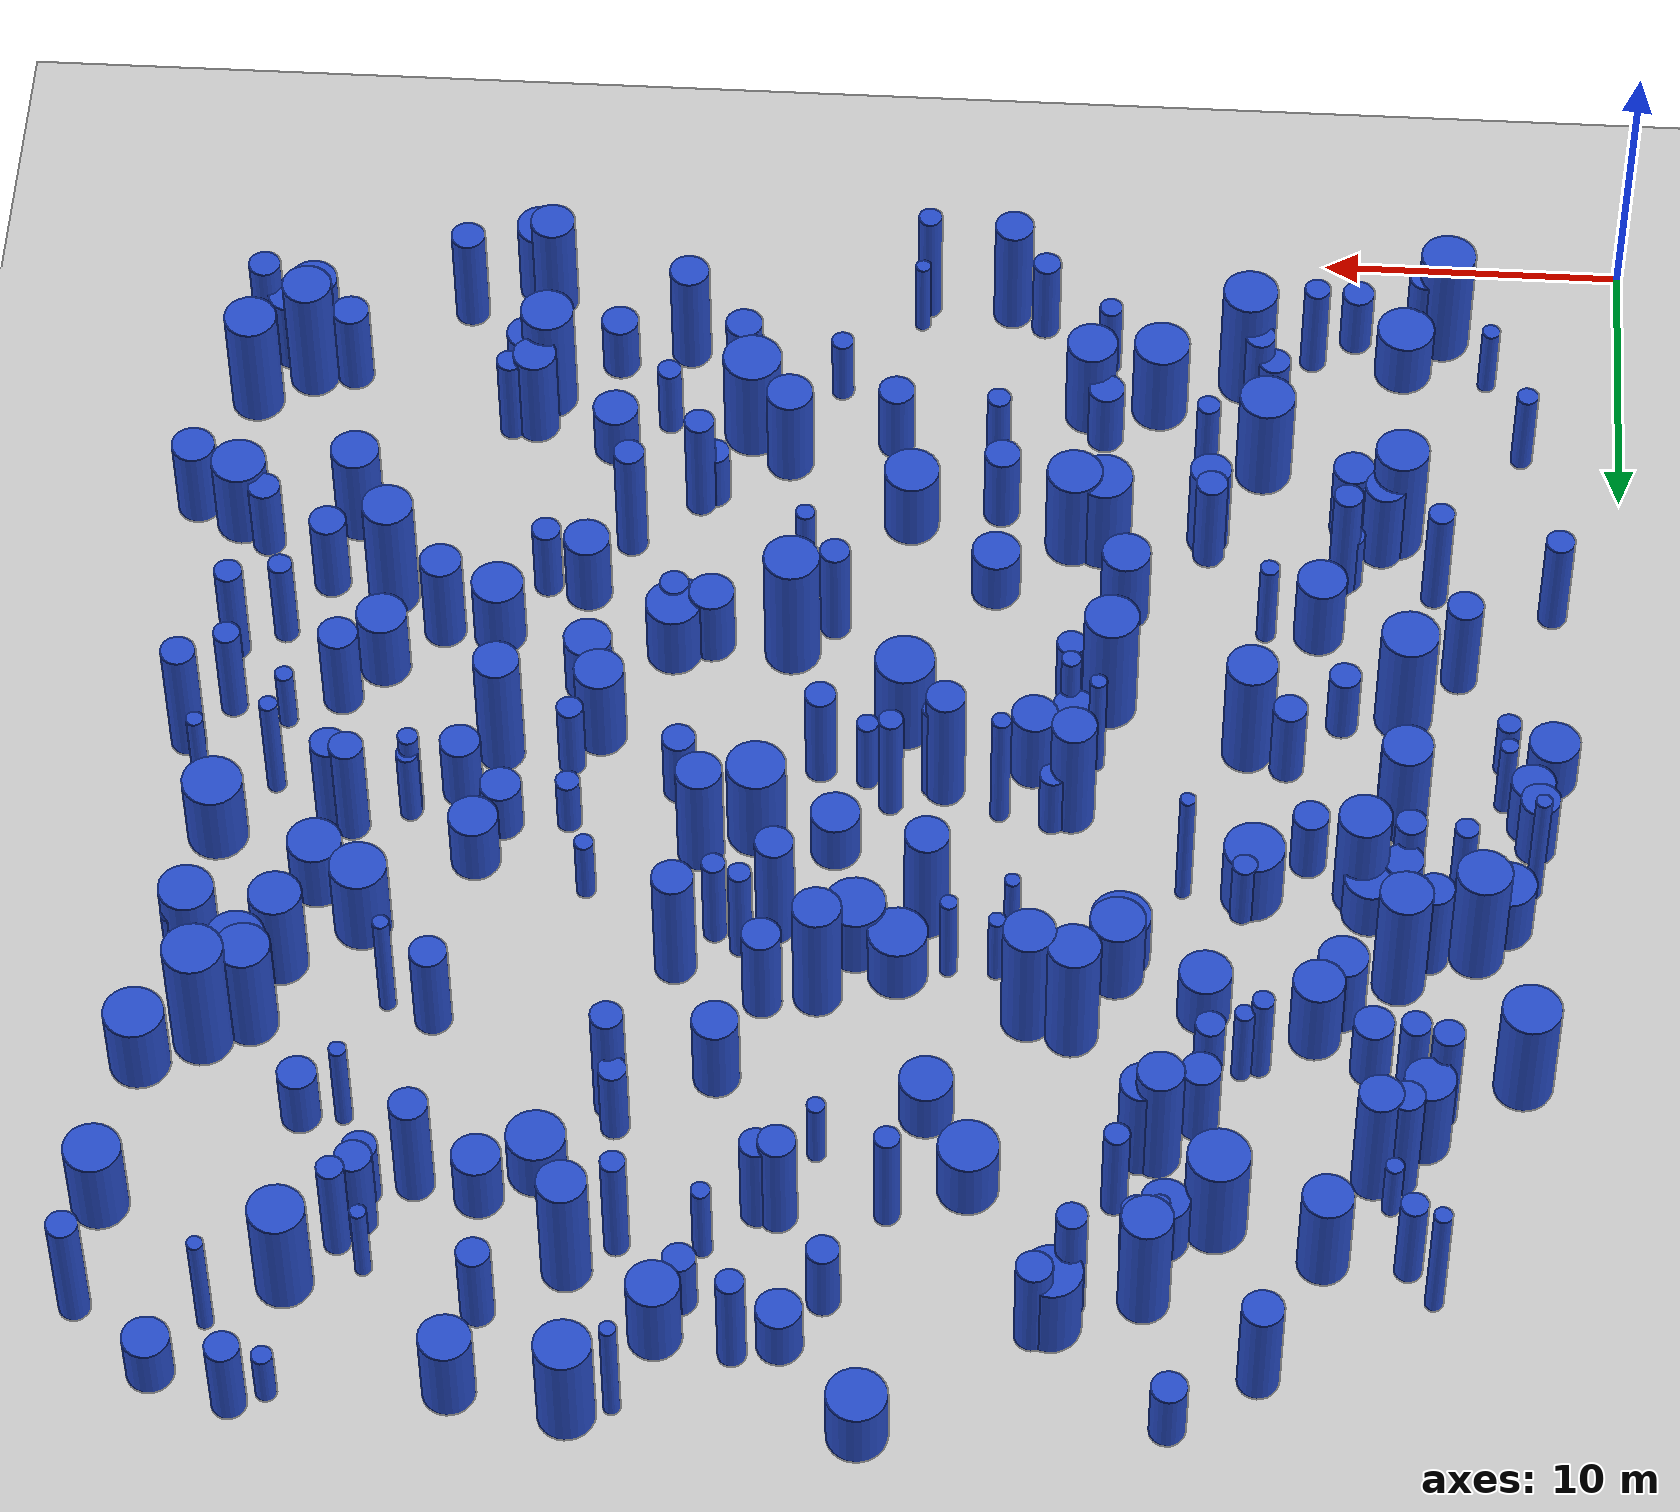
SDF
<sdf version="1.6">
 <world name="default">
  <light name="sun" type="directional">
   <pose>0 0 10 0 -0 0</pose>
   <diffuse>0.8 0.8 0.8 1</diffuse>
   <specular>0.1 0.1 0.1 1</specular>
   <attenuation>
    <range>1000</range>
    <constant>0.9</constant>
    <linear>0.01</linear>
    <quadratic>0.001</quadratic>
   </attenuation>
   <direction>-0.5 0.5 -1</direction>
  </light>
  <model name="ground_plane">
   <static>1</static>
   <link name="link">
    <collision name="collision">
     <geometry><plane><normal>0 0 1</normal><size>100 100</size></plane></geometry>
     <surface><friction><ode><mu>100</mu><mu2>50</mu2></ode></friction></surface>
    </collision>
    <visual name="visual">
     <cast_shadows>0</cast_shadows>
     <geometry><plane><normal>0 0 1</normal><size>100 100</size></plane></geometry>
     <material>
      <script><uri>file://media/materials/scripts/gazebo.material</uri><name>Gazebo/Grey</name></script>
     </material>
    </visual>
   </link>
  </model>
  <gravity>0 0 -9.8</gravity>
  <magnetic_field>6e-06 2.3e-05 -4.2e-05</magnetic_field>
  <atmosphere type="adiabatic"/>
  <physics name="default_physics" default="0" type="ode">
   <max_step_size>0.001</max_step_size>
   <real_time_factor>1</real_time_factor>
   <real_time_update_rate>1000</real_time_update_rate>
  </physics>
  <scene><ambient>0.4 0.4 0.4 1</ambient><background>0.7 0.7 0.7 1</background><shadows>1</shadows></scene>
  <spherical_coordinates>
   <surface_model>EARTH_WGS84</surface_model>
   <latitude_deg>0</latitude_deg>
   <longitude_deg>0</longitude_deg>
   <elevation>0</elevation>
   <heading_deg>0</heading_deg>
  </spherical_coordinates>
  <model name="0">
   <static>0</static>
   <link name="link">
    <inertial>
     <mass>2</mass>
     <inertia><ixx>1.43734</ixx><ixy>0</ixy><ixz>0</ixz><iyy>1.43734</iyy><iyz>0</iyz><izz>0.944565</izz></inertia>
    </inertial>
    <collision name="collision">
     <geometry><cylinder><length>2.40632</length><radius>0.971888</radius></cylinder></geometry>
     <surface><contact><collide_without_contact>1</collide_without_contact></contact></surface>
    </collision>
    <visual name="visual">
     <geometry><cylinder><length>2.40632</length><radius>0.971888</radius></cylinder></geometry>
     <material>
      <script><uri>file://media/materials/scripts/gazebo.material</uri><name>Gazebo/Blue</name></script>
     </material>
    </visual>
    <gravity>0</gravity>
   </link>
   <pose>20.5384 38.7875 1.20316 0 -0 0</pose>
  </model>
  <model name="1">
   <static>0</static>
   <link name="link">
    <inertial>
     <mass>2</mass>
     <inertia><ixx>1.21264</ixx><ixy>0</ixy><ixz>0</ixz><iyy>1.21264</iyy><iyz>0</iyz><izz>0.729702</izz></inertia>
    </inertial>
    <collision name="collision">
     <geometry><cylinder><length>2.25538</length><radius>0.854226</radius></cylinder></geometry>
     <surface><contact><collide_without_contact>1</collide_without_contact></contact></surface>
    </collision>
    <visual name="visual">
     <geometry><cylinder><length>2.25538</length><radius>0.854226</radius></cylinder></geometry>
     <material>
      <script><uri>file://media/materials/scripts/gazebo.material</uri><name>Gazebo/Blue</name></script>
     </material>
    </visual>
    <gravity>0</gravity>
   </link>
   <pose>13.3804 31.6772 1.12769 0 -0 0</pose>
  </model>
  <model name="2">
   <static>0</static>
   <link name="link">
    <inertial>
     <mass>2</mass>
     <inertia><ixx>1.9179</ixx><ixy>0</ixy><ixz>0</ixz><iyy>1.9179</iyy><iyz>0</iyz><izz>0.974837</izz></inertia>
    </inertial>
    <collision name="collision">
     <geometry><cylinder><length>2.92966</length><radius>0.987338</radius></cylinder></geometry>
     <surface><contact><collide_without_contact>1</collide_without_contact></contact></surface>
    </collision>
    <visual name="visual">
     <geometry><cylinder><length>2.92966</length><radius>0.987338</radius></cylinder></geometry>
     <material>
      <script><uri>file://media/materials/scripts/gazebo.material</uri><name>Gazebo/Blue</name></script>
     </material>
    </visual>
    <gravity>0</gravity>
   </link>
   <pose>45.4163 26.3645 1.46483 0 -0 0</pose>
  </model>
  <model name="3">
   <static>0</static>
   <link name="link">
    <inertial>
     <mass>2</mass>
     <inertia><ixx>3.92775</ixx><ixy>0</ixy><ixz>0</ixz><iyy>3.92775</iyy><iyz>0</iyz><izz>0.695081</izz></inertia>
    </inertial>
    <collision name="collision">
     <geometry><cylinder><length>4.63479</length><radius>0.833715</radius></cylinder></geometry>
     <surface><contact><collide_without_contact>1</collide_without_contact></contact></surface>
    </collision>
    <visual name="visual">
     <geometry><cylinder><length>4.63479</length><radius>0.833715</radius></cylinder></geometry>
     <material>
      <script><uri>file://media/materials/scripts/gazebo.material</uri><name>Gazebo/Blue</name></script>
     </material>
    </visual>
    <gravity>0</gravity>
   </link>
   <pose>12.2422 21.1681 2.31739 0 -0 0</pose>
  </model>
  <model name="4">
   <static>0</static>
   <link name="link">
    <inertial>
     <mass>2</mass>
     <inertia>
      <ixx>2.26503</ixx>
      <ixy>0</ixy>
      <ixz>0</ixz>
      <iyy>2.26503</iyy>
      <iyz>0</iyz>
      <izz>0.0810352</izz>
     </inertia>
    </inertial>
    <collision name="collision">
     <geometry><cylinder><length>3.65337</length><radius>0.284667</radius></cylinder></geometry>
     <surface><contact><collide_without_contact>1</collide_without_contact></contact></surface>
    </collision>
    <visual name="visual">
     <geometry><cylinder><length>3.65337</length><radius>0.284667</radius></cylinder></geometry>
     <material>
      <script><uri>file://media/materials/scripts/gazebo.material</uri><name>Gazebo/Blue</name></script>
     </material>
    </visual>
    <gravity>0</gravity>
   </link>
   <pose>21.5602 30.4174 1.82668 0 -0 0</pose>
  </model>
  <model name="5">
   <static>0</static>
   <link name="link">
    <inertial>
     <mass>2</mass>
     <inertia><ixx>2.0117</ixx><ixy>0</ixy><ixz>0</ixz><iyy>2.0117</iyy><iyz>0</iyz><izz>0.692416</izz></inertia>
    </inertial>
    <collision name="collision">
     <geometry><cylinder><length>3.16116</length><radius>0.832116</radius></cylinder></geometry>
     <surface><contact><collide_without_contact>1</collide_without_contact></contact></surface>
    </collision>
    <visual name="visual">
     <geometry><cylinder><length>3.16116</length><radius>0.832116</radius></cylinder></geometry>
     <material>
      <script><uri>file://media/materials/scripts/gazebo.material</uri><name>Gazebo/Blue</name></script>
     </material>
    </visual>
    <gravity>0</gravity>
   </link>
   <pose>9.83556 32.4698 1.58058 0 -0 0</pose>
  </model>
  <model name="6">
   <static>0</static>
   <link name="link">
    <inertial>
     <mass>2</mass>
     <inertia><ixx>1.5744</ixx><ixy>0</ixy><ixz>0</ixz><iyy>1.5744</iyy><iyz>0</iyz><izz>0.233531</izz></inertia>
    </inertial>
    <collision name="collision">
     <geometry><cylinder><length>2.95733</length><radius>0.483251</radius></cylinder></geometry>
     <surface><contact><collide_without_contact>1</collide_without_contact></contact></surface>
    </collision>
    <visual name="visual">
     <geometry><cylinder><length>2.95733</length><radius>0.483251</radius></cylinder></geometry>
     <material>
      <script><uri>file://media/materials/scripts/gazebo.material</uri><name>Gazebo/Blue</name></script>
     </material>
    </visual>
    <gravity>0</gravity>
   </link>
   <pose>6.75771 33.7908 1.47867 0 -0 0</pose>
  </model>
  <model name="7">
   <static>0</static>
   <link name="link">
    <inertial>
     <mass>2</mass>
     <inertia><ixx>4.42007</ixx><ixy>0</ixy><ixz>0</ixz><iyy>4.42007</iyy><iyz>0</iyz><izz>0.725358</izz></inertia>
    </inertial>
    <collision name="collision">
     <geometry><cylinder><length>4.934</length><radius>0.85168</radius></cylinder></geometry>
     <surface><contact><collide_without_contact>1</collide_without_contact></contact></surface>
    </collision>
    <visual name="visual">
     <geometry><cylinder><length>4.934</length><radius>0.85168</radius></cylinder></geometry>
     <material>
      <script><uri>file://media/materials/scripts/gazebo.material</uri><name>Gazebo/Blue</name></script>
     </material>
    </visual>
    <gravity>0</gravity>
   </link>
   <pose>7.21815 30.2077 2.467 0 -0 0</pose>
  </model>
  <model name="8">
   <static>0</static>
   <link name="link">
    <inertial>
     <mass>2</mass>
     <inertia><ixx>3.23009</ixx><ixy>0</ixy><ixz>0</ixz><iyy>3.23009</iyy><iyz>0</iyz><izz>0.313267</izz></inertia>
    </inertial>
    <collision name="collision">
     <geometry><cylinder><length>4.29427</length><radius>0.559703</radius></cylinder></geometry>
     <surface><contact><collide_without_contact>1</collide_without_contact></contact></surface>
    </collision>
    <visual name="visual">
     <geometry><cylinder><length>4.29427</length><radius>0.559703</radius></cylinder></geometry>
     <material>
      <script><uri>file://media/materials/scripts/gazebo.material</uri><name>Gazebo/Blue</name></script>
     </material>
    </visual>
    <gravity>0</gravity>
   </link>
   <pose>41.0947 25.7566 2.14713 0 -0 0</pose>
  </model>
  <model name="9">
   <static>0</static>
   <link name="link">
    <inertial>
     <mass>2</mass>
     <inertia><ixx>1.24437</ixx><ixy>0</ixy><ixz>0</ixz><iyy>1.24437</iyy><iyz>0</iyz><izz>0.137792</izz></inertia>
    </inertial>
    <collision name="collision">
     <geometry><cylinder><length>2.65572</length><radius>0.371203</radius></cylinder></geometry>
     <surface><contact><collide_without_contact>1</collide_without_contact></contact></surface>
    </collision>
    <visual name="visual">
     <geometry><cylinder><length>2.65572</length><radius>0.371203</radius></cylinder></geometry>
     <material>
      <script><uri>file://media/materials/scripts/gazebo.material</uri><name>Gazebo/Blue</name></script>
     </material>
    </visual>
    <gravity>0</gravity>
   </link>
   <pose>26.3091 6.47508 1.32786 0 -0 0</pose>
  </model>
  <model name="10">
   <static>0</static>
   <link name="link">
    <inertial>
     <mass>2</mass>
     <inertia><ixx>1.24688</ixx><ixy>0</ixy><ixz>0</ixz><iyy>1.24688</iyy><iyz>0</iyz><izz>0.518703</izz></inertia>
    </inertial>
    <collision name="collision">
     <geometry><cylinder><length>2.43417</length><radius>0.72021</radius></cylinder></geometry>
     <surface><contact><collide_without_contact>1</collide_without_contact></contact></surface>
    </collision>
    <visual name="visual">
     <geometry><cylinder><length>2.43417</length><radius>0.72021</radius></cylinder></geometry>
     <material>
      <script><uri>file://media/materials/scripts/gazebo.material</uri><name>Gazebo/Blue</name></script>
     </material>
    </visual>
    <gravity>0</gravity>
   </link>
   <pose>3.05727 23.7254 1.21708 0 -0 0</pose>
  </model>
  <model name="11">
   <static>0</static>
   <link name="link">
    <inertial>
     <mass>2</mass>
     <inertia><ixx>2.14367</ixx><ixy>0</ixy><ixz>0</ixz><iyy>2.14367</iyy><iyz>0</iyz><izz>0.840416</izz></inertia>
    </inertial>
    <collision name="collision">
     <geometry><cylinder><length>3.2157</length><radius>0.916742</radius></cylinder></geometry>
     <surface><contact><collide_without_contact>1</collide_without_contact></contact></surface>
    </collision>
    <visual name="visual">
     <geometry><cylinder><length>3.2157</length><radius>0.916742</radius></cylinder></geometry>
     <material>
      <script><uri>file://media/materials/scripts/gazebo.material</uri><name>Gazebo/Blue</name></script>
     </material>
    </visual>
    <gravity>0</gravity>
   </link>
   <pose>45.9924 13.2995 1.60785 0 -0 0</pose>
  </model>
  <model name="12">
   <static>0</static>
   <link name="link">
    <inertial>
     <mass>2</mass>
     <inertia><ixx>4.25183</ixx><ixy>0</ixy><ixz>0</ixz><iyy>4.25183</iyy><iyz>0</iyz><izz>0.805611</izz></inertia>
    </inertial>
    <collision name="collision">
     <geometry><cylinder><length>4.80564</length><radius>0.897558</radius></cylinder></geometry>
     <surface><contact><collide_without_contact>1</collide_without_contact></contact></surface>
    </collision>
    <visual name="visual">
     <geometry><cylinder><length>4.80564</length><radius>0.897558</radius></cylinder></geometry>
     <material>
      <script><uri>file://media/materials/scripts/gazebo.material</uri><name>Gazebo/Blue</name></script>
     </material>
    </visual>
    <gravity>0</gravity>
   </link>
   <pose>16.8242 19.5526 2.40282 0 -0 0</pose>
  </model>
  <model name="13">
   <static>0</static>
   <link name="link">
    <inertial>
     <mass>2</mass>
     <inertia><ixx>2.5994</ixx><ixy>0</ixy><ixz>0</ixz><iyy>2.5994</iyy><iyz>0</iyz><izz>0.0800748</izz></inertia>
    </inertial>
    <collision name="collision">
     <geometry><cylinder><length>3.91869</length><radius>0.282975</radius></cylinder></geometry>
     <surface><contact><collide_without_contact>1</collide_without_contact></contact></surface>
    </collision>
    <visual name="visual">
     <geometry><cylinder><length>3.91869</length><radius>0.282975</radius></cylinder></geometry>
     <material>
      <script><uri>file://media/materials/scripts/gazebo.material</uri><name>Gazebo/Blue</name></script>
     </material>
    </visual>
    <gravity>0</gravity>
   </link>
   <pose>46.0991 24.6597 1.95935 0 -0 0</pose>
  </model>
  <model name="14">
   <static>0</static>
   <link name="link">
    <inertial>
     <mass>2</mass>
     <inertia><ixx>1.64079</ixx><ixy>0</ixy><ixz>0</ixz><iyy>1.64079</iyy><iyz>0</iyz><izz>0.150374</izz></inertia>
    </inertial>
    <collision name="collision">
     <geometry><cylinder><length>3.0649</length><radius>0.38778</radius></cylinder></geometry>
     <surface><contact><collide_without_contact>1</collide_without_contact></contact></surface>
    </collision>
    <visual name="visual">
     <geometry><cylinder><length>3.0649</length><radius>0.38778</radius></cylinder></geometry>
     <material>
      <script><uri>file://media/materials/scripts/gazebo.material</uri><name>Gazebo/Blue</name></script>
     </material>
    </visual>
    <gravity>0</gravity>
   </link>
   <pose>17.3165 4.85681 1.53245 0 -0 0</pose>
  </model>
  <model name="15">
   <static>0</static>
   <link name="link">
    <inertial>
     <mass>2</mass>
     <inertia><ixx>4.38283</ixx><ixy>0</ixy><ixz>0</ixz><iyy>4.38283</iyy><iyz>0</iyz><izz>0.572271</izz></inertia>
    </inertial>
    <collision name="collision">
     <geometry><cylinder><length>4.95784</length><radius>0.756486</radius></cylinder></geometry>
     <surface><contact><collide_without_contact>1</collide_without_contact></contact></surface>
    </collision>
    <visual name="visual">
     <geometry><cylinder><length>4.95784</length><radius>0.756486</radius></cylinder></geometry>
     <material>
      <script><uri>file://media/materials/scripts/gazebo.material</uri><name>Gazebo/Blue</name></script>
     </material>
    </visual>
    <gravity>0</gravity>
   </link>
   <pose>36.5323 22.5346 2.47892 0 -0 0</pose>
  </model>
  <model name="16">
   <static>0</static>
   <link name="link">
    <inertial>
     <mass>2</mass>
     <inertia><ixx>1.32738</ixx><ixy>0</ixy><ixz>0</ixz><iyy>1.32738</iyy><iyz>0</iyz><izz>0.945054</izz></inertia>
    </inertial>
    <collision name="collision">
     <geometry><cylinder><length>2.26476</length><radius>0.972139</radius></cylinder></geometry>
     <surface><contact><collide_without_contact>1</collide_without_contact></contact></surface>
    </collision>
    <visual name="visual">
     <geometry><cylinder><length>2.26476</length><radius>0.972139</radius></cylinder></geometry>
     <material>
      <script><uri>file://media/materials/scripts/gazebo.material</uri><name>Gazebo/Blue</name></script>
     </material>
    </visual>
    <gravity>0</gravity>
   </link>
   <pose>16.1139 29.627 1.13238 0 -0 0</pose>
  </model>
  <model name="17">
   <static>0</static>
   <link name="link">
    <inertial>
     <mass>2</mass>
     <inertia><ixx>1.23789</ixx><ixy>0</ixy><ixz>0</ixz><iyy>1.23789</iyy><iyz>0</iyz><izz>0.598154</izz></inertia>
    </inertial>
    <collision name="collision">
     <geometry><cylinder><length>2.37337</length><radius>0.773404</radius></cylinder></geometry>
     <surface><contact><collide_without_contact>1</collide_without_contact></contact></surface>
    </collision>
    <visual name="visual">
     <geometry><cylinder><length>2.37337</length><radius>0.773404</radius></cylinder></geometry>
     <material>
      <script><uri>file://media/materials/scripts/gazebo.material</uri><name>Gazebo/Blue</name></script>
     </material>
    </visual>
    <gravity>0</gravity>
   </link>
   <pose>14.3822 40.423 1.18668 0 -0 0</pose>
  </model>
  <model name="18">
   <static>0</static>
   <link name="link">
    <inertial>
     <mass>2</mass>
     <inertia><ixx>1.59009</ixx><ixy>0</ixy><ixz>0</ixz><iyy>1.59009</iyy><iyz>0</iyz><izz>0.231054</izz></inertia>
    </inertial>
    <collision name="collision">
     <geometry><cylinder><length>2.97446</length><radius>0.48068</radius></cylinder></geometry>
     <surface><contact><collide_without_contact>1</collide_without_contact></contact></surface>
    </collision>
    <visual name="visual">
     <geometry><cylinder><length>2.97446</length><radius>0.48068</radius></cylinder></geometry>
     <material>
      <script><uri>file://media/materials/scripts/gazebo.material</uri><name>Gazebo/Blue</name></script>
     </material>
    </visual>
    <gravity>0</gravity>
   </link>
   <pose>35.5825 15.4394 1.48723 0 -0 0</pose>
  </model>
  <model name="19">
   <static>0</static>
   <link name="link">
    <inertial>
     <mass>2</mass>
     <inertia><ixx>1.33118</ixx><ixy>0</ixy><ixz>0</ixz><iyy>1.33118</iyy><iyz>0</iyz><izz>0.426868</izz></inertia>
    </inertial>
    <collision name="collision">
     <geometry><cylinder><length>2.58969</length><radius>0.653352</radius></cylinder></geometry>
     <surface><contact><collide_without_contact>1</collide_without_contact></contact></surface>
    </collision>
    <visual name="visual">
     <geometry><cylinder><length>2.58969</length><radius>0.653352</radius></cylinder></geometry>
     <material>
      <script><uri>file://media/materials/scripts/gazebo.material</uri><name>Gazebo/Blue</name></script>
     </material>
    </visual>
    <gravity>0</gravity>
   </link>
   <pose>8.06166 33.5749 1.29484 0 -0 0</pose>
  </model>
  <model name="20">
   <static>0</static>
   <link name="link">
    <inertial>
     <mass>2</mass>
     <inertia>
      <ixx>1.75585</ixx>
      <ixy>0</ixy>
      <ixz>0</ixz>
      <iyy>1.75585</iyy>
      <iyz>0</iyz>
      <izz>0.0905961</izz>
     </inertia>
    </inertial>
    <collision name="collision">
     <geometry><cylinder><length>3.20364</length><radius>0.300992</radius></cylinder></geometry>
     <surface><contact><collide_without_contact>1</collide_without_contact></contact></surface>
    </collision>
    <visual name="visual">
     <geometry><cylinder><length>3.20364</length><radius>0.300992</radius></cylinder></geometry>
     <material>
      <script><uri>file://media/materials/scripts/gazebo.material</uri><name>Gazebo/Blue</name></script>
     </material>
    </visual>
    <gravity>0</gravity>
   </link>
   <pose>3.87578 22.8858 1.60182 0 -0 0</pose>
  </model>
  <model name="21">
   <static>0</static>
   <link name="link">
    <inertial>
     <mass>2</mass>
     <inertia><ixx>1.37016</ixx><ixy>0</ixy><ixz>0</ixz><iyy>1.37016</iyy><iyz>0</iyz><izz>0.921566</izz></inertia>
    </inertial>
    <collision name="collision">
     <geometry><cylinder><length>2.33587</length><radius>0.959982</radius></cylinder></geometry>
     <surface><contact><collide_without_contact>1</collide_without_contact></contact></surface>
    </collision>
    <visual name="visual">
     <geometry><cylinder><length>2.33587</length><radius>0.959982</radius></cylinder></geometry>
     <material>
      <script><uri>file://media/materials/scripts/gazebo.material</uri><name>Gazebo/Blue</name></script>
     </material>
    </visual>
    <gravity>0</gravity>
   </link>
   <pose>23.4785 47.9749 1.16793 0 -0 0</pose>
  </model>
  <model name="22">
   <static>0</static>
   <link name="link">
    <inertial>
     <mass>2</mass>
     <inertia>
      <ixx>0.996712</ixx>
      <ixy>0</ixy>
      <ixz>0</ixz>
      <iyy>0.996712</iyy>
      <iyz>0</iyz>
      <izz>0.087716</izz>
     </inertia>
    </inertial>
    <collision name="collision">
     <geometry><cylinder><length>2.39105</length><radius>0.296169</radius></cylinder></geometry>
     <surface><contact><collide_without_contact>1</collide_without_contact></contact></surface>
    </collision>
    <visual name="visual">
     <geometry><cylinder><length>2.39105</length><radius>0.296169</radius></cylinder></geometry>
     <material>
      <script><uri>file://media/materials/scripts/gazebo.material</uri><name>Gazebo/Blue</name></script>
     </material>
    </visual>
    <gravity>0</gravity>
   </link>
   <pose>7.34966 38.7949 1.19553 0 -0 0</pose>
  </model>
  <model name="23">
   <static>0</static>
   <link name="link">
    <inertial>
     <mass>2</mass>
     <inertia><ixx>3.04938</ixx><ixy>0</ixy><ixz>0</ixz><iyy>3.04938</iyy><iyz>0</iyz><izz>0.188982</izz></inertia>
    </inertial>
    <collision name="collision">
     <geometry><cylinder><length>4.21062</length><radius>0.434721</radius></cylinder></geometry>
     <surface><contact><collide_without_contact>1</collide_without_contact></contact></surface>
    </collision>
    <visual name="visual">
     <geometry><cylinder><length>4.21062</length><radius>0.434721</radius></cylinder></geometry>
     <material>
      <script><uri>file://media/materials/scripts/gazebo.material</uri><name>Gazebo/Blue</name></script>
     </material>
    </visual>
    <gravity>0</gravity>
   </link>
   <pose>39.9557 41.882 2.10531 0 -0 0</pose>
  </model>
  <model name="24">
   <static>0</static>
   <link name="link">
    <inertial>
     <mass>2</mass>
     <inertia><ixx>1.33099</ixx><ixy>0</ixy><ixz>0</ixz><iyy>1.33099</iyy><iyz>0</iyz><izz>0.36083</izz></inertia>
    </inertial>
    <collision name="collision">
     <geometry><cylinder><length>2.62744</length><radius>0.600691</radius></cylinder></geometry>
     <surface><contact><collide_without_contact>1</collide_without_contact></contact></surface>
    </collision>
    <visual name="visual">
     <geometry><cylinder><length>2.62744</length><radius>0.600691</radius></cylinder></geometry>
     <material>
      <script><uri>file://media/materials/scripts/gazebo.material</uri><name>Gazebo/Blue</name></script>
     </material>
    </visual>
    <gravity>0</gravity>
   </link>
   <pose>17.3457 8.06964 1.31372 0 -0 0</pose>
  </model>
  <model name="25">
   <static>0</static>
   <link name="link">
    <inertial>
     <mass>2</mass>
     <inertia><ixx>1.51438</ixx><ixy>0</ixy><ixz>0</ixz><iyy>1.51438</iyy><iyz>0</iyz><izz>0.951451</izz></inertia>
    </inertial>
    <collision name="collision">
     <geometry><cylinder><length>2.49638</length><radius>0.975423</radius></cylinder></geometry>
     <surface><contact><collide_without_contact>1</collide_without_contact></contact></surface>
    </collision>
    <visual name="visual">
     <geometry><cylinder><length>2.49638</length><radius>0.975423</radius></cylinder></geometry>
     <material>
      <script><uri>file://media/materials/scripts/gazebo.material</uri><name>Gazebo/Blue</name></script>
     </material>
    </visual>
    <gravity>0</gravity>
   </link>
   <pose>24.5529 29.7279 1.24819 0 -0 0</pose>
  </model>
  <model name="26">
   <static>0</static>
   <link name="link">
    <inertial>
     <mass>2</mass>
     <inertia><ixx>1.75387</ixx><ixy>0</ixy><ixz>0</ixz><iyy>1.75387</iyy><iyz>0</iyz><izz>0.848622</izz></inertia>
    </inertial>
    <collision name="collision">
     <geometry><cylinder><length>2.82442</length><radius>0.921207</radius></cylinder></geometry>
     <surface><contact><collide_without_contact>1</collide_without_contact></contact></surface>
    </collision>
    <visual name="visual">
     <geometry><cylinder><length>2.82442</length><radius>0.921207</radius></cylinder></geometry>
     <material>
      <script><uri>file://media/materials/scripts/gazebo.material</uri><name>Gazebo/Blue</name></script>
     </material>
    </visual>
    <gravity>0</gravity>
   </link>
   <pose>23.683 12.1353 1.41221 0 -0 0</pose>
  </model>
  <model name="27">
   <static>0</static>
   <link name="link">
    <inertial>
     <mass>2</mass>
     <inertia><ixx>2.24556</ixx><ixy>0</ixy><ixz>0</ixz><iyy>2.24556</iyy><iyz>0</iyz><izz>0.865007</izz></inertia>
    </inertial>
    <collision name="collision">
     <geometry><cylinder><length>3.29823</length><radius>0.930057</radius></cylinder></geometry>
     <surface><contact><collide_without_contact>1</collide_without_contact></contact></surface>
    </collision>
    <visual name="visual">
     <geometry><cylinder><length>3.29823</length><radius>0.930057</radius></cylinder></geometry>
     <material>
      <script><uri>file://media/materials/scripts/gazebo.material</uri><name>Gazebo/Blue</name></script>
     </material>
    </visual>
    <gravity>0</gravity>
   </link>
   <pose>40.362 29.7446 1.64912 0 -0 0</pose>
  </model>
  <model name="28">
   <static>0</static>
   <link name="link">
    <inertial>
     <mass>2</mass>
     <inertia>
      <ixx>4.08418</ixx>
      <ixy>0</ixy>
      <ixz>0</ixz>
      <iyy>4.08418</iyy>
      <iyz>0</iyz>
      <izz>0.0857833</izz>
     </inertia>
    </inertial>
    <collision name="collision">
     <geometry><cylinder><length>4.9242</length><radius>0.292888</radius></cylinder></geometry>
     <surface><contact><collide_without_contact>1</collide_without_contact></contact></surface>
    </collision>
    <visual name="visual">
     <geometry><cylinder><length>4.9242</length><radius>0.292888</radius></cylinder></geometry>
     <material>
      <script><uri>file://media/materials/scripts/gazebo.material</uri><name>Gazebo/Blue</name></script>
     </material>
    </visual>
    <gravity>0</gravity>
   </link>
   <pose>5.98766 42.2378 2.4621 0 -0 0</pose>
  </model>
  <model name="29">
   <static>0</static>
   <link name="link">
    <inertial>
     <mass>2</mass>
     <inertia><ixx>1.08444</ixx><ixy>0</ixy><ixz>0</ixz><iyy>1.08444</iyy><iyz>0</iyz><izz>0.820187</izz></inertia>
    </inertial>
    <collision name="collision">
     <geometry><cylinder><length>2.01148</length><radius>0.905642</radius></cylinder></geometry>
     <surface><contact><collide_without_contact>1</collide_without_contact></contact></surface>
    </collision>
    <visual name="visual">
     <geometry><cylinder><length>2.01148</length><radius>0.905642</radius></cylinder></geometry>
     <material>
      <script><uri>file://media/materials/scripts/gazebo.material</uri><name>Gazebo/Blue</name></script>
     </material>
    </visual>
    <gravity>0</gravity>
   </link>
   <pose>8.17215 27.4661 1.00574 0 -0 0</pose>
  </model>
  <model name="30">
   <static>0</static>
   <link name="link">
    <inertial>
     <mass>2</mass>
     <inertia><ixx>3.98428</ixx><ixy>0</ixy><ixz>0</ixz><iyy>3.98428</iyy><iyz>0</iyz><izz>0.265355</izz></inertia>
    </inertial>
    <collision name="collision">
     <geometry><cylinder><length>4.80724</length><radius>0.515126</radius></cylinder></geometry>
     <surface><contact><collide_without_contact>1</collide_without_contact></contact></surface>
    </collision>
    <visual name="visual">
     <geometry><cylinder><length>4.80724</length><radius>0.515126</radius></cylinder></geometry>
     <material>
      <script><uri>file://media/materials/scripts/gazebo.material</uri><name>Gazebo/Blue</name></script>
     </material>
    </visual>
    <gravity>0</gravity>
   </link>
   <pose>32.9406 13.5218 2.40362 0 -0 0</pose>
  </model>
  <model name="31">
   <static>0</static>
   <link name="link">
    <inertial>
     <mass>2</mass>
     <inertia><ixx>2.46305</ixx><ixy>0</ixy><ixz>0</ixz><iyy>2.46305</iyy><iyz>0</iyz><izz>0.114316</izz></inertia>
    </inertial>
    <collision name="collision">
     <geometry><cylinder><length>3.79939</length><radius>0.338106</radius></cylinder></geometry>
     <surface><contact><collide_without_contact>1</collide_without_contact></contact></surface>
    </collision>
    <visual name="visual">
     <geometry><cylinder><length>3.79939</length><radius>0.338106</radius></cylinder></geometry>
     <material>
      <script><uri>file://media/materials/scripts/gazebo.material</uri><name>Gazebo/Blue</name></script>
     </material>
    </visual>
    <gravity>0</gravity>
   </link>
   <pose>39.2114 24.8963 1.89969 0 -0 0</pose>
  </model>
  <model name="32">
   <static>0</static>
   <link name="link">
    <inertial>
     <mass>2</mass>
     <inertia><ixx>2.61108</ixx><ixy>0</ixy><ixz>0</ixz><iyy>2.61108</iyy><iyz>0</iyz><izz>0.521676</izz></inertia>
    </inertial>
    <collision name="collision">
     <geometry><cylinder><length>3.75519</length><radius>0.722271</radius></cylinder></geometry>
     <surface><contact><collide_without_contact>1</collide_without_contact></contact></surface>
    </collision>
    <visual name="visual">
     <geometry><cylinder><length>3.75519</length><radius>0.722271</radius></cylinder></geometry>
     <material>
      <script><uri>file://media/materials/scripts/gazebo.material</uri><name>Gazebo/Blue</name></script>
     </material>
    </visual>
    <gravity>0</gravity>
   </link>
   <pose>36.5241 8.5571 1.87759 0 -0 0</pose>
  </model>
  <model name="33">
   <static>0</static>
   <link name="link">
    <inertial>
     <mass>2</mass>
     <inertia><ixx>2.72224</ixx><ixy>0</ixy><ixz>0</ixz><iyy>2.72224</iyy><iyz>0</iyz><izz>0.654472</izz></inertia>
    </inertial>
    <collision name="collision">
     <geometry><cylinder><length>3.79078</length><radius>0.808995</radius></cylinder></geometry>
     <surface><contact><collide_without_contact>1</collide_without_contact></contact></surface>
    </collision>
    <visual name="visual">
     <geometry><cylinder><length>3.79078</length><radius>0.808995</radius></cylinder></geometry>
     <material>
      <script><uri>file://media/materials/scripts/gazebo.material</uri><name>Gazebo/Blue</name></script>
     </material>
    </visual>
    <gravity>0</gravity>
   </link>
   <pose>42.0996 13.0769 1.89539 0 -0 0</pose>
  </model>
  <model name="34">
   <static>0</static>
   <link name="link">
    <inertial>
     <mass>2</mass>
     <inertia><ixx>2.73964</ixx><ixy>0</ixy><ixz>0</ixz><iyy>2.73964</iyy><iyz>0</iyz><izz>0.355039</izz></inertia>
    </inertial>
    <collision name="collision">
     <geometry><cylinder><length>3.92081</length><radius>0.595852</radius></cylinder></geometry>
     <surface><contact><collide_without_contact>1</collide_without_contact></contact></surface>
    </collision>
    <visual name="visual">
     <geometry><cylinder><length>3.92081</length><radius>0.595852</radius></cylinder></geometry>
     <material>
      <script><uri>file://media/materials/scripts/gazebo.material</uri><name>Gazebo/Blue</name></script>
     </material>
    </visual>
    <gravity>0</gravity>
   </link>
   <pose>5.35862 17.7826 1.9604 0 -0 0</pose>
  </model>
  <model name="35">
   <static>0</static>
   <link name="link">
    <inertial>
     <mass>2</mass>
     <inertia><ixx>2.06592</ixx><ixy>0</ixy><ixz>0</ixz><iyy>2.06592</iyy><iyz>0</iyz><izz>0.920991</izz></inertia>
    </inertial>
    <collision name="collision">
     <geometry><cylinder><length>3.10364</length><radius>0.959683</radius></cylinder></geometry>
     <surface><contact><collide_without_contact>1</collide_without_contact></contact></surface>
    </collision>
    <visual name="visual">
     <geometry><cylinder><length>3.10364</length><radius>0.959683</radius></cylinder></geometry>
     <material>
      <script><uri>file://media/materials/scripts/gazebo.material</uri><name>Gazebo/Blue</name></script>
     </material>
    </visual>
    <gravity>0</gravity>
   </link>
   <pose>17.7601 43.7207 1.55182 0 -0 0</pose>
  </model>
  <model name="36">
   <static>0</static>
   <link name="link">
    <inertial>
     <mass>2</mass>
     <inertia><ixx>1.02322</ixx><ixy>0</ixy><ixz>0</ixz><iyy>1.02322</iyy><iyz>0</iyz><izz>0.699364</izz></inertia>
    </inertial>
    <collision name="collision">
     <geometry><cylinder><length>2.01028</length><radius>0.83628</radius></cylinder></geometry>
     <surface><contact><collide_without_contact>1</collide_without_contact></contact></surface>
    </collision>
    <visual name="visual">
     <geometry><cylinder><length>2.01028</length><radius>0.83628</radius></cylinder></geometry>
     <material>
      <script><uri>file://media/materials/scripts/gazebo.material</uri><name>Gazebo/Blue</name></script>
     </material>
    </visual>
    <gravity>0</gravity>
   </link>
   <pose>2.3337 21.7478 1.00514 0 -0 0</pose>
  </model>
  <model name="37">
   <static>0</static>
   <link name="link">
    <inertial>
     <mass>2</mass>
     <inertia><ixx>3.11102</ixx><ixy>0</ixy><ixz>0</ixz><iyy>3.11102</iyy><iyz>0</iyz><izz>0.974531</izz></inertia>
    </inertial>
    <collision name="collision">
     <geometry><cylinder><length>3.96769</length><radius>0.987183</radius></cylinder></geometry>
     <surface><contact><collide_without_contact>1</collide_without_contact></contact></surface>
    </collision>
    <visual name="visual">
     <geometry><cylinder><length>3.96769</length><radius>0.987183</radius></cylinder></geometry>
     <material>
      <script><uri>file://media/materials/scripts/gazebo.material</uri><name>Gazebo/Blue</name></script>
     </material>
    </visual>
    <gravity>0</gravity>
   </link>
   <pose>29.2156 8.50585 1.98384 0 -0 0</pose>
  </model>
  <model name="38">
   <static>0</static>
   <link name="link">
    <inertial>
     <mass>2</mass>
     <inertia><ixx>1.65718</ixx><ixy>0</ixy><ixz>0</ixz><iyy>1.65718</iyy><iyz>0</iyz><izz>0.295859</izz></inertia>
    </inertial>
    <collision name="collision">
     <geometry><cylinder><length>3.00924</length><radius>0.543929</radius></cylinder></geometry>
     <surface><contact><collide_without_contact>1</collide_without_contact></contact></surface>
    </collision>
    <visual name="visual">
     <geometry><cylinder><length>3.00924</length><radius>0.543929</radius></cylinder></geometry>
     <material>
      <script><uri>file://media/materials/scripts/gazebo.material</uri><name>Gazebo/Blue</name></script>
     </material>
    </visual>
    <gravity>0</gravity>
   </link>
   <pose>45.0656 14.1562 1.50462 0 -0 0</pose>
  </model>
  <model name="39">
   <static>0</static>
   <link name="link">
    <inertial>
     <mass>2</mass>
     <inertia><ixx>2.41207</ixx><ixy>0</ixy><ixz>0</ixz><iyy>2.41207</iyy><iyz>0</iyz><izz>0.674875</izz></inertia>
    </inertial>
    <collision name="collision">
     <geometry><cylinder><length>3.52814</length><radius>0.821508</radius></cylinder></geometry>
     <surface><contact><collide_without_contact>1</collide_without_contact></contact></surface>
    </collision>
    <visual name="visual">
     <geometry><cylinder><length>3.52814</length><radius>0.821508</radius></cylinder></geometry>
     <material>
      <script><uri>file://media/materials/scripts/gazebo.material</uri><name>Gazebo/Blue</name></script>
     </material>
    </visual>
    <gravity>0</gravity>
   </link>
   <pose>6.34437 36.277 1.76407 0 -0 0</pose>
  </model>
  <model name="40">
   <static>0</static>
   <link name="link">
    <inertial>
     <mass>2</mass>
     <inertia><ixx>2.09955</ixx><ixy>0</ixy><ixz>0</ixz><iyy>2.09955</iyy><iyz>0</iyz><izz>0.83864</izz></inertia>
    </inertial>
    <collision name="collision">
     <geometry><cylinder><length>3.17512</length><radius>0.915773</radius></cylinder></geometry>
     <surface><contact><collide_without_contact>1</collide_without_contact></contact></surface>
    </collision>
    <visual name="visual">
     <geometry><cylinder><length>3.17512</length><radius>0.915773</radius></cylinder></geometry>
     <material>
      <script><uri>file://media/materials/scripts/gazebo.material</uri><name>Gazebo/Blue</name></script>
     </material>
    </visual>
    <gravity>0</gravity>
   </link>
   <pose>47.4771 40.8684 1.58756 0 -0 0</pose>
  </model>
  <model name="41">
   <static>0</static>
   <link name="link">
    <inertial>
     <mass>2</mass>
     <inertia>
      <ixx>2.58319</ixx>
      <ixy>0</ixy>
      <ixz>0</ixz>
      <iyy>2.58319</iyy>
      <iyz>0</iyz>
      <izz>0.0988008</izz>
     </inertia>
    </inertial>
    <collision name="collision">
     <geometry><cylinder><length>3.89907</length><radius>0.314326</radius></cylinder></geometry>
     <surface><contact><collide_without_contact>1</collide_without_contact></contact></surface>
    </collision>
    <visual name="visual">
     <geometry><cylinder><length>3.89907</length><radius>0.314326</radius></cylinder></geometry>
     <material>
      <script><uri>file://media/materials/scripts/gazebo.material</uri><name>Gazebo/Blue</name></script>
     </material>
    </visual>
    <gravity>0</gravity>
   </link>
   <pose>14.5714 41.5767 1.94954 0 -0 0</pose>
  </model>
  <model name="42">
   <static>0</static>
   <link name="link">
    <inertial>
     <mass>2</mass>
     <inertia><ixx>2.29017</ixx><ixy>0</ixy><ixz>0</ixz><iyy>2.29017</iyy><iyz>0</iyz><izz>0.162084</izz></inertia>
    </inertial>
    <collision name="collision">
     <geometry><cylinder><length>3.64071</length><radius>0.402597</radius></cylinder></geometry>
     <surface><contact><collide_without_contact>1</collide_without_contact></contact></surface>
    </collision>
    <visual name="visual">
     <geometry><cylinder><length>3.64071</length><radius>0.402597</radius></cylinder></geometry>
     <material>
      <script><uri>file://media/materials/scripts/gazebo.material</uri><name>Gazebo/Blue</name></script>
     </material>
    </visual>
    <gravity>0</gravity>
   </link>
   <pose>44.08 17.9301 1.82036 0 -0 0</pose>
  </model>
  <model name="43">
   <static>0</static>
   <link name="link">
    <inertial>
     <mass>2</mass>
     <inertia><ixx>1.09648</ixx><ixy>0</ixy><ixz>0</ixz><iyy>1.09648</iyy><iyz>0</iyz><izz>0.193563</izz></inertia>
    </inertial>
    <collision name="collision">
     <geometry><cylinder><length>2.44912</length><radius>0.439957</radius></cylinder></geometry>
     <surface><contact><collide_without_contact>1</collide_without_contact></contact></surface>
    </collision>
    <visual name="visual">
     <geometry><cylinder><length>2.44912</length><radius>0.439957</radius></cylinder></geometry>
     <material>
      <script><uri>file://media/materials/scripts/gazebo.material</uri><name>Gazebo/Blue</name></script>
     </material>
    </visual>
    <gravity>0</gravity>
   </link>
   <pose>9.04417 13.8401 1.22456 0 -0 0</pose>
  </model>
  <model name="44">
   <static>0</static>
   <link name="link">
    <inertial>
     <mass>2</mass>
     <inertia><ixx>1.0311</ixx><ixy>0</ixy><ixz>0</ixz><iyy>1.0311</iyy><iyz>0</iyz><izz>0.585255</izz></inertia>
    </inertial>
    <collision name="collision">
     <geometry><cylinder><length>2.10495</length><radius>0.765019</radius></cylinder></geometry>
     <surface><contact><collide_without_contact>1</collide_without_contact></contact></surface>
    </collision>
    <visual name="visual">
     <geometry><cylinder><length>2.10495</length><radius>0.765019</radius></cylinder></geometry>
     <material>
      <script><uri>file://media/materials/scripts/gazebo.material</uri><name>Gazebo/Blue</name></script>
     </material>
    </visual>
    <gravity>0</gravity>
   </link>
   <pose>33.7804 9.37787 1.05247 0 -0 0</pose>
  </model>
  <model name="45">
   <static>0</static>
   <link name="link">
    <inertial>
     <mass>2</mass>
     <inertia><ixx>2.79189</ixx><ixy>0</ixy><ixz>0</ixz><iyy>2.79189</iyy><iyz>0</iyz><izz>0.226924</izz></inertia>
    </inertial>
    <collision name="collision">
     <geometry><cylinder><length>4.00881</length><radius>0.476365</radius></cylinder></geometry>
     <surface><contact><collide_without_contact>1</collide_without_contact></contact></surface>
    </collision>
    <visual name="visual">
     <geometry><cylinder><length>4.00881</length><radius>0.476365</radius></cylinder></geometry>
     <material>
      <script><uri>file://media/materials/scripts/gazebo.material</uri><name>Gazebo/Blue</name></script>
     </material>
    </visual>
    <gravity>0</gravity>
   </link>
   <pose>2.27674 14.996 2.00441 0 -0 0</pose>
  </model>
  <model name="46">
   <static>0</static>
   <link name="link">
    <inertial>
     <mass>2</mass>
     <inertia><ixx>2.99386</ixx><ixy>0</ixy><ixz>0</ixz><iyy>2.99386</iyy><iyz>0</iyz><izz>0.435719</izz></inertia>
    </inertial>
    <collision name="collision">
     <geometry><cylinder><length>4.08118</length><radius>0.66009</radius></cylinder></geometry>
     <surface><contact><collide_without_contact>1</collide_without_contact></contact></surface>
    </collision>
    <visual name="visual">
     <geometry><cylinder><length>4.08118</length><radius>0.66009</radius></cylinder></geometry>
     <material>
      <script><uri>file://media/materials/scripts/gazebo.material</uri><name>Gazebo/Blue</name></script>
     </material>
    </visual>
    <gravity>0</gravity>
   </link>
   <pose>11.3429 45.3423 2.04059 0 -0 0</pose>
  </model>
  <model name="47">
   <static>0</static>
   <link name="link">
    <inertial>
     <mass>2</mass>
     <inertia><ixx>1.72032</ixx><ixy>0</ixy><ixz>0</ixz><iyy>1.72032</iyy><iyz>0</iyz><izz>0.58604</izz></inertia>
    </inertial>
    <collision name="collision">
     <geometry><cylinder><length>2.92639</length><radius>0.765532</radius></cylinder></geometry>
     <surface><contact><collide_without_contact>1</collide_without_contact></contact></surface>
    </collision>
    <visual name="visual">
     <geometry><cylinder><length>2.92639</length><radius>0.765532</radius></cylinder></geometry>
     <material>
      <script><uri>file://media/materials/scripts/gazebo.material</uri><name>Gazebo/Blue</name></script>
     </material>
    </visual>
    <gravity>0</gravity>
   </link>
   <pose>34.2231 15.6872 1.4632 0 -0 0</pose>
  </model>
  <model name="48">
   <static>0</static>
   <link name="link">
    <inertial>
     <mass>2</mass>
     <inertia><ixx>2.37656</ixx><ixy>0</ixy><ixz>0</ixz><iyy>2.37656</iyy><iyz>0</iyz><izz>0.127367</izz></inertia>
    </inertial>
    <collision name="collision">
     <geometry><cylinder><length>3.72522</length><radius>0.356886</radius></cylinder></geometry>
     <surface><contact><collide_without_contact>1</collide_without_contact></contact></surface>
    </collision>
    <visual name="visual">
     <geometry><cylinder><length>3.72522</length><radius>0.356886</radius></cylinder></geometry>
     <material>
      <script><uri>file://media/materials/scripts/gazebo.material</uri><name>Gazebo/Blue</name></script>
     </material>
    </visual>
    <gravity>0</gravity>
   </link>
   <pose>11.5725 33.7002 1.86261 0 -0 0</pose>
  </model>
  <model name="49">
   <static>0</static>
   <link name="link">
    <inertial>
     <mass>2</mass>
     <inertia><ixx>1.4206</ixx><ixy>0</ixy><ixz>0</ixz><iyy>1.4206</iyy><iyz>0</iyz><izz>0.438407</izz></inertia>
    </inertial>
    <collision name="collision">
     <geometry><cylinder><length>2.68485</length><radius>0.662123</radius></cylinder></geometry>
     <surface><contact><collide_without_contact>1</collide_without_contact></contact></surface>
    </collision>
    <visual name="visual">
     <geometry><cylinder><length>2.68485</length><radius>0.662123</radius></cylinder></geometry>
     <material>
      <script><uri>file://media/materials/scripts/gazebo.material</uri><name>Gazebo/Blue</name></script>
     </material>
    </visual>
    <gravity>0</gravity>
   </link>
   <pose>37.6585 24.1439 1.34242 0 -0 0</pose>
  </model>
  <model name="50">
   <static>0</static>
   <link name="link">
    <inertial>
     <mass>2</mass>
     <inertia><ixx>3.40213</ixx><ixy>0</ixy><ixz>0</ixz><iyy>3.40213</iyy><iyz>0</iyz><izz>0.758243</izz></inertia>
    </inertial>
    <collision name="collision">
     <geometry><cylinder><length>4.25888</length><radius>0.870771</radius></cylinder></geometry>
     <surface><contact><collide_without_contact>1</collide_without_contact></contact></surface>
    </collision>
    <visual name="visual">
     <geometry><cylinder><length>4.25888</length><radius>0.870771</radius></cylinder></geometry>
     <material>
      <script><uri>file://media/materials/scripts/gazebo.material</uri><name>Gazebo/Blue</name></script>
     </material>
    </visual>
    <gravity>0</gravity>
   </link>
   <pose>43.5227 33.7385 2.12944 0 -0 0</pose>
  </model>
  <model name="51">
   <static>0</static>
   <link name="link">
    <inertial>
     <mass>2</mass>
     <inertia><ixx>1.29974</ixx><ixy>0</ixy><ixz>0</ixz><iyy>1.29974</iyy><iyz>0</iyz><izz>0.9226</izz></inertia>
    </inertial>
    <collision name="collision">
     <geometry><cylinder><length>2.24292</length><radius>0.960521</radius></cylinder></geometry>
     <surface><contact><collide_without_contact>1</collide_without_contact></contact></surface>
    </collision>
    <visual name="visual">
     <geometry><cylinder><length>2.24292</length><radius>0.960521</radius></cylinder></geometry>
     <material>
      <script><uri>file://media/materials/scripts/gazebo.material</uri><name>Gazebo/Blue</name></script>
     </material>
    </visual>
    <gravity>0</gravity>
   </link>
   <pose>7.33392 4.56687 1.12146 0 -0 0</pose>
  </model>
  <model name="52">
   <static>0</static>
   <link name="link">
    <inertial>
     <mass>2</mass>
     <inertia><ixx>2.62274</ixx><ixy>0</ixy><ixz>0</ixz><iyy>2.62274</iyy><iyz>0</iyz><izz>0.169861</izz></inertia>
    </inertial>
    <collision name="collision">
     <geometry><cylinder><length>3.90216</length><radius>0.412142</radius></cylinder></geometry>
     <surface><contact><collide_without_contact>1</collide_without_contact></contact></surface>
    </collision>
    <visual name="visual">
     <geometry><cylinder><length>3.90216</length><radius>0.412142</radius></cylinder></geometry>
     <material>
      <script><uri>file://media/materials/scripts/gazebo.material</uri><name>Gazebo/Blue</name></script>
     </material>
    </visual>
    <gravity>0</gravity>
   </link>
   <pose>15.9682 39.1143 1.95108 0 -0 0</pose>
  </model>
  <model name="53">
   <static>0</static>
   <link name="link">
    <inertial>
     <mass>2</mass>
     <inertia><ixx>2.15544</ixx><ixy>0</ixy><ixz>0</ixz><iyy>2.15544</iyy><iyz>0</iyz><izz>0.1005</izz></inertia>
    </inertial>
    <collision name="collision">
     <geometry><cylinder><length>3.55403</length><radius>0.317017</radius></cylinder></geometry>
     <surface><contact><collide_without_contact>1</collide_without_contact></contact></surface>
    </collision>
    <visual name="visual">
     <geometry><cylinder><length>3.55403</length><radius>0.317017</radius></cylinder></geometry>
     <material>
      <script><uri>file://media/materials/scripts/gazebo.material</uri><name>Gazebo/Blue</name></script>
     </material>
    </visual>
    <gravity>0</gravity>
   </link>
   <pose>11.7398 16.245 1.77701 0 -0 0</pose>
  </model>
  <model name="54">
   <static>0</static>
   <link name="link">
    <inertial>
     <mass>2</mass>
     <inertia><ixx>2.6423</ixx><ixy>0</ixy><ixz>0</ixz><iyy>2.6423</iyy><iyz>0</iyz><izz>0.192654</izz></inertia>
    </inertial>
    <collision name="collision">
     <geometry><cylinder><length>3.90843</length><radius>0.438924</radius></cylinder></geometry>
     <surface><contact><collide_without_contact>1</collide_without_contact></contact></surface>
    </collision>
    <visual name="visual">
     <geometry><cylinder><length>3.90843</length><radius>0.438924</radius></cylinder></geometry>
     <material>
      <script><uri>file://media/materials/scripts/gazebo.material</uri><name>Gazebo/Blue</name></script>
     </material>
    </visual>
    <gravity>0</gravity>
   </link>
   <pose>45.4673 21.0827 1.95421 0 -0 0</pose>
  </model>
  <model name="55">
   <static>0</static>
   <link name="link">
    <inertial>
     <mass>2</mass>
     <inertia><ixx>4.17613</ixx><ixy>0</ixy><ixz>0</ixz><iyy>4.17613</iyy><iyz>0</iyz><izz>0.615115</izz></inertia>
    </inertial>
    <collision name="collision">
     <geometry><cylinder><length>4.81782</length><radius>0.784293</radius></cylinder></geometry>
     <surface><contact><collide_without_contact>1</collide_without_contact></contact></surface>
    </collision>
    <visual name="visual">
     <geometry><cylinder><length>4.81782</length><radius>0.784293</radius></cylinder></geometry>
     <material>
      <script><uri>file://media/materials/scripts/gazebo.material</uri><name>Gazebo/Blue</name></script>
     </material>
    </visual>
    <gravity>0</gravity>
   </link>
   <pose>25.66 31.6904 2.40891 0 -0 0</pose>
  </model>
  <model name="56">
   <static>0</static>
   <link name="link">
    <inertial>
     <mass>2</mass>
     <inertia><ixx>3.59824</ixx><ixy>0</ixy><ixz>0</ixz><iyy>3.59824</iyy><iyz>0</iyz><izz>0.250935</izz></inertia>
    </inertial>
    <collision name="collision">
     <geometry><cylinder><length>4.56471</length><radius>0.500934</radius></cylinder></geometry>
     <surface><contact><collide_without_contact>1</collide_without_contact></contact></surface>
    </collision>
    <visual name="visual">
     <geometry><cylinder><length>4.56471</length><radius>0.500934</radius></cylinder></geometry>
     <material>
      <script><uri>file://media/materials/scripts/gazebo.material</uri><name>Gazebo/Blue</name></script>
     </material>
    </visual>
    <gravity>0</gravity>
   </link>
   <pose>5.82661 35.2325 2.28236 0 -0 0</pose>
  </model>
  <model name="57">
   <static>0</static>
   <link name="link">
    <inertial>
     <mass>2</mass>
     <inertia><ixx>3.68836</ixx><ixy>0</ixy><ixz>0</ixz><iyy>3.68836</iyy><iyz>0</iyz><izz>0.162309</izz></inertia>
    </inertial>
    <collision name="collision">
     <geometry><cylinder><length>4.65223</length><radius>0.402876</radius></cylinder></geometry>
     <surface><contact><collide_without_contact>1</collide_without_contact></contact></surface>
    </collision>
    <visual name="visual">
     <geometry><cylinder><length>4.65223</length><radius>0.402876</radius></cylinder></geometry>
     <material>
      <script><uri>file://media/materials/scripts/gazebo.material</uri><name>Gazebo/Blue</name></script>
     </material>
    </visual>
    <gravity>0</gravity>
   </link>
   <pose>31.3037 41.4852 2.32611 0 -0 0</pose>
  </model>
  <model name="58">
   <static>0</static>
   <link name="link">
    <inertial>
     <mass>2</mass>
     <inertia>
      <ixx>0.949847</ixx>
      <ixy>0</ixy>
      <ixz>0</ixz>
      <iyy>0.949847</iyy>
      <iyz>0</iyz>
      <izz>0.437259</izz>
     </inertia>
    </inertial>
    <collision name="collision">
     <geometry><cylinder><length>2.09459</length><radius>0.661256</radius></cylinder></geometry>
     <surface><contact><collide_without_contact>1</collide_without_contact></contact></surface>
    </collision>
    <visual name="visual">
     <geometry><cylinder><length>2.09459</length><radius>0.661256</radius></cylinder></geometry>
     <material>
      <script><uri>file://media/materials/scripts/gazebo.material</uri><name>Gazebo/Blue</name></script>
     </material>
    </visual>
    <gravity>0</gravity>
   </link>
   <pose>7.17508 26.8264 1.0473 0 -0 0</pose>
  </model>
  <model name="59">
   <static>0</static>
   <link name="link">
    <inertial>
     <mass>2</mass>
     <inertia><ixx>2.2693</ixx><ixy>0</ixy><ixz>0</ixz><iyy>2.2693</iyy><iyz>0</iyz><izz>0.485292</izz></inertia>
    </inertial>
    <collision name="collision">
     <geometry><cylinder><length>3.4871</length><radius>0.696629</radius></cylinder></geometry>
     <surface><contact><collide_without_contact>1</collide_without_contact></contact></surface>
    </collision>
    <visual name="visual">
     <geometry><cylinder><length>3.4871</length><radius>0.696629</radius></cylinder></geometry>
     <material>
      <script><uri>file://media/materials/scripts/gazebo.material</uri><name>Gazebo/Blue</name></script>
     </material>
    </visual>
    <gravity>0</gravity>
   </link>
   <pose>7.96873 12.509 1.74355 0 -0 0</pose>
  </model>
  <model name="60">
   <static>0</static>
   <link name="link">
    <inertial>
     <mass>2</mass>
     <inertia>
      <ixx>3.31655</ixx>
      <ixy>0</ixy>
      <ixz>0</ixz>
      <iyy>3.31655</iyy>
      <iyz>0</iyz>
      <izz>0.0764342</izz>
     </inertia>
    </inertial>
    <collision name="collision">
     <geometry><cylinder><length>4.43509</length><radius>0.276467</radius></cylinder></geometry>
     <surface><contact><collide_without_contact>1</collide_without_contact></contact></surface>
    </collision>
    <visual name="visual">
     <geometry><cylinder><length>4.43509</length><radius>0.276467</radius></cylinder></geometry>
     <material>
      <script><uri>file://media/materials/scripts/gazebo.material</uri><name>Gazebo/Blue</name></script>
     </material>
    </visual>
    <gravity>0</gravity>
   </link>
   <pose>17.1664 21.937 2.21754 0 -0 0</pose>
  </model>
  <model name="61">
   <static>0</static>
   <link name="link">
    <inertial>
     <mass>2</mass>
     <inertia><ixx>1.26514</ixx><ixy>0</ixy><ixz>0</ixz><iyy>1.26514</iyy><iyz>0</iyz><izz>0.651756</izz></inertia>
    </inertial>
    <collision name="collision">
     <geometry><cylinder><length>2.37394</length><radius>0.807314</radius></cylinder></geometry>
     <surface><contact><collide_without_contact>1</collide_without_contact></contact></surface>
    </collision>
    <visual name="visual">
     <geometry><cylinder><length>2.37394</length><radius>0.807314</radius></cylinder></geometry>
     <material>
      <script><uri>file://media/materials/scripts/gazebo.material</uri><name>Gazebo/Blue</name></script>
     </material>
    </visual>
    <gravity>0</gravity>
   </link>
   <pose>36.9963 26.9063 1.18697 0 -0 0</pose>
  </model>
  <model name="62">
   <static>0</static>
   <link name="link">
    <inertial>
     <mass>2</mass>
     <inertia><ixx>4.60937</ixx><ixy>0</ixy><ixz>0</ixz><iyy>4.60937</iyy><iyz>0</iyz><izz>0.935499</izz></inertia>
    </inertial>
    <collision name="collision">
     <geometry><cylinder><length>4.98495</length><radius>0.967212</radius></cylinder></geometry>
     <surface><contact><collide_without_contact>1</collide_without_contact></contact></surface>
    </collision>
    <visual name="visual">
     <geometry><cylinder><length>4.98495</length><radius>0.967212</radius></cylinder></geometry>
     <material>
      <script><uri>file://media/materials/scripts/gazebo.material</uri><name>Gazebo/Blue</name></script>
     </material>
    </visual>
    <gravity>0</gravity>
   </link>
   <pose>44.9759 34.4635 2.49248 0 -0 0</pose>
  </model>
  <model name="63">
   <static>0</static>
   <link name="link">
    <inertial>
     <mass>2</mass>
     <inertia><ixx>2.80648</ixx><ixy>0</ixy><ixz>0</ixz><iyy>2.80648</iyy><iyz>0</iyz><izz>0.263558</izz></inertia>
    </inertial>
    <collision name="collision">
     <geometry><cylinder><length>4.00602</length><radius>0.513379</radius></cylinder></geometry>
     <surface><contact><collide_without_contact>1</collide_without_contact></contact></surface>
    </collision>
    <visual name="visual">
     <geometry><cylinder><length>4.00602</length><radius>0.513379</radius></cylinder></geometry>
     <material>
      <script><uri>file://media/materials/scripts/gazebo.material</uri><name>Gazebo/Blue</name></script>
     </material>
    </visual>
    <gravity>0</gravity>
   </link>
   <pose>26.0846 22.6359 2.00301 0 -0 0</pose>
  </model>
  <model name="64">
   <static>0</static>
   <link name="link">
    <inertial>
     <mass>2</mass>
     <inertia><ixx>2.8151</ixx><ixy>0</ixy><ixz>0</ixz><iyy>2.8151</iyy><iyz>0</iyz><izz>0.143102</izz></inertia>
    </inertial>
    <collision name="collision">
     <geometry><cylinder><length>4.05725</length><radius>0.378289</radius></cylinder></geometry>
     <surface><contact><collide_without_contact>1</collide_without_contact></contact></surface>
    </collision>
    <visual name="visual">
     <geometry><cylinder><length>4.05725</length><radius>0.378289</radius></cylinder></geometry>
     <material>
      <script><uri>file://media/materials/scripts/gazebo.material</uri><name>Gazebo/Blue</name></script>
     </material>
    </visual>
    <gravity>0</gravity>
   </link>
   <pose>28.212 29.9112 2.02863 0 -0 0</pose>
  </model>
  <model name="65">
   <static>0</static>
   <link name="link">
    <inertial>
     <mass>2</mass>
     <inertia><ixx>1.80656</ixx><ixy>0</ixy><ixz>0</ixz><iyy>1.80656</iyy><iyz>0</iyz><izz>0.358625</izz></inertia>
    </inertial>
    <collision name="collision">
     <geometry><cylinder><length>3.12466</length><radius>0.598853</radius></cylinder></geometry>
     <surface><contact><collide_without_contact>1</collide_without_contact></contact></surface>
    </collision>
    <visual name="visual">
     <geometry><cylinder><length>3.12466</length><radius>0.598853</radius></cylinder></geometry>
     <material>
      <script><uri>file://media/materials/scripts/gazebo.material</uri><name>Gazebo/Blue</name></script>
     </material>
    </visual>
    <gravity>0</gravity>
   </link>
   <pose>20.6952 11.5157 1.56233 0 -0 0</pose>
  </model>
  <model name="66">
   <static>0</static>
   <link name="link">
    <inertial>
     <mass>2</mass>
     <inertia><ixx>1.02189</ixx><ixy>0</ixy><ixz>0</ixz><iyy>1.02189</iyy><iyz>0</iyz><izz>0.655979</izz></inertia>
    </inertial>
    <collision name="collision">
     <geometry><cylinder><length>2.04044</length><radius>0.809925</radius></cylinder></geometry>
     <surface><contact><collide_without_contact>1</collide_without_contact></contact></surface>
    </collision>
    <visual name="visual">
     <geometry><cylinder><length>2.04044</length><radius>0.809925</radius></cylinder></geometry>
     <material>
      <script><uri>file://media/materials/scripts/gazebo.material</uri><name>Gazebo/Blue</name></script>
     </material>
    </visual>
    <gravity>0</gravity>
   </link>
   <pose>25.4223 25.8703 1.02022 0 -0 0</pose>
  </model>
  <model name="67">
   <static>0</static>
   <link name="link">
    <inertial>
     <mass>2</mass>
     <inertia><ixx>1.85481</ixx><ixy>0</ixy><ixz>0</ixz><iyy>1.85481</iyy><iyz>0</iyz><izz>0.656961</izz></inertia>
    </inertial>
    <collision name="collision">
     <geometry><cylinder><length>3.02622</length><radius>0.810531</radius></cylinder></geometry>
     <surface><contact><collide_without_contact>1</collide_without_contact></contact></surface>
    </collision>
    <visual name="visual">
     <geometry><cylinder><length>3.02622</length><radius>0.810531</radius></cylinder></geometry>
     <material>
      <script><uri>file://media/materials/scripts/gazebo.material</uri><name>Gazebo/Blue</name></script>
     </material>
    </visual>
    <gravity>0</gravity>
   </link>
   <pose>9.07332 31.391 1.51311 0 -0 0</pose>
  </model>
  <model name="68">
   <static>0</static>
   <link name="link">
    <inertial>
     <mass>2</mass>
     <inertia>
      <ixx>3.19713</ixx>
      <ixy>0</ixy>
      <ixz>0</ixz>
      <iyy>3.19713</iyy>
      <iyz>0</iyz>
      <izz>0.0925744</izz>
     </inertia>
    </inertial>
    <collision name="collision">
     <geometry><cylinder><length>4.34799</length><radius>0.30426</radius></cylinder></geometry>
     <surface><contact><collide_without_contact>1</collide_without_contact></contact></surface>
    </collision>
    <visual name="visual">
     <geometry><cylinder><length>4.34799</length><radius>0.30426</radius></cylinder></geometry>
     <material>
      <script><uri>file://media/materials/scripts/gazebo.material</uri><name>Gazebo/Blue</name></script>
     </material>
    </visual>
    <gravity>0</gravity>
   </link>
   <pose>43.7363 24.2398 2.174 0 -0 0</pose>
  </model>
  <model name="69">
   <static>0</static>
   <link name="link">
    <inertial>
     <mass>2</mass>
     <inertia>
      <ixx>3.33102</ixx>
      <ixy>0</ixy>
      <ixz>0</ixz>
      <iyy>3.33102</iyy>
      <iyz>0</iyz>
      <izz>0.0721919</izz>
     </inertia>
    </inertial>
    <collision name="collision">
     <geometry><cylinder><length>4.4463</length><radius>0.268686</radius></cylinder></geometry>
     <surface><contact><collide_without_contact>1</collide_without_contact></contact></surface>
    </collision>
    <visual name="visual">
     <geometry><cylinder><length>4.4463</length><radius>0.268686</radius></cylinder></geometry>
     <material>
      <script><uri>file://media/materials/scripts/gazebo.material</uri><name>Gazebo/Blue</name></script>
     </material>
    </visual>
    <gravity>0</gravity>
   </link>
   <pose>39.2791 32.7325 2.22315 0 -0 0</pose>
  </model>
  <model name="70">
   <static>0</static>
   <link name="link">
    <inertial>
     <mass>2</mass>
     <inertia><ixx>4.21383</ixx><ixy>0</ixy><ixz>0</ixz><iyy>4.21383</iyy><iyz>0</iyz><izz>0.281293</izz></inertia>
    </inertial>
    <collision name="collision">
     <geometry><cylinder><length>4.94359</length><radius>0.53037</radius></cylinder></geometry>
     <surface><contact><collide_without_contact>1</collide_without_contact></contact></surface>
    </collision>
    <visual name="visual">
     <geometry><cylinder><length>4.94359</length><radius>0.53037</radius></cylinder></geometry>
     <material>
      <script><uri>file://media/materials/scripts/gazebo.material</uri><name>Gazebo/Blue</name></script>
     </material>
    </visual>
    <gravity>0</gravity>
   </link>
   <pose>31.894 36.255 2.4718 0 -0 0</pose>
  </model>
  <model name="71">
   <static>0</static>
   <link name="link">
    <inertial>
     <mass>2</mass>
     <inertia><ixx>2.9831</ixx><ixy>0</ixy><ixz>0</ixz><iyy>2.9831</iyy><iyz>0</iyz><izz>0.155993</izz></inertia>
    </inertial>
    <collision name="collision">
     <geometry><cylinder><length>4.175</length><radius>0.39496</radius></cylinder></geometry>
     <surface><contact><collide_without_contact>1</collide_without_contact></contact></surface>
    </collision>
    <visual name="visual">
     <geometry><cylinder><length>4.175</length><radius>0.39496</radius></cylinder></geometry>
     <material>
      <script><uri>file://media/materials/scripts/gazebo.material</uri><name>Gazebo/Blue</name></script>
     </material>
    </visual>
    <gravity>0</gravity>
   </link>
   <pose>20.8944 9.97858 2.0875 0 -0 0</pose>
  </model>
  <model name="72">
   <static>0</static>
   <link name="link">
    <inertial>
     <mass>2</mass>
     <inertia><ixx>1.94318</ixx><ixy>0</ixy><ixz>0</ixz><iyy>1.94318</iyy><iyz>0</iyz><izz>0.697491</izz></inertia>
    </inertial>
    <collision name="collision">
     <geometry><cylinder><length>3.093</length><radius>0.835159</radius></cylinder></geometry>
     <surface><contact><collide_without_contact>1</collide_without_contact></contact></surface>
    </collision>
    <visual name="visual">
     <geometry><cylinder><length>3.093</length><radius>0.835159</radius></cylinder></geometry>
     <material>
      <script><uri>file://media/materials/scripts/gazebo.material</uri><name>Gazebo/Blue</name></script>
     </material>
    </visual>
    <gravity>0</gravity>
   </link>
   <pose>36.0041 47.1064 1.5465 0 -0 0</pose>
  </model>
  <model name="73">
   <static>0</static>
   <link name="link">
    <inertial>
     <mass>2</mass>
     <inertia><ixx>1.32394</ixx><ixy>0</ixy><ixz>0</ixz><iyy>1.32394</iyy><iyz>0</iyz><izz>0.152551</izz></inertia>
    </inertial>
    <collision name="collision">
     <geometry><cylinder><length>2.73605</length><radius>0.390578</radius></cylinder></geometry>
     <surface><contact><collide_without_contact>1</collide_without_contact></contact></surface>
    </collision>
    <visual name="visual">
     <geometry><cylinder><length>2.73605</length><radius>0.390578</radius></cylinder></geometry>
     <material>
      <script><uri>file://media/materials/scripts/gazebo.material</uri><name>Gazebo/Blue</name></script>
     </material>
    </visual>
    <gravity>0</gravity>
   </link>
   <pose>13.9061 8.69924 1.36803 0 -0 0</pose>
  </model>
  <model name="74">
   <static>0</static>
   <link name="link">
    <inertial>
     <mass>2</mass>
     <inertia><ixx>4.12328</ixx><ixy>0</ixy><ixz>0</ixz><iyy>4.12328</iyy><iyz>0</iyz><izz>0.560126</izz></inertia>
    </inertial>
    <collision name="collision">
     <geometry><cylinder><length>4.80201</length><radius>0.748416</radius></cylinder></geometry>
     <surface><contact><collide_without_contact>1</collide_without_contact></contact></surface>
    </collision>
    <visual name="visual">
     <geometry><cylinder><length>4.80201</length><radius>0.748416</radius></cylinder></geometry>
     <material>
      <script><uri>file://media/materials/scripts/gazebo.material</uri><name>Gazebo/Blue</name></script>
     </material>
    </visual>
    <gravity>0</gravity>
   </link>
   <pose>14.6995 37.3284 2.40101 0 -0 0</pose>
  </model>
  <model name="75">
   <static>0</static>
   <link name="link">
    <inertial>
     <mass>2</mass>
     <inertia><ixx>1.89918</ixx><ixy>0</ixy><ixz>0</ixz><iyy>1.89918</iyy><iyz>0</iyz><izz>0.308256</izz></inertia>
    </inertial>
    <collision name="collision">
     <geometry><cylinder><length>3.23579</length><radius>0.555208</radius></cylinder></geometry>
     <surface><contact><collide_without_contact>1</collide_without_contact></contact></surface>
    </collision>
    <visual name="visual">
     <geometry><cylinder><length>3.23579</length><radius>0.555208</radius></cylinder></geometry>
     <material>
      <script><uri>file://media/materials/scripts/gazebo.material</uri><name>Gazebo/Blue</name></script>
     </material>
    </visual>
    <gravity>0</gravity>
   </link>
   <pose>10.9513 21.7728 1.61789 0 -0 0</pose>
  </model>
  <model name="76">
   <static>0</static>
   <link name="link">
    <inertial>
     <mass>2</mass>
     <inertia><ixx>2.40693</ixx><ixy>0</ixy><ixz>0</ixz><iyy>2.40693</iyy><iyz>0</iyz><izz>0.874203</izz></inertia>
    </inertial>
    <collision name="collision">
     <geometry><cylinder><length>3.43787</length><radius>0.934988</radius></cylinder></geometry>
     <surface><contact><collide_without_contact>1</collide_without_contact></contact></surface>
    </collision>
    <visual name="visual">
     <geometry><cylinder><length>3.43787</length><radius>0.934988</radius></cylinder></geometry>
     <material>
      <script><uri>file://media/materials/scripts/gazebo.material</uri><name>Gazebo/Blue</name></script>
     </material>
    </visual>
    <gravity>0</gravity>
   </link>
   <pose>15.5573 6.6876 1.71894 0 -0 0</pose>
  </model>
  <model name="77">
   <static>0</static>
   <link name="link">
    <inertial>
     <mass>2</mass>
     <inertia><ixx>4.20593</ixx><ixy>0</ixy><ixz>0</ixz><iyy>4.20593</iyy><iyz>0</iyz><izz>0.68476</izz></inertia>
    </inertial>
    <collision name="collision">
     <geometry><cylinder><length>4.81469</length><radius>0.827502</radius></cylinder></geometry>
     <surface><contact><collide_without_contact>1</collide_without_contact></contact></surface>
    </collision>
    <visual name="visual">
     <geometry><cylinder><length>4.81469</length><radius>0.827502</radius></cylinder></geometry>
     <material>
      <script><uri>file://media/materials/scripts/gazebo.material</uri><name>Gazebo/Blue</name></script>
     </material>
    </visual>
    <gravity>0</gravity>
   </link>
   <pose>44.2937 6.83643 2.40735 0 -0 0</pose>
  </model>
  <model name="78">
   <static>0</static>
   <link name="link">
    <inertial>
     <mass>2</mass>
     <inertia><ixx>1.37906</ixx><ixy>0</ixy><ixz>0</ixz><iyy>1.37906</iyy><iyz>0</iyz><izz>0.787408</izz></inertia>
    </inertial>
    <collision name="collision">
     <geometry><cylinder><length>2.43149</length><radius>0.88736</radius></cylinder></geometry>
     <surface><contact><collide_without_contact>1</collide_without_contact></contact></surface>
    </collision>
    <visual name="visual">
     <geometry><cylinder><length>2.43149</length><radius>0.88736</radius></cylinder></geometry>
     <material>
      <script><uri>file://media/materials/scripts/gazebo.material</uri><name>Gazebo/Blue</name></script>
     </material>
    </visual>
    <gravity>0</gravity>
   </link>
   <pose>41.9661 28.1877 1.21574 0 -0 0</pose>
  </model>
  <model name="79">
   <static>0</static>
   <link name="link">
    <inertial>
     <mass>2</mass>
     <inertia><ixx>1.08131</ixx><ixy>0</ixy><ixz>0</ixz><iyy>1.08131</iyy><iyz>0</iyz><izz>0.651344</izz></inertia>
    </inertial>
    <collision name="collision">
     <geometry><cylinder><length>2.12928</length><radius>0.807059</radius></cylinder></geometry>
     <surface><contact><collide_without_contact>1</collide_without_contact></contact></surface>
    </collision>
    <visual name="visual">
     <geometry><cylinder><length>2.12928</length><radius>0.807059</radius></cylinder></geometry>
     <material>
      <script><uri>file://media/materials/scripts/gazebo.material</uri><name>Gazebo/Blue</name></script>
     </material>
    </visual>
    <gravity>0</gravity>
   </link>
   <pose>20.7416 14.8606 1.06464 0 -0 0</pose>
  </model>
  <model name="80">
   <static>0</static>
   <link name="link">
    <inertial>
     <mass>2</mass>
     <inertia><ixx>2.22187</ixx><ixy>0</ixy><ixz>0</ixz><iyy>2.22187</iyy><iyz>0</iyz><izz>0.198127</izz></inertia>
    </inertial>
    <collision name="collision">
     <geometry><cylinder><length>3.56887</length><radius>0.445114</radius></cylinder></geometry>
     <surface><contact><collide_without_contact>1</collide_without_contact></contact></surface>
    </collision>
    <visual name="visual">
     <geometry><cylinder><length>3.56887</length><radius>0.445114</radius></cylinder></geometry>
     <material>
      <script><uri>file://media/materials/scripts/gazebo.material</uri><name>Gazebo/Blue</name></script>
     </material>
    </visual>
    <gravity>0</gravity>
   </link>
   <pose>37.3422 8.74565 1.78444 0 -0 0</pose>
  </model>
  <model name="81">
   <static>0</static>
   <link name="link">
    <inertial>
     <mass>2</mass>
     <inertia><ixx>1.97243</ixx><ixy>0</ixy><ixz>0</ixz><iyy>1.97243</iyy><iyz>0</iyz><izz>0.220158</izz></inertia>
    </inertial>
    <collision name="collision">
     <geometry><cylinder><length>3.34277</length><radius>0.46921</radius></cylinder></geometry>
     <surface><contact><collide_without_contact>1</collide_without_contact></contact></surface>
    </collision>
    <visual name="visual">
     <geometry><cylinder><length>3.34277</length><radius>0.46921</radius></cylinder></geometry>
     <material>
      <script><uri>file://media/materials/scripts/gazebo.material</uri><name>Gazebo/Blue</name></script>
     </material>
    </visual>
    <gravity>0</gravity>
   </link>
   <pose>19.5533 3.24828 1.67138 0 -0 0</pose>
  </model>
  <model name="82">
   <static>0</static>
   <link name="link">
    <inertial>
     <mass>2</mass>
     <inertia><ixx>4.3118</ixx><ixy>0</ixy><ixz>0</ixz><iyy>4.3118</iyy><iyz>0</iyz><izz>0.716324</izz></inertia>
    </inertial>
    <collision name="collision">
     <geometry><cylinder><length>4.8705</length><radius>0.846359</radius></cylinder></geometry>
     <surface><contact><collide_without_contact>1</collide_without_contact></contact></surface>
    </collision>
    <visual name="visual">
     <geometry><cylinder><length>4.8705</length><radius>0.846359</radius></cylinder></geometry>
     <material>
      <script><uri>file://media/materials/scripts/gazebo.material</uri><name>Gazebo/Blue</name></script>
     </material>
    </visual>
    <gravity>0</gravity>
   </link>
   <pose>18.9631 32.2529 2.43525 0 -0 0</pose>
  </model>
  <model name="83">
   <static>0</static>
   <link name="link">
    <inertial>
     <mass>2</mass>
     <inertia>
      <ixx>1.18192</ixx>
      <ixy>0</ixy>
      <ixz>0</ixz>
      <iyy>1.18192</iyy>
      <iyz>0</iyz>
      <izz>0.0996263</izz>
     </inertia>
    </inertial>
    <collision name="collision">
     <geometry><cylinder><length>2.60627</length><radius>0.315636</radius></cylinder></geometry>
     <surface><contact><collide_without_contact>1</collide_without_contact></contact></surface>
    </collision>
    <visual name="visual">
     <geometry><cylinder><length>2.60627</length><radius>0.315636</radius></cylinder></geometry>
     <material>
      <script><uri>file://media/materials/scripts/gazebo.material</uri><name>Gazebo/Blue</name></script>
     </material>
    </visual>
    <gravity>0</gravity>
   </link>
   <pose>33.3435 27.9145 1.30313 0 -0 0</pose>
  </model>
  <model name="84">
   <static>0</static>
   <link name="link">
    <inertial>
     <mass>2</mass>
     <inertia>
      <ixx>0.948793</ixx>
      <ixy>0</ixy>
      <ixz>0</ixz>
      <iyy>0.948793</iyy>
      <iyz>0</iyz>
      <izz>0.560921</izz>
     </inertia>
    </inertial>
    <collision name="collision">
     <geometry><cylinder><length>2.0025</length><radius>0.748947</radius></cylinder></geometry>
     <surface><contact><collide_without_contact>1</collide_without_contact></contact></surface>
    </collision>
    <visual name="visual">
     <geometry><cylinder><length>2.0025</length><radius>0.748947</radius></cylinder></geometry>
     <material>
      <script><uri>file://media/materials/scripts/gazebo.material</uri><name>Gazebo/Blue</name></script>
     </material>
    </visual>
    <gravity>0</gravity>
   </link>
   <pose>45.1969 46.9008 1.00125 0 -0 0</pose>
  </model>
  <model name="85">
   <static>0</static>
   <link name="link">
    <inertial>
     <mass>2</mass>
     <inertia>
      <ixx>1.86972</ixx>
      <ixy>0</ixy>
      <ixz>0</ixz>
      <iyy>1.86972</iyy>
      <iyz>0</iyz>
      <izz>0.0966798</izz>
     </inertia>
    </inertial>
    <collision name="collision">
     <geometry><cylinder><length>3.3058</length><radius>0.310934</radius></cylinder></geometry>
     <surface><contact><collide_without_contact>1</collide_without_contact></contact></surface>
    </collision>
    <visual name="visual">
     <geometry><cylinder><length>3.3058</length><radius>0.310934</radius></cylinder></geometry>
     <material>
      <script><uri>file://media/materials/scripts/gazebo.material</uri><name>Gazebo/Blue</name></script>
     </material>
    </visual>
    <gravity>0</gravity>
   </link>
   <pose>28.6384 41.4906 1.6529 0 -0 0</pose>
  </model>
  <model name="86">
   <static>0</static>
   <link name="link">
    <inertial>
     <mass>2</mass>
     <inertia><ixx>3.99202</ixx><ixy>0</ixy><ixz>0</ixz><iyy>3.99202</iyy><iyz>0</iyz><izz>0.325861</izz></inertia>
    </inertial>
    <collision name="collision">
     <geometry><cylinder><length>4.79318</length><radius>0.570843</radius></cylinder></geometry>
     <surface><contact><collide_without_contact>1</collide_without_contact></contact></surface>
    </collision>
    <visual name="visual">
     <geometry><cylinder><length>4.79318</length><radius>0.570843</radius></cylinder></geometry>
     <material>
      <script><uri>file://media/materials/scripts/gazebo.material</uri><name>Gazebo/Blue</name></script>
     </material>
    </visual>
    <gravity>0</gravity>
   </link>
   <pose>46.811 22.6045 2.39659 0 -0 0</pose>
  </model>
  <model name="87">
   <static>0</static>
   <link name="link">
    <inertial>
     <mass>2</mass>
     <inertia><ixx>1.36787</ixx><ixy>0</ixy><ixz>0</ixz><iyy>1.36787</iyy><iyz>0</iyz><izz>0.633021</izz></inertia>
    </inertial>
    <collision name="collision">
     <geometry><cylinder><length>2.51161</length><radius>0.795626</radius></cylinder></geometry>
     <surface><contact><collide_without_contact>1</collide_without_contact></contact></surface>
    </collision>
    <visual name="visual">
     <geometry><cylinder><length>2.51161</length><radius>0.795626</radius></cylinder></geometry>
     <material>
      <script><uri>file://media/materials/scripts/gazebo.material</uri><name>Gazebo/Blue</name></script>
     </material>
    </visual>
    <gravity>0</gravity>
   </link>
   <pose>33.9007 19.5526 1.2558 0 -0 0</pose>
  </model>
  <model name="88">
   <static>0</static>
   <link name="link">
    <inertial>
     <mass>2</mass>
     <inertia><ixx>4.31393</ixx><ixy>0</ixy><ixz>0</ixz><iyy>4.31393</iyy><iyz>0</iyz><izz>0.417532</izz></inertia>
    </inertial>
    <collision name="collision">
     <geometry><cylinder><length>4.96296</length><radius>0.646167</radius></cylinder></geometry>
     <surface><contact><collide_without_contact>1</collide_without_contact></contact></surface>
    </collision>
    <visual name="visual">
     <geometry><cylinder><length>4.96296</length><radius>0.646167</radius></cylinder></geometry>
     <material>
      <script><uri>file://media/materials/scripts/gazebo.material</uri><name>Gazebo/Blue</name></script>
     </material>
    </visual>
    <gravity>0</gravity>
   </link>
   <pose>22.0212 23.2428 2.48148 0 -0 0</pose>
  </model>
  <model name="89">
   <static>0</static>
   <link name="link">
    <inertial>
     <mass>2</mass>
     <inertia><ixx>3.50767</ixx><ixy>0</ixy><ixz>0</ixz><iyy>3.50767</iyy><iyz>0</iyz><izz>0.380322</izz></inertia>
    </inertial>
    <collision name="collision">
     <geometry><cylinder><length>4.46151</length><radius>0.616703</radius></cylinder></geometry>
     <surface><contact><collide_without_contact>1</collide_without_contact></contact></surface>
    </collision>
    <visual name="visual">
     <geometry><cylinder><length>4.46151</length><radius>0.616703</radius></cylinder></geometry>
     <material>
      <script><uri>file://media/materials/scripts/gazebo.material</uri><name>Gazebo/Blue</name></script>
     </material>
    </visual>
    <gravity>0</gravity>
   </link>
   <pose>37.7575 39.5745 2.23075 0 -0 0</pose>
  </model>
  <model name="90">
   <static>0</static>
   <link name="link">
    <inertial>
     <mass>2</mass>
     <inertia><ixx>1.53943</ixx><ixy>0</ixy><ixz>0</ixz><iyy>1.53943</iyy><iyz>0</iyz><izz>0.367092</izz></inertia>
    </inertial>
    <collision name="collision">
     <geometry><cylinder><length>2.85225</length><radius>0.605881</radius></cylinder></geometry>
     <surface><contact><collide_without_contact>1</collide_without_contact></contact></surface>
    </collision>
    <visual name="visual">
     <geometry><cylinder><length>2.85225</length><radius>0.605881</radius></cylinder></geometry>
     <material>
      <script><uri>file://media/materials/scripts/gazebo.material</uri><name>Gazebo/Blue</name></script>
     </material>
    </visual>
    <gravity>0</gravity>
   </link>
   <pose>24.3639 8.72064 1.42612 0 -0 0</pose>
  </model>
  <model name="91">
   <static>0</static>
   <link name="link">
    <inertial>
     <mass>2</mass>
     <inertia><ixx>2.57035</ixx><ixy>0</ixy><ixz>0</ixz><iyy>2.57035</iyy><iyz>0</iyz><izz>0.611671</izz></inertia>
    </inertial>
    <collision name="collision">
     <geometry><cylinder><length>3.68607</length><radius>0.782094</radius></cylinder></geometry>
     <surface><contact><collide_without_contact>1</collide_without_contact></contact></surface>
    </collision>
    <visual name="visual">
     <geometry><cylinder><length>3.68607</length><radius>0.782094</radius></cylinder></geometry>
     <material>
      <script><uri>file://media/materials/scripts/gazebo.material</uri><name>Gazebo/Blue</name></script>
     </material>
    </visual>
    <gravity>0</gravity>
   </link>
   <pose>27.8914 9.70745 1.84303 0 -0 0</pose>
  </model>
  <model name="92">
   <static>0</static>
   <link name="link">
    <inertial>
     <mass>2</mass>
     <inertia><ixx>1.69072</ixx><ixy>0</ixy><ixz>0</ixz><iyy>1.69072</iyy><iyz>0</iyz><izz>0.127981</izz></inertia>
    </inertial>
    <collision name="collision">
     <geometry><cylinder><length>3.12416</length><radius>0.357744</radius></cylinder></geometry>
     <surface><contact><collide_without_contact>1</collide_without_contact></contact></surface>
    </collision>
    <visual name="visual">
     <geometry><cylinder><length>3.12416</length><radius>0.357744</radius></cylinder></geometry>
     <material>
      <script><uri>file://media/materials/scripts/gazebo.material</uri><name>Gazebo/Blue</name></script>
     </material>
    </visual>
    <gravity>0</gravity>
   </link>
   <pose>39.2593 25.0883 1.56208 0 -0 0</pose>
  </model>
  <model name="93">
   <static>0</static>
   <link name="link">
    <inertial>
     <mass>2</mass>
     <inertia><ixx>1.32771</ixx><ixy>0</ixy><ixz>0</ixz><iyy>1.32771</iyy><iyz>0</iyz><izz>0.270722</izz></inertia>
    </inertial>
    <collision name="collision">
     <geometry><cylinder><length>2.67471</length><radius>0.520309</radius></cylinder></geometry>
     <surface><contact><collide_without_contact>1</collide_without_contact></contact></surface>
    </collision>
    <visual name="visual">
     <geometry><cylinder><length>2.67471</length><radius>0.520309</radius></cylinder></geometry>
     <material>
      <script><uri>file://media/materials/scripts/gazebo.material</uri><name>Gazebo/Blue</name></script>
     </material>
    </visual>
    <gravity>0</gravity>
   </link>
   <pose>9.17424 19.8977 1.33735 0 -0 0</pose>
  </model>
  <model name="94">
   <static>0</static>
   <link name="link">
    <inertial>
     <mass>2</mass>
     <inertia><ixx>3.56019</ixx><ixy>0</ixy><ixz>0</ixz><iyy>3.56019</iyy><iyz>0</iyz><izz>0.770451</izz></inertia>
    </inertial>
    <collision name="collision">
     <geometry><cylinder><length>4.36461</length><radius>0.877753</radius></cylinder></geometry>
     <surface><contact><collide_without_contact>1</collide_without_contact></contact></surface>
    </collision>
    <visual name="visual">
     <geometry><cylinder><length>4.36461</length><radius>0.877753</radius></cylinder></geometry>
     <material>
      <script><uri>file://media/materials/scripts/gazebo.material</uri><name>Gazebo/Blue</name></script>
     </material>
    </visual>
    <gravity>0</gravity>
   </link>
   <pose>46.1019 7.98525 2.1823 0 -0 0</pose>
  </model>
  <model name="95">
   <static>0</static>
   <link name="link">
    <inertial>
     <mass>2</mass>
     <inertia><ixx>2.47451</ixx><ixy>0</ixy><ixz>0</ixz><iyy>2.47451</iyy><iyz>0</iyz><izz>0.401663</izz></inertia>
    </inertial>
    <collision name="collision">
     <geometry><cylinder><length>3.69352</length><radius>0.633769</radius></cylinder></geometry>
     <surface><contact><collide_without_contact>1</collide_without_contact></contact></surface>
    </collision>
    <visual name="visual">
     <geometry><cylinder><length>3.69352</length><radius>0.633769</radius></cylinder></geometry>
     <material>
      <script><uri>file://media/materials/scripts/gazebo.material</uri><name>Gazebo/Blue</name></script>
     </material>
    </visual>
    <gravity>0</gravity>
   </link>
   <pose>27.3993 32.0026 1.84676 0 -0 0</pose>
  </model>
  <model name="96">
   <static>0</static>
   <link name="link">
    <inertial>
     <mass>2</mass>
     <inertia>
      <ixx>0.805174</ixx>
      <ixy>0</ixy>
      <ixz>0</ixz>
      <iyy>0.805174</iyy>
      <iyz>0</iyz>
      <izz>0.112576</izz>
     </inertia>
    </inertial>
    <collision name="collision">
     <geometry><cylinder><length>2.11975</length><radius>0.335523</radius></cylinder></geometry>
     <surface><contact><collide_without_contact>1</collide_without_contact></contact></surface>
    </collision>
    <visual name="visual">
     <geometry><cylinder><length>2.11975</length><radius>0.335523</radius></cylinder></geometry>
     <material>
      <script><uri>file://media/materials/scripts/gazebo.material</uri><name>Gazebo/Blue</name></script>
     </material>
    </visual>
    <gravity>0</gravity>
   </link>
   <pose>41.5792 47.4205 1.05987 0 -0 0</pose>
  </model>
  <model name="97">
   <static>0</static>
   <link name="link">
    <inertial>
     <mass>2</mass>
     <inertia><ixx>2.78191</ixx><ixy>0</ixy><ixz>0</ixz><iyy>2.78191</iyy><iyz>0</iyz><izz>0.727916</izz></inertia>
    </inertial>
    <collision name="collision">
     <geometry><cylinder><length>3.8089</length><radius>0.85318</radius></cylinder></geometry>
     <surface><contact><collide_without_contact>1</collide_without_contact></contact></surface>
    </collision>
    <visual name="visual">
     <geometry><cylinder><length>3.8089</length><radius>0.85318</radius></cylinder></geometry>
     <material>
      <script><uri>file://media/materials/scripts/gazebo.material</uri><name>Gazebo/Blue</name></script>
     </material>
    </visual>
    <gravity>0</gravity>
   </link>
   <pose>42.8043 31.3367 1.90445 0 -0 0</pose>
  </model>
  <model name="98">
   <static>0</static>
   <link name="link">
    <inertial>
     <mass>2</mass>
     <inertia><ixx>1.69174</ixx><ixy>0</ixy><ixz>0</ixz><iyy>1.69174</iyy><iyz>0</iyz><izz>0.702063</izz></inertia>
    </inertial>
    <collision name="collision">
     <geometry><cylinder><length>2.83624</length><radius>0.837892</radius></cylinder></geometry>
     <surface><contact><collide_without_contact>1</collide_without_contact></contact></surface>
    </collision>
    <visual name="visual">
     <geometry><cylinder><length>2.83624</length><radius>0.837892</radius></cylinder></geometry>
     <material>
      <script><uri>file://media/materials/scripts/gazebo.material</uri><name>Gazebo/Blue</name></script>
     </material>
    </visual>
    <gravity>0</gravity>
   </link>
   <pose>40.6755 19.1682 1.41812 0 -0 0</pose>
  </model>
  <model name="99">
   <static>0</static>
   <link name="link">
    <inertial>
     <mass>2</mass>
     <inertia><ixx>2.23323</ixx><ixy>0</ixy><ixz>0</ixz><iyy>2.23323</iyy><iyz>0</iyz><izz>0.429787</izz></inertia>
    </inertial>
    <collision name="collision">
     <geometry><cylinder><length>3.47994</length><radius>0.655581</radius></cylinder></geometry>
     <surface><contact><collide_without_contact>1</collide_without_contact></contact></surface>
    </collision>
    <visual name="visual">
     <geometry><cylinder><length>3.47994</length><radius>0.655581</radius></cylinder></geometry>
     <material>
      <script><uri>file://media/materials/scripts/gazebo.material</uri><name>Gazebo/Blue</name></script>
     </material>
    </visual>
    <gravity>0</gravity>
   </link>
   <pose>41.9296 20.5668 1.73997 0 -0 0</pose>
  </model>
  <model name="100">
   <static>0</static>
   <link name="link">
    <inertial>
     <mass>2</mass>
     <inertia><ixx>3.16988</ixx><ixy>0</ixy><ixz>0</ixz><iyy>3.16988</iyy><iyz>0</iyz><izz>0.863339</izz></inertia>
    </inertial>
    <collision name="collision">
     <geometry><cylinder><length>4.0533</length><radius>0.92916</radius></cylinder></geometry>
     <surface><contact><collide_without_contact>1</collide_without_contact></contact></surface>
    </collision>
    <visual name="visual">
     <geometry><cylinder><length>4.0533</length><radius>0.92916</radius></cylinder></geometry>
     <material>
      <script><uri>file://media/materials/scripts/gazebo.material</uri><name>Gazebo/Blue</name></script>
     </material>
    </visual>
    <gravity>0</gravity>
   </link>
   <pose>43.8295 33.189 2.02665 0 -0 0</pose>
  </model>
  <model name="101">
   <static>0</static>
   <link name="link">
    <inertial>
     <mass>2</mass>
     <inertia>
      <ixx>1.34979</ixx>
      <ixy>0</ixy>
      <ixz>0</ixz>
      <iyy>1.34979</iyy>
      <iyz>0</iyz>
      <izz>0.0901958</izz>
     </inertia>
    </inertial>
    <collision name="collision">
     <geometry><cylinder><length>2.79788</length><radius>0.300326</radius></cylinder></geometry>
     <surface><contact><collide_without_contact>1</collide_without_contact></contact></surface>
    </collision>
    <visual name="visual">
     <geometry><cylinder><length>2.79788</length><radius>0.300326</radius></cylinder></geometry>
     <material>
      <script><uri>file://media/materials/scripts/gazebo.material</uri><name>Gazebo/Blue</name></script>
     </material>
    </visual>
    <gravity>0</gravity>
   </link>
   <pose>4.49145 5.00371 1.39894 0 -0 0</pose>
  </model>
  <model name="102">
   <static>0</static>
   <link name="link">
    <inertial>
     <mass>2</mass>
     <inertia><ixx>3.77962</ixx><ixy>0</ixy><ixz>0</ixz><iyy>3.77962</iyy><iyz>0</iyz><izz>0.157259</izz></inertia>
    </inertial>
    <collision name="collision">
     <geometry><cylinder><length>4.71232</length><radius>0.396559</radius></cylinder></geometry>
     <surface><contact><collide_without_contact>1</collide_without_contact></contact></surface>
    </collision>
    <visual name="visual">
     <geometry><cylinder><length>4.71232</length><radius>0.396559</radius></cylinder></geometry>
     <material>
      <script><uri>file://media/materials/scripts/gazebo.material</uri><name>Gazebo/Blue</name></script>
     </material>
    </visual>
    <gravity>0</gravity>
   </link>
   <pose>23.5561 2.59339 2.35616 0 -0 0</pose>
  </model>
  <model name="103">
   <static>0</static>
   <link name="link">
    <inertial>
     <mass>2</mass>
     <inertia><ixx>3.11126</ixx><ixy>0</ixy><ixz>0</ixz><iyy>3.11126</iyy><iyz>0</iyz><izz>0.560773</izz></inertia>
    </inertial>
    <collision name="collision">
     <geometry><cylinder><length>4.12131</length><radius>0.748848</radius></cylinder></geometry>
     <surface><contact><collide_without_contact>1</collide_without_contact></contact></surface>
    </collision>
    <visual name="visual">
     <geometry><cylinder><length>4.12131</length><radius>0.748848</radius></cylinder></geometry>
     <material>
      <script><uri>file://media/materials/scripts/gazebo.material</uri><name>Gazebo/Blue</name></script>
     </material>
    </visual>
    <gravity>0</gravity>
   </link>
   <pose>36.3629 2.95543 2.06066 0 -0 0</pose>
  </model>
  <model name="104">
   <static>0</static>
   <link name="link">
    <inertial>
     <mass>2</mass>
     <inertia>
      <ixx>3.16843</ixx>
      <ixy>0</ixy>
      <ixz>0</ixz>
      <iyy>3.16843</iyy>
      <iyz>0</iyz>
      <izz>0.0656022</izz>
     </inertia>
    </inertial>
    <collision name="collision">
     <geometry><cylinder><length>4.33748</length><radius>0.256129</radius></cylinder></geometry>
     <surface><contact><collide_without_contact>1</collide_without_contact></contact></surface>
    </collision>
    <visual name="visual">
     <geometry><cylinder><length>4.33748</length><radius>0.256129</radius></cylinder></geometry>
     <material>
      <script><uri>file://media/materials/scripts/gazebo.material</uri><name>Gazebo/Blue</name></script>
     </material>
    </visual>
    <gravity>0</gravity>
   </link>
   <pose>19.5779 29.9421 2.16874 0 -0 0</pose>
  </model>
  <model name="105">
   <static>0</static>
   <link name="link">
    <inertial>
     <mass>2</mass>
     <inertia><ixx>3.37564</ixx><ixy>0</ixy><ixz>0</ixz><iyy>3.37564</iyy><iyz>0</iyz><izz>0.188264</izz></inertia>
    </inertial>
    <collision name="collision">
     <geometry><cylinder><length>4.43724</length><radius>0.433894</radius></cylinder></geometry>
     <surface><contact><collide_without_contact>1</collide_without_contact></contact></surface>
    </collision>
    <visual name="visual">
     <geometry><cylinder><length>4.43724</length><radius>0.433894</radius></cylinder></geometry>
     <material>
      <script><uri>file://media/materials/scripts/gazebo.material</uri><name>Gazebo/Blue</name></script>
     </material>
    </visual>
    <gravity>0</gravity>
   </link>
   <pose>6.19335 14.3822 2.21862 0 -0 0</pose>
  </model>
  <model name="106">
   <static>0</static>
   <link name="link">
    <inertial>
     <mass>2</mass>
     <inertia>
      <ixx>0.993795</ixx>
      <ixy>0</ixy>
      <ixz>0</ixz>
      <iyy>0.993795</iyy>
      <iyz>0</iyz>
      <izz>0.535532</izz>
     </inertia>
    </inertial>
    <collision name="collision">
     <geometry><cylinder><length>2.08715</length><radius>0.7318</radius></cylinder></geometry>
     <surface><contact><collide_without_contact>1</collide_without_contact></contact></surface>
    </collision>
    <visual name="visual">
     <geometry><cylinder><length>2.08715</length><radius>0.7318</radius></cylinder></geometry>
     <material>
      <script><uri>file://media/materials/scripts/gazebo.material</uri><name>Gazebo/Blue</name></script>
     </material>
    </visual>
    <gravity>0</gravity>
   </link>
   <pose>26.0287 44.8688 1.04357 0 -0 0</pose>
  </model>
  <model name="107">
   <static>0</static>
   <link name="link">
    <inertial>
     <mass>2</mass>
     <inertia><ixx>1.20918</ixx><ixy>0</ixy><ixz>0</ixz><iyy>1.20918</iyy><iyz>0</iyz><izz>0.251671</izz></inertia>
    </inertial>
    <collision name="collision">
     <geometry><cylinder><length>2.54953</length><radius>0.501669</radius></cylinder></geometry>
     <surface><contact><collide_without_contact>1</collide_without_contact></contact></surface>
    </collision>
    <visual name="visual">
     <geometry><cylinder><length>2.54953</length><radius>0.501669</radius></cylinder></geometry>
     <material>
      <script><uri>file://media/materials/scripts/gazebo.material</uri><name>Gazebo/Blue</name></script>
     </material>
    </visual>
    <gravity>0</gravity>
   </link>
   <pose>41.91 19.9583 1.27476 0 -0 0</pose>
  </model>
  <model name="108">
   <static>0</static>
   <link name="link">
    <inertial>
     <mass>2</mass>
     <inertia>
      <ixx>1.28147</ixx>
      <ixy>0</ixy>
      <ixz>0</ixz>
      <iyy>1.28147</iyy>
      <iyz>0</iyz>
      <izz>0.0907902</izz>
     </inertia>
    </inertial>
    <collision name="collision">
     <geometry><cylinder><length>2.72332</length><radius>0.301314</radius></cylinder></geometry>
     <surface><contact><collide_without_contact>1</collide_without_contact></contact></surface>
    </collision>
    <visual name="visual">
     <geometry><cylinder><length>2.72332</length><radius>0.301314</radius></cylinder></geometry>
     <material>
      <script><uri>file://media/materials/scripts/gazebo.material</uri><name>Gazebo/Blue</name></script>
     </material>
    </visual>
    <gravity>0</gravity>
   </link>
   <pose>25.325 37.7395 1.36166 0 -0 0</pose>
  </model>
  <model name="109">
   <static>0</static>
   <link name="link">
    <inertial>
     <mass>2</mass>
     <inertia><ixx>1.35394</ixx><ixy>0</ixy><ixz>0</ixz><iyy>1.35394</iyy><iyz>0</iyz><izz>0.777364</izz></inertia>
    </inertial>
    <collision name="collision">
     <geometry><cylinder><length>2.40656</length><radius>0.881682</radius></cylinder></geometry>
     <surface><contact><collide_without_contact>1</collide_without_contact></contact></surface>
    </collision>
    <visual name="visual">
     <geometry><cylinder><length>2.40656</length><radius>0.881682</radius></cylinder></geometry>
     <material>
      <script><uri>file://media/materials/scripts/gazebo.material</uri><name>Gazebo/Blue</name></script>
     </material>
    </visual>
    <gravity>0</gravity>
   </link>
   <pose>3.8228 27.8164 1.20328 0 -0 0</pose>
  </model>
  <model name="110">
   <static>0</static>
   <link name="link">
    <inertial>
     <mass>2</mass>
     <inertia>
      <ixx>0.975709</ixx>
      <ixy>0</ixy>
      <ixz>0</ixz>
      <iyy>0.975709</iyy>
      <iyz>0</iyz>
      <izz>0.463209</izz>
     </inertia>
    </inertial>
    <collision name="collision">
     <geometry><cylinder><length>2.11297</length><radius>0.680595</radius></cylinder></geometry>
     <surface><contact><collide_without_contact>1</collide_without_contact></contact></surface>
    </collision>
    <visual name="visual">
     <geometry><cylinder><length>2.11297</length><radius>0.680595</radius></cylinder></geometry>
     <material>
      <script><uri>file://media/materials/scripts/gazebo.material</uri><name>Gazebo/Blue</name></script>
     </material>
    </visual>
    <gravity>0</gravity>
   </link>
   <pose>36.2589 25.3789 1.05648 0 -0 0</pose>
  </model>
  <model name="111">
   <static>0</static>
   <link name="link">
    <inertial>
     <mass>2</mass>
     <inertia><ixx>1.44019</ixx><ixy>0</ixy><ixz>0</ixz><iyy>1.44019</iyy><iyz>0</iyz><izz>0.418293</izz></inertia>
    </inertial>
    <collision name="collision">
     <geometry><cylinder><length>2.71777</length><radius>0.646756</radius></cylinder></geometry>
     <surface><contact><collide_without_contact>1</collide_without_contact></contact></surface>
    </collision>
    <visual name="visual">
     <geometry><cylinder><length>2.71777</length><radius>0.646756</radius></cylinder></geometry>
     <material>
      <script><uri>file://media/materials/scripts/gazebo.material</uri><name>Gazebo/Blue</name></script>
     </material>
    </visual>
    <gravity>0</gravity>
   </link>
   <pose>2.84721 24.6218 1.35889 0 -0 0</pose>
  </model>
  <model name="112">
   <static>0</static>
   <link name="link">
    <inertial>
     <mass>2</mass>
     <inertia><ixx>2.22649</ixx><ixy>0</ixy><ixz>0</ixz><iyy>2.22649</iyy><iyz>0</iyz><izz>0.105243</izz></inertia>
    </inertial>
    <collision name="collision">
     <geometry><cylinder><length>3.61154</length><radius>0.324412</radius></cylinder></geometry>
     <surface><contact><collide_without_contact>1</collide_without_contact></contact></surface>
    </collision>
    <visual name="visual">
     <geometry><cylinder><length>3.61154</length><radius>0.324412</radius></cylinder></geometry>
     <material>
      <script><uri>file://media/materials/scripts/gazebo.material</uri><name>Gazebo/Blue</name></script>
     </material>
    </visual>
    <gravity>0</gravity>
   </link>
   <pose>18.0812 20.4251 1.80577 0 -0 0</pose>
  </model>
  <model name="113">
   <static>0</static>
   <link name="link">
    <inertial>
     <mass>2</mass>
     <inertia><ixx>1.81638</ixx><ixy>0</ixy><ixz>0</ixz><iyy>1.81638</iyy><iyz>0</iyz><izz>0.565945</izz></inertia>
    </inertial>
    <collision name="collision">
     <geometry><cylinder><length>3.03323</length><radius>0.752293</radius></cylinder></geometry>
     <surface><contact><collide_without_contact>1</collide_without_contact></contact></surface>
    </collision>
    <visual name="visual">
     <geometry><cylinder><length>3.03323</length><radius>0.752293</radius></cylinder></geometry>
     <material>
      <script><uri>file://media/materials/scripts/gazebo.material</uri><name>Gazebo/Blue</name></script>
     </material>
    </visual>
    <gravity>0</gravity>
   </link>
   <pose>19.179 22.2746 1.51661 0 -0 0</pose>
  </model>
  <model name="114">
   <static>0</static>
   <link name="link">
    <inertial>
     <mass>2</mass>
     <inertia><ixx>1.57724</ixx><ixy>0</ixy><ixz>0</ixz><iyy>1.57724</iyy><iyz>0</iyz><izz>0.280383</izz></inertia>
    </inertial>
    <collision name="collision">
     <geometry><cylinder><length>2.93637</length><radius>0.529512</radius></cylinder></geometry>
     <surface><contact><collide_without_contact>1</collide_without_contact></contact></surface>
    </collision>
    <visual name="visual">
     <geometry><cylinder><length>2.93637</length><radius>0.529512</radius></cylinder></geometry>
     <material>
      <script><uri>file://media/materials/scripts/gazebo.material</uri><name>Gazebo/Blue</name></script>
     </material>
    </visual>
    <gravity>0</gravity>
   </link>
   <pose>24.7838 43.2077 1.46819 0 -0 0</pose>
  </model>
  <model name="115">
   <static>0</static>
   <link name="link">
    <inertial>
     <mass>2</mass>
     <inertia><ixx>2.94351</ixx><ixy>0</ixy><ixz>0</ixz><iyy>2.94351</iyy><iyz>0</iyz><izz>0.215912</izz></inertia>
    </inertial>
    <collision name="collision">
     <geometry><cylinder><length>4.12472</length><radius>0.464664</radius></cylinder></geometry>
     <surface><contact><collide_without_contact>1</collide_without_contact></contact></surface>
    </collision>
    <visual name="visual">
     <geometry><cylinder><length>4.12472</length><radius>0.464664</radius></cylinder></geometry>
     <material>
      <script><uri>file://media/materials/scripts/gazebo.material</uri><name>Gazebo/Blue</name></script>
     </material>
    </visual>
    <gravity>0</gravity>
   </link>
   <pose>45.6699 18.6938 2.06236 0 -0 0</pose>
  </model>
  <model name="116">
   <static>0</static>
   <link name="link">
    <inertial>
     <mass>2</mass>
     <inertia><ixx>1.62756</ixx><ixy>0</ixy><ixz>0</ixz><iyy>1.62756</iyy><iyz>0</iyz><izz>0.125947</izz></inertia>
    </inertial>
    <collision name="collision">
     <geometry><cylinder><length>3.06391</length><radius>0.35489</radius></cylinder></geometry>
     <surface><contact><collide_without_contact>1</collide_without_contact></contact></surface>
    </collision>
    <visual name="visual">
     <geometry><cylinder><length>3.06391</length><radius>0.35489</radius></cylinder></geometry>
     <material>
      <script><uri>file://media/materials/scripts/gazebo.material</uri><name>Gazebo/Blue</name></script>
     </material>
    </visual>
    <gravity>0</gravity>
   </link>
   <pose>24.5472 22.9949 1.53196 0 -0 0</pose>
  </model>
  <model name="117">
   <static>0</static>
   <link name="link">
    <inertial>
     <mass>2</mass>
     <inertia>
      <ixx>4.11227</ixx>
      <ixy>0</ixy>
      <ixz>0</ixz>
      <iyy>4.11227</iyy>
      <iyz>0</iyz>
      <izz>0.0692889</izz>
     </inertia>
    </inertial>
    <collision name="collision">
     <geometry><cylinder><length>4.94629</length><radius>0.263228</radius></cylinder></geometry>
     <surface><contact><collide_without_contact>1</collide_without_contact></contact></surface>
    </collision>
    <visual name="visual">
     <geometry><cylinder><length>4.94629</length><radius>0.263228</radius></cylinder></geometry>
     <material>
      <script><uri>file://media/materials/scripts/gazebo.material</uri><name>Gazebo/Blue</name></script>
     </material>
    </visual>
    <gravity>0</gravity>
   </link>
   <pose>2.90857 26.37 2.47314 0 -0 0</pose>
  </model>
  <model name="118">
   <static>0</static>
   <link name="link">
    <inertial>
     <mass>2</mass>
     <inertia>
      <ixx>2.41426</ixx>
      <ixy>0</ixy>
      <ixz>0</ixz>
      <iyy>2.41426</iyy>
      <iyz>0</iyz>
      <izz>0.0775708</izz>
     </inertia>
    </inertial>
    <collision name="collision">
     <geometry><cylinder><length>3.77529</length><radius>0.278515</radius></cylinder></geometry>
     <surface><contact><collide_without_contact>1</collide_without_contact></contact></surface>
    </collision>
    <visual name="visual">
     <geometry><cylinder><length>3.77529</length><radius>0.278515</radius></cylinder></geometry>
     <material>
      <script><uri>file://media/materials/scripts/gazebo.material</uri><name>Gazebo/Blue</name></script>
     </material>
    </visual>
    <gravity>0</gravity>
   </link>
   <pose>40.2269 37.1675 1.88765 0 -0 0</pose>
  </model>
  <model name="119">
   <static>0</static>
   <link name="link">
    <inertial>
     <mass>2</mass>
     <inertia><ixx>2.38078</ixx><ixy>0</ixy><ixz>0</ixz><iyy>2.38078</iyy><iyz>0</iyz><izz>0.195556</izz></inertia>
    </inertial>
    <collision name="collision">
     <geometry><cylinder><length>3.70108</length><radius>0.442218</radius></cylinder></geometry>
     <surface><contact><collide_without_contact>1</collide_without_contact></contact></surface>
    </collision>
    <visual name="visual">
     <geometry><cylinder><length>3.70108</length><radius>0.442218</radius></cylinder></geometry>
     <material>
      <script><uri>file://media/materials/scripts/gazebo.material</uri><name>Gazebo/Blue</name></script>
     </material>
    </visual>
    <gravity>0</gravity>
   </link>
   <pose>6.79355 41.0742 1.85054 0 -0 0</pose>
  </model>
  <model name="120">
   <static>0</static>
   <link name="link">
    <inertial>
     <mass>2</mass>
     <inertia><ixx>1.66295</ixx><ixy>0</ixy><ixz>0</ixz><iyy>1.66295</iyy><iyz>0</iyz><izz>0.191396</izz></inertia>
    </inertial>
    <collision name="collision">
     <geometry><cylinder><length>3.06652</length><radius>0.437488</radius></cylinder></geometry>
     <surface><contact><collide_without_contact>1</collide_without_contact></contact></surface>
    </collision>
    <visual name="visual">
     <geometry><cylinder><length>3.06652</length><radius>0.437488</radius></cylinder></geometry>
     <material>
      <script><uri>file://media/materials/scripts/gazebo.material</uri><name>Gazebo/Blue</name></script>
     </material>
    </visual>
    <gravity>0</gravity>
   </link>
   <pose>34.1961 22.8748 1.53326 0 -0 0</pose>
  </model>
  <model name="121">
   <static>0</static>
   <link name="link">
    <inertial>
     <mass>2</mass>
     <inertia><ixx>4.19892</ixx><ixy>0</ixy><ixz>0</ixz><iyy>4.19892</iyy><iyz>0</iyz><izz>0.848081</izz></inertia>
    </inertial>
    <collision name="collision">
     <geometry><cylinder><length>4.75913</length><radius>0.920913</radius></cylinder></geometry>
     <surface><contact><collide_without_contact>1</collide_without_contact></contact></surface>
    </collision>
    <visual name="visual">
     <geometry><cylinder><length>4.75913</length><radius>0.920913</radius></cylinder></geometry>
     <material>
      <script><uri>file://media/materials/scripts/gazebo.material</uri><name>Gazebo/Blue</name></script>
     </material>
    </visual>
    <gravity>0</gravity>
   </link>
   <pose>12.6643 5.37511 2.37956 0 -0 0</pose>
  </model>
  <model name="122">
   <static>0</static>
   <link name="link">
    <inertial>
     <mass>2</mass>
     <inertia><ixx>1.78541</ixx><ixy>0</ixy><ixz>0</ixz><iyy>1.78541</iyy><iyz>0</iyz><izz>0.954322</izz></inertia>
    </inertial>
    <collision name="collision">
     <geometry><cylinder><length>2.8017</length><radius>0.976894</radius></cylinder></geometry>
     <surface><contact><collide_without_contact>1</collide_without_contact></contact></surface>
    </collision>
    <visual name="visual">
     <geometry><cylinder><length>2.8017</length><radius>0.976894</radius></cylinder></geometry>
     <material>
      <script><uri>file://media/materials/scripts/gazebo.material</uri><name>Gazebo/Blue</name></script>
     </material>
    </visual>
    <gravity>0</gravity>
   </link>
   <pose>46.8718 35.4481 1.40085 0 -0 0</pose>
  </model>
  <model name="123">
   <static>0</static>
   <link name="link">
    <inertial>
     <mass>2</mass>
     <inertia><ixx>1.32575</ixx><ixy>0</ixy><ixz>0</ixz><iyy>1.32575</iyy><iyz>0</iyz><izz>0.100826</izz></inertia>
    </inertial>
    <collision name="collision">
     <geometry><cylinder><length>2.76623</length><radius>0.317531</radius></cylinder></geometry>
     <surface><contact><collide_without_contact>1</collide_without_contact></contact></surface>
    </collision>
    <visual name="visual">
     <geometry><cylinder><length>2.76623</length><radius>0.317531</radius></cylinder></geometry>
     <material>
      <script><uri>file://media/materials/scripts/gazebo.material</uri><name>Gazebo/Blue</name></script>
     </material>
    </visual>
    <gravity>0</gravity>
   </link>
   <pose>30.0622 44.5417 1.38311 0 -0 0</pose>
  </model>
  <model name="124">
   <static>0</static>
   <link name="link">
    <inertial>
     <mass>2</mass>
     <inertia><ixx>1.34934</ixx><ixy>0</ixy><ixz>0</ixz><iyy>1.34934</iyy><iyz>0</iyz><izz>0.287212</izz></inertia>
    </inertial>
    <collision name="collision">
     <geometry><cylinder><length>2.68969</length><radius>0.535922</radius></cylinder></geometry>
     <surface><contact><collide_without_contact>1</collide_without_contact></contact></surface>
    </collision>
    <visual name="visual">
     <geometry><cylinder><length>2.68969</length><radius>0.535922</radius></cylinder></geometry>
     <material>
      <script><uri>file://media/materials/scripts/gazebo.material</uri><name>Gazebo/Blue</name></script>
     </material>
    </visual>
    <gravity>0</gravity>
   </link>
   <pose>11.7516 6.60939 1.34484 0 -0 0</pose>
  </model>
  <model name="125">
   <static>0</static>
   <link name="link">
    <inertial>
     <mass>2</mass>
     <inertia><ixx>1.96404</ixx><ixy>0</ixy><ixz>0</ixz><iyy>1.96404</iyy><iyz>0</iyz><izz>0.521993</izz></inertia>
    </inertial>
    <collision name="collision">
     <geometry><cylinder><length>3.1966</length><radius>0.72249</radius></cylinder></geometry>
     <surface><contact><collide_without_contact>1</collide_without_contact></contact></surface>
    </collision>
    <visual name="visual">
     <geometry><cylinder><length>3.1966</length><radius>0.72249</radius></cylinder></geometry>
     <material>
      <script><uri>file://media/materials/scripts/gazebo.material</uri><name>Gazebo/Blue</name></script>
     </material>
    </visual>
    <gravity>0</gravity>
   </link>
   <pose>47.569 12.6602 1.5983 0 -0 0</pose>
  </model>
  <model name="126">
   <static>0</static>
   <link name="link">
    <inertial>
     <mass>2</mass>
     <inertia><ixx>3.16923</ixx><ixy>0</ixy><ixz>0</ixz><iyy>3.16923</iyy><iyz>0</iyz><izz>0.99439</izz></inertia>
    </inertial>
    <collision name="collision">
     <geometry><cylinder><length>4.00402</length><radius>0.997191</radius></cylinder></geometry>
     <surface><contact><collide_without_contact>1</collide_without_contact></contact></surface>
    </collision>
    <visual name="visual">
     <geometry><cylinder><length>4.00402</length><radius>0.997191</radius></cylinder></geometry>
     <material>
      <script><uri>file://media/materials/scripts/gazebo.material</uri><name>Gazebo/Blue</name></script>
     </material>
    </visual>
    <gravity>0</gravity>
   </link>
   <pose>12.8116 39.7959 2.00201 0 -0 0</pose>
  </model>
  <model name="127">
   <static>0</static>
   <link name="link">
    <inertial>
     <mass>2</mass>
     <inertia><ixx>1.55117</ixx><ixy>0</ixy><ixz>0</ixz><iyy>1.55117</iyy><iyz>0</iyz><izz>0.567486</izz></inertia>
    </inertial>
    <collision name="collision">
     <geometry><cylinder><length>2.75763</length><radius>0.753316</radius></cylinder></geometry>
     <surface><contact><collide_without_contact>1</collide_without_contact></contact></surface>
    </collision>
    <visual name="visual">
     <geometry><cylinder><length>2.75763</length><radius>0.753316</radius></cylinder></geometry>
     <material>
      <script><uri>file://media/materials/scripts/gazebo.material</uri><name>Gazebo/Blue</name></script>
     </material>
    </visual>
    <gravity>0</gravity>
   </link>
   <pose>29.9704 17.6052 1.37882 0 -0 0</pose>
  </model>
  <model name="128">
   <static>0</static>
   <link name="link">
    <inertial>
     <mass>2</mass>
     <inertia><ixx>4.1382</ixx><ixy>0</ixy><ixz>0</ixz><iyy>4.1382</iyy><iyz>0</iyz><izz>0.713657</izz></inertia>
    </inertial>
    <collision name="collision">
     <geometry><cylinder><length>4.76322</length><radius>0.844782</radius></cylinder></geometry>
     <surface><contact><collide_without_contact>1</collide_without_contact></contact></surface>
    </collision>
    <visual name="visual">
     <geometry><cylinder><length>4.76322</length><radius>0.844782</radius></cylinder></geometry>
     <material>
      <script><uri>file://media/materials/scripts/gazebo.material</uri><name>Gazebo/Blue</name></script>
     </material>
    </visual>
    <gravity>0</gravity>
   </link>
   <pose>40.6759 16.1664 2.38161 0 -0 0</pose>
  </model>
  <model name="129">
   <static>0</static>
   <link name="link">
    <inertial>
     <mass>2</mass>
     <inertia><ixx>2.89468</ixx><ixy>0</ixy><ixz>0</ixz><iyy>2.89468</iyy><iyz>0</iyz><izz>0.2873</izz></inertia>
    </inertial>
    <collision name="collision">
     <geometry><cylinder><length>4.06278</length><radius>0.536004</radius></cylinder></geometry>
     <surface><contact><collide_without_contact>1</collide_without_contact></contact></surface>
    </collision>
    <visual name="visual">
     <geometry><cylinder><length>4.06278</length><radius>0.536004</radius></cylinder></geometry>
     <material>
      <script><uri>file://media/materials/scripts/gazebo.material</uri><name>Gazebo/Blue</name></script>
     </material>
    </visual>
    <gravity>0</gravity>
   </link>
   <pose>45.922 5.34029 2.03139 0 -0 0</pose>
  </model>
  <model name="130">
   <static>0</static>
   <link name="link">
    <inertial>
     <mass>2</mass>
     <inertia><ixx>1.91312</ixx><ixy>0</ixy><ixz>0</ixz><iyy>1.91312</iyy><iyz>0</iyz><izz>0.722179</izz></inertia>
    </inertial>
    <collision name="collision">
     <geometry><cylinder><length>3.05159</length><radius>0.849811</radius></cylinder></geometry>
     <surface><contact><collide_without_contact>1</collide_without_contact></contact></surface>
    </collision>
    <visual name="visual">
     <geometry><cylinder><length>3.05159</length><radius>0.849811</radius></cylinder></geometry>
     <material>
      <script><uri>file://media/materials/scripts/gazebo.material</uri><name>Gazebo/Blue</name></script>
     </material>
    </visual>
    <gravity>0</gravity>
   </link>
   <pose>29.8732 44.7938 1.52579 0 -0 0</pose>
  </model>
  <model name="131">
   <static>0</static>
   <link name="link">
    <inertial>
     <mass>2</mass>
     <inertia><ixx>4.03108</ixx><ixy>0</ixy><ixz>0</ixz><iyy>4.03108</iyy><iyz>0</iyz><izz>0.794484</izz></inertia>
    </inertial>
    <collision name="collision">
     <geometry><cylinder><length>4.66937</length><radius>0.891338</radius></cylinder></geometry>
     <surface><contact><collide_without_contact>1</collide_without_contact></contact></surface>
    </collision>
    <visual name="visual">
     <geometry><cylinder><length>4.66937</length><radius>0.891338</radius></cylinder></geometry>
     <material>
      <script><uri>file://media/materials/scripts/gazebo.material</uri><name>Gazebo/Blue</name></script>
     </material>
    </visual>
    <gravity>0</gravity>
   </link>
   <pose>7.50554 11.9354 2.33469 0 -0 0</pose>
  </model>
  <model name="132">
   <static>0</static>
   <link name="link">
    <inertial>
     <mass>2</mass>
     <inertia><ixx>1.3418</ixx><ixy>0</ixy><ixz>0</ixz><iyy>1.3418</iyy><iyz>0</iyz><izz>0.237308</izz></inertia>
    </inertial>
    <collision name="collision">
     <geometry><cylinder><length>2.70904</length><radius>0.487143</radius></cylinder></geometry>
     <surface><contact><collide_without_contact>1</collide_without_contact></contact></surface>
    </collision>
    <visual name="visual">
     <geometry><cylinder><length>2.70904</length><radius>0.487143</radius></cylinder></geometry>
     <material>
      <script><uri>file://media/materials/scripts/gazebo.material</uri><name>Gazebo/Blue</name></script>
     </material>
    </visual>
    <gravity>0</gravity>
   </link>
   <pose>31.2198 17.2572 1.35452 0 -0 0</pose>
  </model>
  <model name="133">
   <static>0</static>
   <link name="link">
    <inertial>
     <mass>2</mass>
     <inertia><ixx>4.12807</ixx><ixy>0</ixy><ixz>0</ixz><iyy>4.12807</iyy><iyz>0</iyz><izz>0.452345</izz></inertia>
    </inertial>
    <collision name="collision">
     <geometry><cylinder><length>4.83853</length><radius>0.672566</radius></cylinder></geometry>
     <surface><contact><collide_without_contact>1</collide_without_contact></contact></surface>
    </collision>
    <visual name="visual">
     <geometry><cylinder><length>4.83853</length><radius>0.672566</radius></cylinder></geometry>
     <material>
      <script><uri>file://media/materials/scripts/gazebo.material</uri><name>Gazebo/Blue</name></script>
     </material>
    </visual>
    <gravity>0</gravity>
   </link>
   <pose>30.2526 30.7888 2.41927 0 -0 0</pose>
  </model>
  <model name="134">
   <static>0</static>
   <link name="link">
    <inertial>
     <mass>2</mass>
     <inertia><ixx>2.42735</ixx><ixy>0</ixy><ixz>0</ixz><iyy>2.42735</iyy><iyz>0</iyz><izz>0.342951</izz></inertia>
    </inertial>
    <collision name="collision">
     <geometry><cylinder><length>3.67903</length><radius>0.58562</radius></cylinder></geometry>
     <surface><contact><collide_without_contact>1</collide_without_contact></contact></surface>
    </collision>
    <visual name="visual">
     <geometry><cylinder><length>3.67903</length><radius>0.58562</radius></cylinder></geometry>
     <material>
      <script><uri>file://media/materials/scripts/gazebo.material</uri><name>Gazebo/Blue</name></script>
     </material>
    </visual>
    <gravity>0</gravity>
   </link>
   <pose>39.3621 41.0642 1.83951 0 -0 0</pose>
  </model>
  <model name="135">
   <static>0</static>
   <link name="link">
    <inertial>
     <mass>2</mass>
     <inertia><ixx>1.0015</ixx><ixy>0</ixy><ixz>0</ixz><iyy>1.0015</iyy><iyz>0</iyz><izz>0.153154</izz></inertia>
    </inertial>
    <collision name="collision">
     <geometry><cylinder><length>2.35575</length><radius>0.391349</radius></cylinder></geometry>
     <surface><contact><collide_without_contact>1</collide_without_contact></contact></surface>
    </collision>
    <visual name="visual">
     <geometry><cylinder><length>2.35575</length><radius>0.391349</radius></cylinder></geometry>
     <material>
      <script><uri>file://media/materials/scripts/gazebo.material</uri><name>Gazebo/Blue</name></script>
     </material>
    </visual>
    <gravity>0</gravity>
   </link>
   <pose>3.82412 21.3325 1.17787 0 -0 0</pose>
  </model>
  <model name="136">
   <static>0</static>
   <link name="link">
    <inertial>
     <mass>2</mass>
     <inertia><ixx>4.39167</ixx><ixy>0</ixy><ixz>0</ixz><iyy>4.39167</iyy><iyz>0</iyz><izz>0.6339</izz></inertia>
    </inertial>
    <collision name="collision">
     <geometry><cylinder><length>4.94452</length><radius>0.796178</radius></cylinder></geometry>
     <surface><contact><collide_without_contact>1</collide_without_contact></contact></surface>
    </collision>
    <visual name="visual">
     <geometry><cylinder><length>4.94452</length><radius>0.796178</radius></cylinder></geometry>
     <material>
      <script><uri>file://media/materials/scripts/gazebo.material</uri><name>Gazebo/Blue</name></script>
     </material>
    </visual>
    <gravity>0</gravity>
   </link>
   <pose>32.7787 42.5001 2.47226 0 -0 0</pose>
  </model>
  <model name="137">
   <static>0</static>
   <link name="link">
    <inertial>
     <mass>2</mass>
     <inertia><ixx>1.36924</ixx><ixy>0</ixy><ixz>0</ixz><iyy>1.36924</iyy><iyz>0</iyz><izz>0.930817</izz></inertia>
    </inertial>
    <collision name="collision">
     <geometry><cylinder><length>2.32873</length><radius>0.964788</radius></cylinder></geometry>
     <surface><contact><collide_without_contact>1</collide_without_contact></contact></surface>
    </collision>
    <visual name="visual">
     <geometry><cylinder><length>2.32873</length><radius>0.964788</radius></cylinder></geometry>
     <material>
      <script><uri>file://media/materials/scripts/gazebo.material</uri><name>Gazebo/Blue</name></script>
     </material>
    </visual>
    <gravity>0</gravity>
   </link>
   <pose>23.1649 30.7007 1.16436 0 -0 0</pose>
  </model>
  <model name="138">
   <static>0</static>
   <link name="link">
    <inertial>
     <mass>2</mass>
     <inertia><ixx>3.24388</ixx><ixy>0</ixy><ixz>0</ixz><iyy>3.24388</iyy><iyz>0</iyz><izz>0.443117</izz></inertia>
    </inertial>
    <collision name="collision">
     <geometry><cylinder><length>4.2584</length><radius>0.66567</radius></cylinder></geometry>
     <surface><contact><collide_without_contact>1</collide_without_contact></contact></surface>
    </collision>
    <visual name="visual">
     <geometry><cylinder><length>4.2584</length><radius>0.66567</radius></cylinder></geometry>
     <material>
      <script><uri>file://media/materials/scripts/gazebo.material</uri><name>Gazebo/Blue</name></script>
     </material>
    </visual>
    <gravity>0</gravity>
   </link>
   <pose>31.5591 5.0381 2.1292 0 -0 0</pose>
  </model>
  <model name="139">
   <static>0</static>
   <link name="link">
    <inertial>
     <mass>2</mass>
     <inertia><ixx>1.8432</ixx><ixy>0</ixy><ixz>0</ixz><iyy>1.8432</iyy><iyz>0</iyz><izz>0.213005</izz></inertia>
    </inertial>
    <collision name="collision">
     <geometry><cylinder><length>3.22803</length><radius>0.461524</radius></cylinder></geometry>
     <surface><contact><collide_without_contact>1</collide_without_contact></contact></surface>
    </collision>
    <visual name="visual">
     <geometry><cylinder><length>3.22803</length><radius>0.461524</radius></cylinder></geometry>
     <material>
      <script><uri>file://media/materials/scripts/gazebo.material</uri><name>Gazebo/Blue</name></script>
     </material>
    </visual>
    <gravity>0</gravity>
   </link>
   <pose>31.7018 37.0647 1.61402 0 -0 0</pose>
  </model>
  <model name="140">
   <static>0</static>
   <link name="link">
    <inertial>
     <mass>2</mass>
     <inertia><ixx>2.45127</ixx><ixy>0</ixy><ixz>0</ixz><iyy>2.45127</iyy><iyz>0</iyz><izz>0.102698</izz></inertia>
    </inertial>
    <collision name="collision">
     <geometry><cylinder><length>3.79467</length><radius>0.320465</radius></cylinder></geometry>
     <surface><contact><collide_without_contact>1</collide_without_contact></contact></surface>
    </collision>
    <visual name="visual">
     <geometry><cylinder><length>3.79467</length><radius>0.320465</radius></cylinder></geometry>
     <material>
      <script><uri>file://media/materials/scripts/gazebo.material</uri><name>Gazebo/Blue</name></script>
     </material>
    </visual>
    <gravity>0</gravity>
   </link>
   <pose>27.0424 14.9216 1.89733 0 -0 0</pose>
  </model>
  <model name="141">
   <static>0</static>
   <link name="link">
    <inertial>
     <mass>2</mass>
     <inertia><ixx>3.06213</ixx><ixy>0</ixy><ixz>0</ixz><iyy>3.06213</iyy><iyz>0</iyz><izz>0.865013</izz></inertia>
    </inertial>
    <collision name="collision">
     <geometry><cylinder><length>3.97212</length><radius>0.930061</radius></cylinder></geometry>
     <surface><contact><collide_without_contact>1</collide_without_contact></contact></surface>
    </collision>
    <visual name="visual">
     <geometry><cylinder><length>3.97212</length><radius>0.930061</radius></cylinder></geometry>
     <material>
      <script><uri>file://media/materials/scripts/gazebo.material</uri><name>Gazebo/Blue</name></script>
     </material>
    </visual>
    <gravity>0</gravity>
   </link>
   <pose>11.9843 9.29499 1.98606 0 -0 0</pose>
  </model>
  <model name="142">
   <static>0</static>
   <link name="link">
    <inertial>
     <mass>2</mass>
     <inertia>
      <ixx>1.59611</ixx>
      <ixy>0</ixy>
      <ixz>0</ixz>
      <iyy>1.59611</iyy>
      <iyz>0</iyz>
      <izz>0.0654625</izz>
     </inertia>
    </inertial>
    <collision name="collision">
     <geometry><cylinder><length>3.06272</length><radius>0.255856</radius></cylinder></geometry>
     <surface><contact><collide_without_contact>1</collide_without_contact></contact></surface>
    </collision>
    <visual name="visual">
     <geometry><cylinder><length>3.06272</length><radius>0.255856</radius></cylinder></geometry>
     <material>
      <script><uri>file://media/materials/scripts/gazebo.material</uri><name>Gazebo/Blue</name></script>
     </material>
    </visual>
    <gravity>0</gravity>
   </link>
   <pose>23.7498 3.3464 1.53136 0 -0 0</pose>
  </model>
  <model name="143">
   <static>0</static>
   <link name="link">
    <inertial>
     <mass>2</mass>
     <inertia><ixx>1.28938</ixx><ixy>0</ixy><ixz>0</ixz><iyy>1.28938</iyy><iyz>0</iyz><izz>0.344752</izz></inertia>
    </inertial>
    <collision name="collision">
     <geometry><cylinder><length>2.58882</length><radius>0.587156</radius></cylinder></geometry>
     <surface><contact><collide_without_contact>1</collide_without_contact></contact></surface>
    </collision>
    <visual name="visual">
     <geometry><cylinder><length>2.58882</length><radius>0.587156</radius></cylinder></geometry>
     <material>
      <script><uri>file://media/materials/scripts/gazebo.material</uri><name>Gazebo/Blue</name></script>
     </material>
    </visual>
    <gravity>0</gravity>
   </link>
   <pose>10.178 25.574 1.29441 0 -0 0</pose>
  </model>
  <model name="144">
   <static>0</static>
   <link name="link">
    <inertial>
     <mass>2</mass>
     <inertia><ixx>1.21797</ixx><ixy>0</ixy><ixz>0</ixz><iyy>1.21797</iyy><iyz>0</iyz><izz>0.296682</izz></inertia>
    </inertial>
    <collision name="collision">
     <geometry><cylinder><length>2.53334</length><radius>0.544685</radius></cylinder></geometry>
     <surface><contact><collide_without_contact>1</collide_without_contact></contact></surface>
    </collision>
    <visual name="visual">
     <geometry><cylinder><length>2.53334</length><radius>0.544685</radius></cylinder></geometry>
     <material>
      <script><uri>file://media/materials/scripts/gazebo.material</uri><name>Gazebo/Blue</name></script>
     </material>
    </visual>
    <gravity>0</gravity>
   </link>
   <pose>15.2183 40.9566 1.26667 0 -0 0</pose>
  </model>
  <model name="145">
   <static>0</static>
   <link name="link">
    <inertial>
     <mass>2</mass>
     <inertia><ixx>1.72</ixx><ixy>0</ixy><ixz>0</ixz><iyy>1.72</iyy><iyz>0</iyz><izz>0.363739</izz></inertia>
    </inertial>
    <collision name="collision">
     <geometry><cylinder><length>3.03789</length><radius>0.603108</radius></cylinder></geometry>
     <surface><contact><collide_without_contact>1</collide_without_contact></contact></surface>
    </collision>
    <visual name="visual">
     <geometry><cylinder><length>3.03789</length><radius>0.603108</radius></cylinder></geometry>
     <material>
      <script><uri>file://media/materials/scripts/gazebo.material</uri><name>Gazebo/Blue</name></script>
     </material>
    </visual>
    <gravity>0</gravity>
   </link>
   <pose>6.54316 36.3832 1.51895 0 -0 0</pose>
  </model>
  <model name="146">
   <static>0</static>
   <link name="link">
    <inertial>
     <mass>2</mass>
     <inertia><ixx>1.08759</ixx><ixy>0</ixy><ixz>0</ixz><iyy>1.08759</iyy><iyz>0</iyz><izz>0.739823</izz></inertia>
    </inertial>
    <collision name="collision">
     <geometry><cylinder><length>2.07511</length><radius>0.86013</radius></cylinder></geometry>
     <surface><contact><collide_without_contact>1</collide_without_contact></contact></surface>
    </collision>
    <visual name="visual">
     <geometry><cylinder><length>2.07511</length><radius>0.86013</radius></cylinder></geometry>
     <material>
      <script><uri>file://media/materials/scripts/gazebo.material</uri><name>Gazebo/Blue</name></script>
     </material>
    </visual>
    <gravity>0</gravity>
   </link>
   <pose>21.9815 36.1023 1.03756 0 -0 0</pose>
  </model>
  <model name="147">
   <static>0</static>
   <link name="link">
    <inertial>
     <mass>2</mass>
     <inertia><ixx>1.06845</ixx><ixy>0</ixy><ixz>0</ixz><iyy>1.06845</iyy><iyz>0</iyz><izz>0.394035</izz></inertia>
    </inertial>
    <collision name="collision">
     <geometry><cylinder><length>2.28661</length><radius>0.627722</radius></cylinder></geometry>
     <surface><contact><collide_without_contact>1</collide_without_contact></contact></surface>
    </collision>
    <visual name="visual">
     <geometry><cylinder><length>2.28661</length><radius>0.627722</radius></cylinder></geometry>
     <material>
      <script><uri>file://media/materials/scripts/gazebo.material</uri><name>Gazebo/Blue</name></script>
     </material>
    </visual>
    <gravity>0</gravity>
   </link>
   <pose>33.913 5.68334 1.14331 0 -0 0</pose>
  </model>
  <model name="148">
   <static>0</static>
   <link name="link">
    <inertial>
     <mass>2</mass>
     <inertia><ixx>2.53307</ixx><ixy>0</ixy><ixz>0</ixz><iyy>2.53307</iyy><iyz>0</iyz><izz>0.271163</izz></inertia>
    </inertial>
    <collision name="collision">
     <geometry><cylinder><length>3.79275</length><radius>0.520733</radius></cylinder></geometry>
     <surface><contact><collide_without_contact>1</collide_without_contact></contact></surface>
    </collision>
    <visual name="visual">
     <geometry><cylinder><length>3.79275</length><radius>0.520733</radius></cylinder></geometry>
     <material>
      <script><uri>file://media/materials/scripts/gazebo.material</uri><name>Gazebo/Blue</name></script>
     </material>
    </visual>
    <gravity>0</gravity>
   </link>
   <pose>13.728 12.9555 1.89637 0 -0 0</pose>
  </model>
  <model name="149">
   <static>0</static>
   <link name="link">
    <inertial>
     <mass>2</mass>
     <inertia><ixx>1.45954</ixx><ixy>0</ixy><ixz>0</ixz><iyy>1.45954</iyy><iyz>0</iyz><izz>0.299824</izz></inertia>
    </inertial>
    <collision name="collision">
     <geometry><cylinder><length>2.80317</length><radius>0.547562</radius></cylinder></geometry>
     <surface><contact><collide_without_contact>1</collide_without_contact></contact></surface>
    </collision>
    <visual name="visual">
     <geometry><cylinder><length>2.80317</length><radius>0.547562</radius></cylinder></geometry>
     <material>
      <script><uri>file://media/materials/scripts/gazebo.material</uri><name>Gazebo/Blue</name></script>
     </material>
    </visual>
    <gravity>0</gravity>
   </link>
   <pose>30.6104 23.7122 1.40159 0 -0 0</pose>
  </model>
  <model name="150">
   <static>0</static>
   <link name="link">
    <inertial>
     <mass>2</mass>
     <inertia><ixx>1.91719</ixx><ixy>0</ixy><ixz>0</ixz><iyy>1.91719</iyy><iyz>0</iyz><izz>0.391821</izz></inertia>
    </inertial>
    <collision name="collision">
     <geometry><cylinder><length>3.21367</length><radius>0.625956</radius></cylinder></geometry>
     <surface><contact><collide_without_contact>1</collide_without_contact></contact></surface>
    </collision>
    <visual name="visual">
     <geometry><cylinder><length>3.21367</length><radius>0.625956</radius></cylinder></geometry>
     <material>
      <script><uri>file://media/materials/scripts/gazebo.material</uri><name>Gazebo/Blue</name></script>
     </material>
    </visual>
    <gravity>0</gravity>
   </link>
   <pose>29.6382 6.36023 1.60684 0 -0 0</pose>
  </model>
  <model name="151">
   <static>0</static>
   <link name="link">
    <inertial>
     <mass>2</mass>
     <inertia><ixx>4.1732</ixx><ixy>0</ixy><ixz>0</ixz><iyy>4.1732</iyy><iyz>0</iyz><izz>0.497658</izz></inertia>
    </inertial>
    <collision name="collision">
     <geometry><cylinder><length>4.85245</length><radius>0.705449</radius></cylinder></geometry>
     <surface><contact><collide_without_contact>1</collide_without_contact></contact></surface>
    </collision>
    <visual name="visual">
     <geometry><cylinder><length>4.85245</length><radius>0.705449</radius></cylinder></geometry>
     <material>
      <script><uri>file://media/materials/scripts/gazebo.material</uri><name>Gazebo/Blue</name></script>
     </material>
    </visual>
    <gravity>0</gravity>
   </link>
   <pose>7.91534 37.8162 2.42622 0 -0 0</pose>
  </model>
  <model name="152">
   <static>0</static>
   <link name="link">
    <inertial>
     <mass>2</mass>
     <inertia>
      <ixx>0.925592</ixx>
      <ixy>0</ixy>
      <ixz>0</ixz>
      <iyy>0.925592</iyy>
      <iyz>0</iyz>
      <izz>0.517136</izz>
     </inertia>
    </inertial>
    <collision name="collision">
     <geometry><cylinder><length>2.00054</length><radius>0.719122</radius></cylinder></geometry>
     <surface><contact><collide_without_contact>1</collide_without_contact></contact></surface>
    </collision>
    <visual name="visual">
     <geometry><cylinder><length>2.00054</length><radius>0.719122</radius></cylinder></geometry>
     <material>
      <script><uri>file://media/materials/scripts/gazebo.material</uri><name>Gazebo/Blue</name></script>
     </material>
    </visual>
    <gravity>0</gravity>
   </link>
   <pose>17.9226 21.1337 1.00027 0 -0 0</pose>
  </model>
  <model name="153">
   <static>0</static>
   <link name="link">
    <inertial>
     <mass>2</mass>
     <inertia>
      <ixx>0.942589</ixx>
      <ixy>0</ixy>
      <ixz>0</ixz>
      <iyy>0.942589</iyy>
      <iyz>0</iyz>
      <izz>0.138799</izz>
     </inertia>
    </inertial>
    <collision name="collision">
     <geometry><cylinder><length>2.28892</length><radius>0.372557</radius></cylinder></geometry>
     <surface><contact><collide_without_contact>1</collide_without_contact></contact></surface>
    </collision>
    <visual name="visual">
     <geometry><cylinder><length>2.28892</length><radius>0.372557</radius></cylinder></geometry>
     <material>
      <script><uri>file://media/materials/scripts/gazebo.material</uri><name>Gazebo/Blue</name></script>
     </material>
    </visual>
    <gravity>0</gravity>
   </link>
   <pose>7.58174 22.4658 1.14446 0 -0 0</pose>
  </model>
  <model name="154">
   <static>0</static>
   <link name="link">
    <inertial>
     <mass>2</mass>
     <inertia><ixx>4.12797</ixx><ixy>0</ixy><ixz>0</ixz><iyy>4.12797</iyy><iyz>0</iyz><izz>0.151863</izz></inertia>
    </inertial>
    <collision name="collision">
     <geometry><cylinder><length>4.93075</length><radius>0.389697</radius></cylinder></geometry>
     <surface><contact><collide_without_contact>1</collide_without_contact></contact></surface>
    </collision>
    <visual name="visual">
     <geometry><cylinder><length>4.93075</length><radius>0.389697</radius></cylinder></geometry>
     <material>
      <script><uri>file://media/materials/scripts/gazebo.material</uri><name>Gazebo/Blue</name></script>
     </material>
    </visual>
    <gravity>0</gravity>
   </link>
   <pose>5.33287 27.5633 2.46537 0 -0 0</pose>
  </model>
  <model name="155">
   <static>0</static>
   <link name="link">
    <inertial>
     <mass>2</mass>
     <inertia><ixx>3.02453</ixx><ixy>0</ixy><ixz>0</ixz><iyy>3.02453</iyy><iyz>0</iyz><izz>0.528307</izz></inertia>
    </inertial>
    <collision name="collision">
     <geometry><cylinder><length>4.06967</length><radius>0.726847</radius></cylinder></geometry>
     <surface><contact><collide_without_contact>1</collide_without_contact></contact></surface>
    </collision>
    <visual name="visual">
     <geometry><cylinder><length>4.06967</length><radius>0.726847</radius></cylinder></geometry>
     <material>
      <script><uri>file://media/materials/scripts/gazebo.material</uri><name>Gazebo/Blue</name></script>
     </material>
    </visual>
    <gravity>0</gravity>
   </link>
   <pose>15.2238 37.2459 2.03484 0 -0 0</pose>
  </model>
  <model name="156">
   <static>0</static>
   <link name="link">
    <inertial>
     <mass>2</mass>
     <inertia>
      <ixx>4.18262</ixx>
      <ixy>0</ixy>
      <ixz>0</ixz>
      <iyy>4.18262</iyy>
      <iyz>0</iyz>
      <izz>0.0641521</izz>
     </inertia>
    </inertial>
    <collision name="collision">
     <geometry><cylinder><length>4.99032</length><radius>0.253283</radius></cylinder></geometry>
     <surface><contact><collide_without_contact>1</collide_without_contact></contact></surface>
    </collision>
    <visual name="visual">
     <geometry><cylinder><length>4.99032</length><radius>0.253283</radius></cylinder></geometry>
     <material>
      <script><uri>file://media/materials/scripts/gazebo.material</uri><name>Gazebo/Blue</name></script>
     </material>
    </visual>
    <gravity>0</gravity>
   </link>
   <pose>14.1669 26.9517 2.49516 0 -0 0</pose>
  </model>
  <model name="157">
   <static>0</static>
   <link name="link">
    <inertial>
     <mass>2</mass>
     <inertia><ixx>1.74429</ixx><ixy>0</ixy><ixz>0</ixz><iyy>1.74429</iyy><iyz>0</iyz><izz>0.06803</izz></inertia>
    </inertial>
    <collision name="collision">
     <geometry><cylinder><length>3.20338</length><radius>0.260826</radius></cylinder></geometry>
     <surface><contact><collide_without_contact>1</collide_without_contact></contact></surface>
    </collision>
    <visual name="visual">
     <geometry><cylinder><length>3.20338</length><radius>0.260826</radius></cylinder></geometry>
     <material>
      <script><uri>file://media/materials/scripts/gazebo.material</uri><name>Gazebo/Blue</name></script>
     </material>
    </visual>
    <gravity>0</gravity>
   </link>
   <pose>39.0614 42.7773 1.60169 0 -0 0</pose>
  </model>
  <model name="158">
   <static>0</static>
   <link name="link">
    <inertial>
     <mass>2</mass>
     <inertia><ixx>2.58305</ixx><ixy>0</ixy><ixz>0</ixz><iyy>2.58305</iyy><iyz>0</iyz><izz>0.972073</izz></inertia>
    </inertial>
    <collision name="collision">
     <geometry><cylinder><length>3.54713</length><radius>0.985937</radius></cylinder></geometry>
     <surface><contact><collide_without_contact>1</collide_without_contact></contact></surface>
    </collision>
    <visual name="visual">
     <geometry><cylinder><length>3.54713</length><radius>0.985937</radius></cylinder></geometry>
     <material>
      <script><uri>file://media/materials/scripts/gazebo.material</uri><name>Gazebo/Blue</name></script>
     </material>
    </visual>
    <gravity>0</gravity>
   </link>
   <pose>23.4601 20.6996 1.77356 0 -0 0</pose>
  </model>
  <model name="159">
   <static>0</static>
   <link name="link">
    <inertial>
     <mass>2</mass>
     <inertia><ixx>2.43882</ixx><ixy>0</ixy><ixz>0</ixz><iyy>2.43882</iyy><iyz>0</iyz><izz>0.1512</izz></inertia>
    </inertial>
    <collision name="collision">
     <geometry><cylinder><length>3.76554</length><radius>0.388845</radius></cylinder></geometry>
     <surface><contact><collide_without_contact>1</collide_without_contact></contact></surface>
    </collision>
    <visual name="visual">
     <geometry><cylinder><length>3.76554</length><radius>0.388845</radius></cylinder></geometry>
     <material>
      <script><uri>file://media/materials/scripts/gazebo.material</uri><name>Gazebo/Blue</name></script>
     </material>
    </visual>
    <gravity>0</gravity>
   </link>
   <pose>29.0799 29.3754 1.88277 0 -0 0</pose>
  </model>
  <model name="160">
   <static>0</static>
   <link name="link">
    <inertial>
     <mass>2</mass>
     <inertia>
      <ixx>3.30693</ixx>
      <ixy>0</ixy>
      <ixz>0</ixz>
      <iyy>3.30693</iyy>
      <iyz>0</iyz>
      <izz>0.0667191</izz>
     </inertia>
    </inertial>
    <collision name="collision">
     <geometry><cylinder><length>4.43187</length><radius>0.2583</radius></cylinder></geometry>
     <surface><contact><collide_without_contact>1</collide_without_contact></contact></surface>
    </collision>
    <visual name="visual">
     <geometry><cylinder><length>4.43187</length><radius>0.2583</radius></cylinder></geometry>
     <material>
      <script><uri>file://media/materials/scripts/gazebo.material</uri><name>Gazebo/Blue</name></script>
     </material>
    </visual>
    <gravity>0</gravity>
   </link>
   <pose>43.7187 45.0025 2.21593 0 -0 0</pose>
  </model>
  <model name="161">
   <static>0</static>
   <link name="link">
    <inertial>
     <mass>2</mass>
     <inertia><ixx>1.20429</ixx><ixy>0</ixy><ixz>0</ixz><iyy>1.20429</iyy><iyz>0</iyz><izz>0.28602</izz></inertia>
    </inertial>
    <collision name="collision">
     <geometry><cylinder><length>2.52343</length><radius>0.534809</radius></cylinder></geometry>
     <surface><contact><collide_without_contact>1</collide_without_contact></contact></surface>
    </collision>
    <visual name="visual">
     <geometry><cylinder><length>2.52343</length><radius>0.534809</radius></cylinder></geometry>
     <material>
      <script><uri>file://media/materials/scripts/gazebo.material</uri><name>Gazebo/Blue</name></script>
     </material>
    </visual>
    <gravity>0</gravity>
   </link>
   <pose>8.96403 3.3004 1.26171 0 -0 0</pose>
  </model>
  <model name="162">
   <static>0</static>
   <link name="link">
    <inertial>
     <mass>2</mass>
     <inertia><ixx>2.51589</ixx><ixy>0</ixy><ixz>0</ixz><iyy>2.51589</iyy><iyz>0</iyz><izz>0.473337</izz></inertia>
    </inertial>
    <collision name="collision">
     <geometry><cylinder><length>3.69802</length><radius>0.687995</radius></cylinder></geometry>
     <surface><contact><collide_without_contact>1</collide_without_contact></contact></surface>
    </collision>
    <visual name="visual">
     <geometry><cylinder><length>3.69802</length><radius>0.687995</radius></cylinder></geometry>
     <material>
      <script><uri>file://media/materials/scripts/gazebo.material</uri><name>Gazebo/Blue</name></script>
     </material>
    </visual>
    <gravity>0</gravity>
   </link>
   <pose>13.7713 12.2969 1.84901 0 -0 0</pose>
  </model>
  <model name="163">
   <static>0</static>
   <link name="link">
    <inertial>
     <mass>2</mass>
     <inertia><ixx>1.67128</ixx><ixy>0</ixy><ixz>0</ixz><iyy>1.67128</iyy><iyz>0</iyz><izz>0.985146</izz></inertia>
    </inertial>
    <collision name="collision">
     <geometry><cylinder><length>2.65937</length><radius>0.992545</radius></cylinder></geometry>
     <surface><contact><collide_without_contact>1</collide_without_contact></contact></surface>
    </collision>
    <visual name="visual">
     <geometry><cylinder><length>2.65937</length><radius>0.992545</radius></cylinder></geometry>
     <material>
      <script><uri>file://media/materials/scripts/gazebo.material</uri><name>Gazebo/Blue</name></script>
     </material>
    </visual>
    <gravity>0</gravity>
   </link>
   <pose>11.9619 26.9951 1.32968 0 -0 0</pose>
  </model>
  <model name="164">
   <static>0</static>
   <link name="link">
    <inertial>
     <mass>2</mass>
     <inertia>
      <ixx>4.18831</ixx>
      <ixy>0</ixy>
      <ixz>0</ixz>
      <iyy>4.18831</iyy>
      <iyz>0</iyz>
      <izz>0.0988165</izz>
     </inertia>
    </inertial>
    <collision name="collision">
     <geometry><cylinder><length>4.98331</length><radius>0.314351</radius></cylinder></geometry>
     <surface><contact><collide_without_contact>1</collide_without_contact></contact></surface>
    </collision>
    <visual name="visual">
     <geometry><cylinder><length>4.98331</length><radius>0.314351</radius></cylinder></geometry>
     <material>
      <script><uri>file://media/materials/scripts/gazebo.material</uri><name>Gazebo/Blue</name></script>
     </material>
    </visual>
    <gravity>0</gravity>
   </link>
   <pose>20.1959 24.1287 2.49166 0 -0 0</pose>
  </model>
  <model name="165">
   <static>0</static>
   <link name="link">
    <inertial>
     <mass>2</mass>
     <inertia><ixx>1.02036</ixx><ixy>0</ixy><ixz>0</ixz><iyy>1.02036</iyy><iyz>0</iyz><izz>0.276299</izz></inertia>
    </inertial>
    <collision name="collision">
     <geometry><cylinder><length>2.30071</length><radius>0.525641</radius></cylinder></geometry>
     <surface><contact><collide_without_contact>1</collide_without_contact></contact></surface>
    </collision>
    <visual name="visual">
     <geometry><cylinder><length>2.30071</length><radius>0.525641</radius></cylinder></geometry>
     <material>
      <script><uri>file://media/materials/scripts/gazebo.material</uri><name>Gazebo/Blue</name></script>
     </material>
    </visual>
    <gravity>0</gravity>
   </link>
   <pose>30.3334 11.2573 1.15035 0 -0 0</pose>
  </model>
  <model name="166">
   <static>0</static>
   <link name="link">
    <inertial>
     <mass>2</mass>
     <inertia><ixx>1.79576</ixx><ixy>0</ixy><ixz>0</ixz><iyy>1.79576</iyy><iyz>0</iyz><izz>0.498182</izz></inertia>
    </inertial>
    <collision name="collision">
     <geometry><cylinder><length>3.04632</length><radius>0.70582</radius></cylinder></geometry>
     <surface><contact><collide_without_contact>1</collide_without_contact></contact></surface>
    </collision>
    <visual name="visual">
     <geometry><cylinder><length>3.04632</length><radius>0.70582</radius></cylinder></geometry>
     <material>
      <script><uri>file://media/materials/scripts/gazebo.material</uri><name>Gazebo/Blue</name></script>
     </material>
    </visual>
    <gravity>0</gravity>
   </link>
   <pose>45.1152 5.79353 1.52316 0 -0 0</pose>
  </model>
  <model name="167">
   <static>0</static>
   <link name="link">
    <inertial>
     <mass>2</mass>
     <inertia><ixx>3.48287</ixx><ixy>0</ixy><ixz>0</ixz><iyy>3.48287</iyy><iyz>0</iyz><izz>0.574852</izz></inertia>
    </inertial>
    <collision name="collision">
     <geometry><cylinder><length>4.37866</length><radius>0.75819</radius></cylinder></geometry>
     <surface><contact><collide_without_contact>1</collide_without_contact></contact></surface>
    </collision>
    <visual name="visual">
     <geometry><cylinder><length>4.37866</length><radius>0.75819</radius></cylinder></geometry>
     <material>
      <script><uri>file://media/materials/scripts/gazebo.material</uri><name>Gazebo/Blue</name></script>
     </material>
    </visual>
    <gravity>0</gravity>
   </link>
   <pose>29.7614 26.1951 2.18933 0 -0 0</pose>
  </model>
  <model name="168">
   <static>0</static>
   <link name="link">
    <inertial>
     <mass>2</mass>
     <inertia><ixx>2.93272</ixx><ixy>0</ixy><ixz>0</ixz><iyy>2.93272</iyy><iyz>0</iyz><izz>0.354754</izz></inertia>
    </inertial>
    <collision name="collision">
     <geometry><cylinder><length>4.06596</length><radius>0.595613</radius></cylinder></geometry>
     <surface><contact><collide_without_contact>1</collide_without_contact></contact></surface>
    </collision>
    <visual name="visual">
     <geometry><cylinder><length>4.06596</length><radius>0.595613</radius></cylinder></geometry>
     <material>
      <script><uri>file://media/materials/scripts/gazebo.material</uri><name>Gazebo/Blue</name></script>
     </material>
    </visual>
    <gravity>0</gravity>
   </link>
   <pose>41.704 25.48 2.03298 0 -0 0</pose>
  </model>
  <model name="169">
   <static>0</static>
   <link name="link">
    <inertial>
     <mass>2</mass>
     <inertia><ixx>3.62148</ixx><ixy>0</ixy><ixz>0</ixz><iyy>3.62148</iyy><iyz>0</iyz><izz>0.427754</izz></inertia>
    </inertial>
    <collision name="collision">
     <geometry><cylinder><length>4.52169</length><radius>0.654029</radius></cylinder></geometry>
     <surface><contact><collide_without_contact>1</collide_without_contact></contact></surface>
    </collision>
    <visual name="visual">
     <geometry><cylinder><length>4.52169</length><radius>0.654029</radius></cylinder></geometry>
     <material>
      <script><uri>file://media/materials/scripts/gazebo.material</uri><name>Gazebo/Blue</name></script>
     </material>
    </visual>
    <gravity>0</gravity>
   </link>
   <pose>20.7021 2.66802 2.26084 0 -0 0</pose>
  </model>
  <model name="170">
   <static>0</static>
   <link name="link">
    <inertial>
     <mass>2</mass>
     <inertia><ixx>1.02657</ixx><ixy>0</ixy><ixz>0</ixz><iyy>1.02657</iyy><iyz>0</iyz><izz>0.183849</izz></inertia>
    </inertial>
    <collision name="collision">
     <geometry><cylinder><length>2.36809</length><radius>0.428776</radius></cylinder></geometry>
     <surface><contact><collide_without_contact>1</collide_without_contact></contact></surface>
    </collision>
    <visual name="visual">
     <geometry><cylinder><length>2.36809</length><radius>0.428776</radius></cylinder></geometry>
     <material>
      <script><uri>file://media/materials/scripts/gazebo.material</uri><name>Gazebo/Blue</name></script>
     </material>
    </visual>
    <gravity>0</gravity>
   </link>
   <pose>17.7544 32.4735 1.18405 0 -0 0</pose>
  </model>
  <model name="171">
   <static>0</static>
   <link name="link">
    <inertial>
     <mass>2</mass>
     <inertia><ixx>1.28355</ixx><ixy>0</ixy><ixz>0</ixz><iyy>1.28355</iyy><iyz>0</iyz><izz>0.163522</izz></inertia>
    </inertial>
    <collision name="collision">
     <geometry><cylinder><length>2.68528</length><radius>0.404379</radius></cylinder></geometry>
     <surface><contact><collide_without_contact>1</collide_without_contact></contact></surface>
    </collision>
    <visual name="visual">
     <geometry><cylinder><length>2.68528</length><radius>0.404379</radius></cylinder></geometry>
     <material>
      <script><uri>file://media/materials/scripts/gazebo.material</uri><name>Gazebo/Blue</name></script>
     </material>
    </visual>
    <gravity>0</gravity>
   </link>
   <pose>12.2518 27.7163 1.34264 0 -0 0</pose>
  </model>
  <model name="172">
   <static>0</static>
   <link name="link">
    <inertial>
     <mass>2</mass>
     <inertia>
      <ixx>1.41675</ixx>
      <ixy>0</ixy>
      <ixz>0</ixz>
      <iyy>1.41675</iyy>
      <iyz>0</iyz>
      <izz>0.0784457</izz>
     </inertia>
    </inertial>
    <collision name="collision">
     <geometry><cylinder><length>2.87492</length><radius>0.280082</radius></cylinder></geometry>
     <surface><contact><collide_without_contact>1</collide_without_contact></contact></surface>
    </collision>
    <visual name="visual">
     <geometry><cylinder><length>2.87492</length><radius>0.280082</radius></cylinder></geometry>
     <material>
      <script><uri>file://media/materials/scripts/gazebo.material</uri><name>Gazebo/Blue</name></script>
     </material>
    </visual>
    <gravity>0</gravity>
   </link>
   <pose>20.0262 30.4477 1.43746 0 -0 0</pose>
  </model>
  <model name="173">
   <static>0</static>
   <link name="link">
    <inertial>
     <mass>2</mass>
     <inertia><ixx>2.10507</ixx><ixy>0</ixy><ixz>0</ixz><iyy>2.10507</iyy><iyz>0</iyz><izz>0.747803</izz></inertia>
    </inertial>
    <collision name="collision">
     <geometry><cylinder><length>3.22289</length><radius>0.864756</radius></cylinder></geometry>
     <surface><contact><collide_without_contact>1</collide_without_contact></contact></surface>
    </collision>
    <visual name="visual">
     <geometry><cylinder><length>3.22289</length><radius>0.864756</radius></cylinder></geometry>
     <material>
      <script><uri>file://media/materials/scripts/gazebo.material</uri><name>Gazebo/Blue</name></script>
     </material>
    </visual>
    <gravity>0</gravity>
   </link>
   <pose>36.7945 2.35966 1.61145 0 -0 0</pose>
  </model>
  <model name="174">
   <static>0</static>
   <link name="link">
    <inertial>
     <mass>2</mass>
     <inertia><ixx>1.84606</ixx><ixy>0</ixy><ixz>0</ixz><iyy>1.84606</iyy><iyz>0</iyz><izz>0.100943</izz></inertia>
    </inertial>
    <collision name="collision">
     <geometry><cylinder><length>3.2823</length><radius>0.317715</radius></cylinder></geometry>
     <surface><contact><collide_without_contact>1</collide_without_contact></contact></surface>
    </collision>
    <visual name="visual">
     <geometry><cylinder><length>3.2823</length><radius>0.317715</radius></cylinder></geometry>
     <material>
      <script><uri>file://media/materials/scripts/gazebo.material</uri><name>Gazebo/Blue</name></script>
     </material>
    </visual>
    <gravity>0</gravity>
   </link>
   <pose>12.1348 33.9097 1.64115 0 -0 0</pose>
  </model>
  <model name="175">
   <static>0</static>
   <link name="link">
    <inertial>
     <mass>2</mass>
     <inertia><ixx>3.17287</ixx><ixy>0</ixy><ixz>0</ixz><iyy>3.17287</iyy><iyz>0</iyz><izz>0.172019</izz></inertia>
    </inertial>
    <collision name="collision">
     <geometry><cylinder><length>4.30362</length><radius>0.414752</radius></cylinder></geometry>
     <surface><contact><collide_without_contact>1</collide_without_contact></contact></surface>
    </collision>
    <visual name="visual">
     <geometry><cylinder><length>4.30362</length><radius>0.414752</radius></cylinder></geometry>
     <material>
      <script><uri>file://media/materials/scripts/gazebo.material</uri><name>Gazebo/Blue</name></script>
     </material>
    </visual>
    <gravity>0</gravity>
   </link>
   <pose>23.0002 39.8961 2.15181 0 -0 0</pose>
  </model>
  <model name="176">
   <static>0</static>
   <link name="link">
    <inertial>
     <mass>2</mass>
     <inertia><ixx>2.84758</ixx><ixy>0</ixy><ixz>0</ixz><iyy>2.84758</iyy><iyz>0</iyz><izz>0.250699</izz></inertia>
    </inertial>
    <collision name="collision">
     <geometry><cylinder><length>4.04146</length><radius>0.500699</radius></cylinder></geometry>
     <surface><contact><collide_without_contact>1</collide_without_contact></contact></surface>
    </collision>
    <visual name="visual">
     <geometry><cylinder><length>4.04146</length><radius>0.500699</radius></cylinder></geometry>
     <material>
      <script><uri>file://media/materials/scripts/gazebo.material</uri><name>Gazebo/Blue</name></script>
     </material>
    </visual>
    <gravity>0</gravity>
   </link>
   <pose>25.9682 16.7042 2.02073 0 -0 0</pose>
  </model>
  <model name="177">
   <static>0</static>
   <link name="link">
    <inertial>
     <mass>2</mass>
     <inertia><ixx>3.68104</ixx><ixy>0</ixy><ixz>0</ixz><iyy>3.68104</iyy><iyz>0</iyz><izz>0.250635</izz></inertia>
    </inertial>
    <collision name="collision">
     <geometry><cylinder><length>4.61891</length><radius>0.500634</radius></cylinder></geometry>
     <surface><contact><collide_without_contact>1</collide_without_contact></contact></surface>
    </collision>
    <visual name="visual">
     <geometry><cylinder><length>4.61891</length><radius>0.500634</radius></cylinder></geometry>
     <material>
      <script><uri>file://media/materials/scripts/gazebo.material</uri><name>Gazebo/Blue</name></script>
     </material>
    </visual>
    <gravity>0</gravity>
   </link>
   <pose>47.8007 44.6703 2.30945 0 -0 0</pose>
  </model>
  <model name="178">
   <static>0</static>
   <link name="link">
    <inertial>
     <mass>2</mass>
     <inertia><ixx>2.5433</ixx><ixy>0</ixy><ixz>0</ixz><iyy>2.5433</iyy><iyz>0</iyz><izz>0.479642</izz></inertia>
    </inertial>
    <collision name="collision">
     <geometry><cylinder><length>3.71764</length><radius>0.692562</radius></cylinder></geometry>
     <surface><contact><collide_without_contact>1</collide_without_contact></contact></surface>
    </collision>
    <visual name="visual">
     <geometry><cylinder><length>3.71764</length><radius>0.692562</radius></cylinder></geometry>
     <material>
      <script><uri>file://media/materials/scripts/gazebo.material</uri><name>Gazebo/Blue</name></script>
     </material>
    </visual>
    <gravity>0</gravity>
   </link>
   <pose>38.8449 17.5551 1.85882 0 -0 0</pose>
  </model>
  <model name="179">
   <static>0</static>
   <link name="link">
    <inertial>
     <mass>2</mass>
     <inertia><ixx>3.63462</ixx><ixy>0</ixy><ixz>0</ixz><iyy>3.63462</iyy><iyz>0</iyz><izz>0.851751</izz></inertia>
    </inertial>
    <collision name="collision">
     <geometry><cylinder><length>4.38776</length><radius>0.922903</radius></cylinder></geometry>
     <surface><contact><collide_without_contact>1</collide_without_contact></contact></surface>
    </collision>
    <visual name="visual">
     <geometry><cylinder><length>4.38776</length><radius>0.922903</radius></cylinder></geometry>
     <material>
      <script><uri>file://media/materials/scripts/gazebo.material</uri><name>Gazebo/Blue</name></script>
     </material>
    </visual>
    <gravity>0</gravity>
   </link>
   <pose>6.0278 3.09668 2.19388 0 -0 0</pose>
  </model>
  <model name="180">
   <static>0</static>
   <link name="link">
    <inertial>
     <mass>2</mass>
     <inertia><ixx>4.12682</ixx><ixy>0</ixy><ixz>0</ixz><iyy>4.12682</iyy><iyz>0</iyz><izz>0.535388</izz></inertia>
    </inertial>
    <collision name="collision">
     <geometry><cylinder><length>4.81194</length><radius>0.731702</radius></cylinder></geometry>
     <surface><contact><collide_without_contact>1</collide_without_contact></contact></surface>
    </collision>
    <visual name="visual">
     <geometry><cylinder><length>4.81194</length><radius>0.731702</radius></cylinder></geometry>
     <material>
      <script><uri>file://media/materials/scripts/gazebo.material</uri><name>Gazebo/Blue</name></script>
     </material>
    </visual>
    <gravity>0</gravity>
   </link>
   <pose>17.8674 24.054 2.40597 0 -0 0</pose>
  </model>
  <model name="181">
   <static>0</static>
   <link name="link">
    <inertial>
     <mass>2</mass>
     <inertia><ixx>2.10003</ixx><ixy>0</ixy><ixz>0</ixz><iyy>2.10003</iyy><iyz>0</iyz><izz>0.378767</izz></inertia>
    </inertial>
    <collision name="collision">
     <geometry><cylinder><length>3.38583</length><radius>0.615441</radius></cylinder></geometry>
     <surface><contact><collide_without_contact>1</collide_without_contact></contact></surface>
    </collision>
    <visual name="visual">
     <geometry><cylinder><length>3.38583</length><radius>0.615441</radius></cylinder></geometry>
     <material>
      <script><uri>file://media/materials/scripts/gazebo.material</uri><name>Gazebo/Blue</name></script>
     </material>
    </visual>
    <gravity>0</gravity>
   </link>
   <pose>42.9114 6.66193 1.69292 0 -0 0</pose>
  </model>
  <model name="182">
   <static>0</static>
   <link name="link">
    <inertial>
     <mass>2</mass>
     <inertia><ixx>2.68017</ixx><ixy>0</ixy><ixz>0</ixz><iyy>2.68017</iyy><iyz>0</iyz><izz>0.716184</izz></inertia>
    </inertial>
    <collision name="collision">
     <geometry><cylinder><length>3.73262</length><radius>0.846277</radius></cylinder></geometry>
     <surface><contact><collide_without_contact>1</collide_without_contact></contact></surface>
    </collision>
    <visual name="visual">
     <geometry><cylinder><length>3.73262</length><radius>0.846277</radius></cylinder></geometry>
     <material>
      <script><uri>file://media/materials/scripts/gazebo.material</uri><name>Gazebo/Blue</name></script>
     </material>
    </visual>
    <gravity>0</gravity>
   </link>
   <pose>17.889 7.04616 1.86631 0 -0 0</pose>
  </model>
  <model name="183">
   <static>0</static>
   <link name="link">
    <inertial>
     <mass>2</mass>
     <inertia><ixx>1.14779</ixx><ixy>0</ixy><ixz>0</ixz><iyy>1.14779</iyy><iyz>0</iyz><izz>0.902778</izz></inertia>
    </inertial>
    <collision name="collision">
     <geometry><cylinder><length>2.04411</length><radius>0.950146</radius></cylinder></geometry>
     <surface><contact><collide_without_contact>1</collide_without_contact></contact></surface>
    </collision>
    <visual name="visual">
     <geometry><cylinder><length>2.04411</length><radius>0.950146</radius></cylinder></geometry>
     <material>
      <script><uri>file://media/materials/scripts/gazebo.material</uri><name>Gazebo/Blue</name></script>
     </material>
    </visual>
    <gravity>0</gravity>
   </link>
   <pose>33.9788 38.8893 1.02206 0 -0 0</pose>
  </model>
  <model name="184">
   <static>0</static>
   <link name="link">
    <inertial>
     <mass>2</mass>
     <inertia><ixx>1.36803</ixx><ixy>0</ixy><ixz>0</ixz><iyy>1.36803</iyy><iyz>0</iyz><izz>0.116416</izz></inertia>
    </inertial>
    <collision name="collision">
     <geometry><cylinder><length>2.80338</length><radius>0.341198</radius></cylinder></geometry>
     <surface><contact><collide_without_contact>1</collide_without_contact></contact></surface>
    </collision>
    <visual name="visual">
     <geometry><cylinder><length>2.80338</length><radius>0.341198</radius></cylinder></geometry>
     <material>
      <script><uri>file://media/materials/scripts/gazebo.material</uri><name>Gazebo/Blue</name></script>
     </material>
    </visual>
    <gravity>0</gravity>
   </link>
   <pose>8.4751 11.947 1.40169 0 -0 0</pose>
  </model>
  <model name="185">
   <static>0</static>
   <link name="link">
    <inertial>
     <mass>2</mass>
     <inertia><ixx>1.95386</ixx><ixy>0</ixy><ixz>0</ixz><iyy>1.95386</iyy><iyz>0</iyz><izz>0.128086</izz></inertia>
    </inertial>
    <collision name="collision">
     <geometry><cylinder><length>3.36733</length><radius>0.357891</radius></cylinder></geometry>
     <surface><contact><collide_without_contact>1</collide_without_contact></contact></surface>
    </collision>
    <visual name="visual">
     <geometry><cylinder><length>3.36733</length><radius>0.357891</radius></cylinder></geometry>
     <material>
      <script><uri>file://media/materials/scripts/gazebo.material</uri><name>Gazebo/Blue</name></script>
     </material>
    </visual>
    <gravity>0</gravity>
   </link>
   <pose>3.30288 8.27583 1.68366 0 -0 0</pose>
  </model>
  <model name="186">
   <static>0</static>
   <link name="link">
    <inertial>
     <mass>2</mass>
     <inertia><ixx>3.12612</ixx><ixy>0</ixy><ixz>0</ixz><iyy>3.12612</iyy><iyz>0</iyz><izz>0.367163</izz></inertia>
    </inertial>
    <collision name="collision">
     <geometry><cylinder><length>4.20181</length><radius>0.60594</radius></cylinder></geometry>
     <surface><contact><collide_without_contact>1</collide_without_contact></contact></surface>
    </collision>
    <visual name="visual">
     <geometry><cylinder><length>4.20181</length><radius>0.60594</radius></cylinder></geometry>
     <material>
      <script><uri>file://media/materials/scripts/gazebo.material</uri><name>Gazebo/Blue</name></script>
     </material>
    </visual>
    <gravity>0</gravity>
   </link>
   <pose>26.3735 40.1477 2.10091 0 -0 0</pose>
  </model>
  <model name="187">
   <static>0</static>
   <link name="link">
    <inertial>
     <mass>2</mass>
     <inertia><ixx>2.01351</ixx><ixy>0</ixy><ixz>0</ixz><iyy>2.01351</iyy><iyz>0</iyz><izz>0.791841</izz></inertia>
    </inertial>
    <collision name="collision">
     <geometry><cylinder><length>3.11537</length><radius>0.889855</radius></cylinder></geometry>
     <surface><contact><collide_without_contact>1</collide_without_contact></contact></surface>
    </collision>
    <visual name="visual">
     <geometry><cylinder><length>3.11537</length><radius>0.889855</radius></cylinder></geometry>
     <material>
      <script><uri>file://media/materials/scripts/gazebo.material</uri><name>Gazebo/Blue</name></script>
     </material>
    </visual>
    <gravity>0</gravity>
   </link>
   <pose>16.2188 30.4013 1.55769 0 -0 0</pose>
  </model>
  <model name="188">
   <static>0</static>
   <link name="link">
    <inertial>
     <mass>2</mass>
     <inertia><ixx>2.07768</ixx><ixy>0</ixy><ixz>0</ixz><iyy>2.07768</iyy><iyz>0</iyz><izz>0.104098</izz></inertia>
    </inertial>
    <collision name="collision">
     <geometry><cylinder><length>3.48623</length><radius>0.322642</radius></cylinder></geometry>
     <surface><contact><collide_without_contact>1</collide_without_contact></contact></surface>
    </collision>
    <visual name="visual">
     <geometry><cylinder><length>3.48623</length><radius>0.322642</radius></cylinder></geometry>
     <material>
      <script><uri>file://media/materials/scripts/gazebo.material</uri><name>Gazebo/Blue</name></script>
     </material>
    </visual>
    <gravity>0</gravity>
   </link>
   <pose>46.0382 32.0862 1.74311 0 -0 0</pose>
  </model>
  <model name="189">
   <static>0</static>
   <link name="link">
    <inertial>
     <mass>2</mass>
     <inertia><ixx>2.68004</ixx><ixy>0</ixy><ixz>0</ixz><iyy>2.68004</iyy><iyz>0</iyz><izz>0.666747</izz></inertia>
    </inertial>
    <collision name="collision">
     <geometry><cylinder><length>3.75233</length><radius>0.816545</radius></cylinder></geometry>
     <surface><contact><collide_without_contact>1</collide_without_contact></contact></surface>
    </collision>
    <visual name="visual">
     <geometry><cylinder><length>3.75233</length><radius>0.816545</radius></cylinder></geometry>
     <material>
      <script><uri>file://media/materials/scripts/gazebo.material</uri><name>Gazebo/Blue</name></script>
     </material>
    </visual>
    <gravity>0</gravity>
   </link>
   <pose>9.43595 40.9496 1.87617 0 -0 0</pose>
  </model>
  <model name="190">
   <static>0</static>
   <link name="link">
    <inertial>
     <mass>2</mass>
     <inertia><ixx>2.68984</ixx><ixy>0</ixy><ixz>0</ixz><iyy>2.68984</iyy><iyz>0</iyz><izz>0.935713</izz></inertia>
    </inertial>
    <collision name="collision">
     <geometry><cylinder><length>3.65129</length><radius>0.967323</radius></cylinder></geometry>
     <surface><contact><collide_without_contact>1</collide_without_contact></contact></surface>
    </collision>
    <visual name="visual">
     <geometry><cylinder><length>3.65129</length><radius>0.967323</radius></cylinder></geometry>
     <material>
      <script><uri>file://media/materials/scripts/gazebo.material</uri><name>Gazebo/Blue</name></script>
     </material>
    </visual>
    <gravity>0</gravity>
   </link>
   <pose>27.9962 25.325 1.82564 0 -0 0</pose>
  </model>
  <model name="191">
   <static>0</static>
   <link name="link">
    <inertial>
     <mass>2</mass>
     <inertia><ixx>3.75067</ixx><ixy>0</ixy><ixz>0</ixz><iyy>3.75067</iyy><iyz>0</iyz><izz>0.232087</izz></inertia>
    </inertial>
    <collision name="collision">
     <geometry><cylinder><length>4.66988</length><radius>0.481754</radius></cylinder></geometry>
     <surface><contact><collide_without_contact>1</collide_without_contact></contact></surface>
    </collision>
    <visual name="visual">
     <geometry><cylinder><length>4.66988</length><radius>0.481754</radius></cylinder></geometry>
     <material>
      <script><uri>file://media/materials/scripts/gazebo.material</uri><name>Gazebo/Blue</name></script>
     </material>
    </visual>
    <gravity>0</gravity>
   </link>
   <pose>9.25658 13.9749 2.33494 0 -0 0</pose>
  </model>
  <model name="192">
   <static>0</static>
   <link name="link">
    <inertial>
     <mass>2</mass>
     <inertia><ixx>1.99048</ixx><ixy>0</ixy><ixz>0</ixz><iyy>1.99048</iyy><iyz>0</iyz><izz>0.368962</izz></inertia>
    </inertial>
    <collision name="collision">
     <geometry><cylinder><length>3.29181</length><radius>0.607423</radius></cylinder></geometry>
     <surface><contact><collide_without_contact>1</collide_without_contact></contact></surface>
    </collision>
    <visual name="visual">
     <geometry><cylinder><length>3.29181</length><radius>0.607423</radius></cylinder></geometry>
     <material>
      <script><uri>file://media/materials/scripts/gazebo.material</uri><name>Gazebo/Blue</name></script>
     </material>
    </visual>
    <gravity>0</gravity>
   </link>
   <pose>42.7735 15.7317 1.64591 0 -0 0</pose>
  </model>
  <model name="193">
   <static>0</static>
   <link name="link">
    <inertial>
     <mass>2</mass>
     <inertia><ixx>2.65089</ixx><ixy>0</ixy><ixz>0</ixz><iyy>2.65089</iyy><iyz>0</iyz><izz>0.332017</izz></inertia>
    </inertial>
    <collision name="collision">
     <geometry><cylinder><length>3.86126</length><radius>0.576209</radius></cylinder></geometry>
     <surface><contact><collide_without_contact>1</collide_without_contact></contact></surface>
    </collision>
    <visual name="visual">
     <geometry><cylinder><length>3.86126</length><radius>0.576209</radius></cylinder></geometry>
     <material>
      <script><uri>file://media/materials/scripts/gazebo.material</uri><name>Gazebo/Blue</name></script>
     </material>
    </visual>
    <gravity>0</gravity>
   </link>
   <pose>18.3004 44.0764 1.93063 0 -0 0</pose>
  </model>
  <model name="194">
   <static>0</static>
   <link name="link">
    <inertial>
     <mass>2</mass>
     <inertia><ixx>4.05304</ixx><ixy>0</ixy><ixz>0</ixz><iyy>4.05304</iyy><iyz>0</iyz><izz>0.652866</izz></inertia>
    </inertial>
    <collision name="collision">
     <geometry><cylinder><length>4.7286</length><radius>0.808001</radius></cylinder></geometry>
     <surface><contact><collide_without_contact>1</collide_without_contact></contact></surface>
    </collision>
    <visual name="visual">
     <geometry><cylinder><length>4.7286</length><radius>0.808001</radius></cylinder></geometry>
     <material>
      <script><uri>file://media/materials/scripts/gazebo.material</uri><name>Gazebo/Blue</name></script>
     </material>
    </visual>
    <gravity>0</gravity>
   </link>
   <pose>14.9409 42.6739 2.3643 0 -0 0</pose>
  </model>
  <model name="195">
   <static>0</static>
   <link name="link">
    <inertial>
     <mass>2</mass>
     <inertia><ixx>2.5919</ixx><ixy>0</ixy><ixz>0</ixz><iyy>2.5919</iyy><iyz>0</iyz><izz>0.39216</izz></inertia>
    </inertial>
    <collision name="collision">
     <geometry><cylinder><length>3.79142</length><radius>0.626227</radius></cylinder></geometry>
     <surface><contact><collide_without_contact>1</collide_without_contact></contact></surface>
    </collision>
    <visual name="visual">
     <geometry><cylinder><length>3.79142</length><radius>0.626227</radius></cylinder></geometry>
     <material>
      <script><uri>file://media/materials/scripts/gazebo.material</uri><name>Gazebo/Blue</name></script>
     </material>
    </visual>
    <gravity>0</gravity>
   </link>
   <pose>6.25732 29.1597 1.89571 0 -0 0</pose>
  </model>
  <model name="196">
   <static>0</static>
   <link name="link">
    <inertial>
     <mass>2</mass>
     <inertia><ixx>2.49484</ixx><ixy>0</ixy><ixz>0</ixz><iyy>2.49484</iyy><iyz>0</iyz><izz>0.187798</izz></inertia>
    </inertial>
    <collision name="collision">
     <geometry><cylinder><length>3.79547</length><radius>0.433356</radius></cylinder></geometry>
     <surface><contact><collide_without_contact>1</collide_without_contact></contact></surface>
    </collision>
    <visual name="visual">
     <geometry><cylinder><length>3.79547</length><radius>0.433356</radius></cylinder></geometry>
     <material>
      <script><uri>file://media/materials/scripts/gazebo.material</uri><name>Gazebo/Blue</name></script>
     </material>
    </visual>
    <gravity>0</gravity>
   </link>
   <pose>10.3997 4.29556 1.89774 0 -0 0</pose>
  </model>
  <model name="197">
   <static>0</static>
   <link name="link">
    <inertial>
     <mass>2</mass>
     <inertia><ixx>4.59149</ixx><ixy>0</ixy><ixz>0</ixz><iyy>4.59149</iyy><iyz>0</iyz><izz>0.850962</izz></inertia>
    </inertial>
    <collision name="collision">
     <geometry><cylinder><length>4.99961</length><radius>0.922476</radius></cylinder></geometry>
     <surface><contact><collide_without_contact>1</collide_without_contact></contact></surface>
    </collision>
    <visual name="visual">
     <geometry><cylinder><length>4.99961</length><radius>0.922476</radius></cylinder></geometry>
     <material>
      <script><uri>file://media/materials/scripts/gazebo.material</uri><name>Gazebo/Blue</name></script>
     </material>
    </visual>
    <gravity>0</gravity>
   </link>
   <pose>27.3137 17.8356 2.4998 0 -0 0</pose>
  </model>
  <model name="198">
   <static>0</static>
   <link name="link">
    <inertial>
     <mass>2</mass>
     <inertia><ixx>3.85908</ixx><ixy>0</ixy><ixz>0</ixz><iyy>3.85908</iyy><iyz>0</iyz><izz>0.789412</izz></inertia>
    </inertial>
    <collision name="collision">
     <geometry><cylinder><length>4.5592</length><radius>0.888488</radius></cylinder></geometry>
     <surface><contact><collide_without_contact>1</collide_without_contact></contact></surface>
    </collision>
    <visual name="visual">
     <geometry><cylinder><length>4.5592</length><radius>0.888488</radius></cylinder></geometry>
     <material>
      <script><uri>file://media/materials/scripts/gazebo.material</uri><name>Gazebo/Blue</name></script>
     </material>
    </visual>
    <gravity>0</gravity>
   </link>
   <pose>36.1791 7.30989 2.2796 0 -0 0</pose>
  </model>
  <model name="199">
   <static>0</static>
   <link name="link">
    <inertial>
     <mass>2</mass>
     <inertia><ixx>1.16728</ixx><ixy>0</ixy><ixz>0</ixz><iyy>1.16728</iyy><iyz>0</iyz><izz>0.28283</izz></inertia>
    </inertial>
    <collision name="collision">
     <geometry><cylinder><length>2.48097</length><radius>0.531818</radius></cylinder></geometry>
     <surface><contact><collide_without_contact>1</collide_without_contact></contact></surface>
    </collision>
    <visual name="visual">
     <geometry><cylinder><length>2.48097</length><radius>0.531818</radius></cylinder></geometry>
     <material>
      <script><uri>file://media/materials/scripts/gazebo.material</uri><name>Gazebo/Blue</name></script>
     </material>
    </visual>
    <gravity>0</gravity>
   </link>
   <pose>29.1826 43.4357 1.24049 0 -0 0</pose>
  </model>
  <model name="200">
   <static>0</static>
   <link name="link">
    <inertial>
     <mass>2</mass>
     <inertia><ixx>3.54077</ixx><ixy>0</ixy><ixz>0</ixz><iyy>3.54077</iyy><iyz>0</iyz><izz>0.159574</izz></inertia>
    </inertial>
    <collision name="collision">
     <geometry><cylinder><length>4.55696</length><radius>0.399468</radius></cylinder></geometry>
     <surface><contact><collide_without_contact>1</collide_without_contact></contact></surface>
    </collision>
    <visual name="visual">
     <geometry><cylinder><length>4.55696</length><radius>0.399468</radius></cylinder></geometry>
     <material>
      <script><uri>file://media/materials/scripts/gazebo.material</uri><name>Gazebo/Blue</name></script>
     </material>
    </visual>
    <gravity>0</gravity>
   </link>
   <pose>23.746 23.9561 2.27848 0 -0 0</pose>
  </model>
  <model name="201">
   <static>0</static>
   <link name="link">
    <inertial>
     <mass>2</mass>
     <inertia><ixx>2.68649</ixx><ixy>0</ixy><ixz>0</ixz><iyy>2.68649</iyy><iyz>0</iyz><izz>0.295944</izz></inertia>
    </inertial>
    <collision name="collision">
     <geometry><cylinder><length>3.90271</length><radius>0.544008</radius></cylinder></geometry>
     <surface><contact><collide_without_contact>1</collide_without_contact></contact></surface>
    </collision>
    <visual name="visual">
     <geometry><cylinder><length>3.90271</length><radius>0.544008</radius></cylinder></geometry>
     <material>
      <script><uri>file://media/materials/scripts/gazebo.material</uri><name>Gazebo/Blue</name></script>
     </material>
    </visual>
    <gravity>0</gravity>
   </link>
   <pose>27.0133 40.0464 1.95135 0 -0 0</pose>
  </model>
  <model name="202">
   <static>0</static>
   <link name="link">
    <inertial>
     <mass>2</mass>
     <inertia><ixx>1.27336</ixx><ixy>0</ixy><ixz>0</ixz><iyy>1.27336</iyy><iyz>0</iyz><izz>0.613847</izz></inertia>
    </inertial>
    <collision name="collision">
     <geometry><cylinder><length>2.40804</length><radius>0.783484</radius></cylinder></geometry>
     <surface><contact><collide_without_contact>1</collide_without_contact></contact></surface>
    </collision>
    <visual name="visual">
     <geometry><cylinder><length>2.40804</length><radius>0.783484</radius></cylinder></geometry>
     <material>
      <script><uri>file://media/materials/scripts/gazebo.material</uri><name>Gazebo/Blue</name></script>
     </material>
    </visual>
    <gravity>0</gravity>
   </link>
   <pose>35.7251 39.9542 1.20402 0 -0 0</pose>
  </model>
  <model name="203">
   <static>0</static>
   <link name="link">
    <inertial>
     <mass>2</mass>
     <inertia><ixx>1.3183</ixx><ixy>0</ixy><ixz>0</ixz><iyy>1.3183</iyy><iyz>0</iyz><izz>0.315438</izz></inertia>
    </inertial>
    <collision name="collision">
     <geometry><cylinder><length>2.63884</length><radius>0.561639</radius></cylinder></geometry>
     <surface><contact><collide_without_contact>1</collide_without_contact></contact></surface>
    </collision>
    <visual name="visual">
     <geometry><cylinder><length>2.63884</length><radius>0.561639</radius></cylinder></geometry>
     <material>
      <script><uri>file://media/materials/scripts/gazebo.material</uri><name>Gazebo/Blue</name></script>
     </material>
    </visual>
    <gravity>0</gravity>
   </link>
   <pose>39.3262 39.9824 1.31942 0 -0 0</pose>
  </model>
  <model name="204">
   <static>0</static>
   <link name="link">
    <inertial>
     <mass>2</mass>
     <inertia><ixx>3.0511</ixx><ixy>0</ixy><ixz>0</ixz><iyy>3.0511</iyy><iyz>0</iyz><izz>0.822115</izz></inertia>
    </inertial>
    <collision name="collision">
     <geometry><cylinder><length>3.97998</length><radius>0.906706</radius></cylinder></geometry>
     <surface><contact><collide_without_contact>1</collide_without_contact></contact></surface>
    </collision>
    <visual name="visual">
     <geometry><cylinder><length>3.97998</length><radius>0.906706</radius></cylinder></geometry>
     <material>
      <script><uri>file://media/materials/scripts/gazebo.material</uri><name>Gazebo/Blue</name></script>
     </material>
    </visual>
    <gravity>0</gravity>
   </link>
   <pose>32.3537 47.7258 1.98999 0 -0 0</pose>
  </model>
  <model name="205">
   <static>0</static>
   <link name="link">
    <inertial>
     <mass>2</mass>
     <inertia><ixx>3.23255</ixx><ixy>0</ixy><ixz>0</ixz><iyy>3.23255</iyy><iyz>0</iyz><izz>0.253733</izz></inertia>
    </inertial>
    <collision name="collision">
     <geometry><cylinder><length>4.31673</length><radius>0.50372</radius></cylinder></geometry>
     <surface><contact><collide_without_contact>1</collide_without_contact></contact></surface>
    </collision>
    <visual name="visual">
     <geometry><cylinder><length>4.31673</length><radius>0.50372</radius></cylinder></geometry>
     <material>
      <script><uri>file://media/materials/scripts/gazebo.material</uri><name>Gazebo/Blue</name></script>
     </material>
    </visual>
    <gravity>0</gravity>
   </link>
   <pose>30.7641 11.6674 2.15836 0 -0 0</pose>
  </model>
  <model name="206">
   <static>0</static>
   <link name="link">
    <inertial>
     <mass>2</mass>
     <inertia><ixx>1.22193</ixx><ixy>0</ixy><ixz>0</ixz><iyy>1.22193</iyy><iyz>0</iyz><izz>0.244229</izz></inertia>
    </inertial>
    <collision name="collision">
     <geometry><cylinder><length>2.56883</length><radius>0.494195</radius></cylinder></geometry>
     <surface><contact><collide_without_contact>1</collide_without_contact></contact></surface>
    </collision>
    <visual name="visual">
     <geometry><cylinder><length>2.56883</length><radius>0.494195</radius></cylinder></geometry>
     <material>
      <script><uri>file://media/materials/scripts/gazebo.material</uri><name>Gazebo/Blue</name></script>
     </material>
    </visual>
    <gravity>0</gravity>
   </link>
   <pose>18.097 18.9432 1.28442 0 -0 0</pose>
  </model>
  <model name="207">
   <static>0</static>
   <link name="link">
    <inertial>
     <mass>2</mass>
     <inertia><ixx>2.90928</ixx><ixy>0</ixy><ixz>0</ixz><iyy>2.90928</iyy><iyz>0</iyz><izz>0.20415</izz></inertia>
    </inertial>
    <collision name="collision">
     <geometry><cylinder><length>4.10405</length><radius>0.451829</radius></cylinder></geometry>
     <surface><contact><collide_without_contact>1</collide_without_contact></contact></surface>
    </collision>
    <visual name="visual">
     <geometry><cylinder><length>4.10405</length><radius>0.451829</radius></cylinder></geometry>
     <material>
      <script><uri>file://media/materials/scripts/gazebo.material</uri><name>Gazebo/Blue</name></script>
     </material>
    </visual>
    <gravity>0</gravity>
   </link>
   <pose>27.4689 45.2796 2.05203 0 -0 0</pose>
  </model>
  <model name="208">
   <static>0</static>
   <link name="link">
    <inertial>
     <mass>2</mass>
     <inertia><ixx>2.09139</ixx><ixy>0</ixy><ixz>0</ixz><iyy>2.09139</iyy><iyz>0</iyz><izz>0.317675</izz></inertia>
    </inertial>
    <collision name="collision">
     <geometry><cylinder><length>3.40519</length><radius>0.563626</radius></cylinder></geometry>
     <surface><contact><collide_without_contact>1</collide_without_contact></contact></surface>
    </collision>
    <visual name="visual">
     <geometry><cylinder><length>3.40519</length><radius>0.563626</radius></cylinder></geometry>
     <material>
      <script><uri>file://media/materials/scripts/gazebo.material</uri><name>Gazebo/Blue</name></script>
     </material>
    </visual>
    <gravity>0</gravity>
   </link>
   <pose>6.72108 3.21492 1.70259 0 -0 0</pose>
  </model>
  <model name="209">
   <static>0</static>
   <link name="link">
    <inertial>
     <mass>2</mass>
     <inertia><ixx>3.66777</ixx><ixy>0</ixy><ixz>0</ixz><iyy>3.66777</iyy><iyz>0</iyz><izz>0.792332</izz></inertia>
    </inertial>
    <collision name="collision">
     <geometry><cylinder><length>4.43054</length><radius>0.890131</radius></cylinder></geometry>
     <surface><contact><collide_without_contact>1</collide_without_contact></contact></surface>
    </collision>
    <visual name="visual">
     <geometry><cylinder><length>4.43054</length><radius>0.890131</radius></cylinder></geometry>
     <material>
      <script><uri>file://media/materials/scripts/gazebo.material</uri><name>Gazebo/Blue</name></script>
     </material>
    </visual>
    <gravity>0</gravity>
   </link>
   <pose>45.5248 31.7344 2.21527 0 -0 0</pose>
  </model>
  <model name="210">
   <static>0</static>
   <link name="link">
    <inertial>
     <mass>2</mass>
     <inertia><ixx>2.45701</ixx><ixy>0</ixy><ixz>0</ixz><iyy>2.45701</iyy><iyz>0</iyz><izz>0.364356</izz></inertia>
    </inertial>
    <collision name="collision">
     <geometry><cylinder><length>3.69446</length><radius>0.603619</radius></cylinder></geometry>
     <surface><contact><collide_without_contact>1</collide_without_contact></contact></surface>
    </collision>
    <visual name="visual">
     <geometry><cylinder><length>3.69446</length><radius>0.603619</radius></cylinder></geometry>
     <material>
      <script><uri>file://media/materials/scripts/gazebo.material</uri><name>Gazebo/Blue</name></script>
     </material>
    </visual>
    <gravity>0</gravity>
   </link>
   <pose>37.7773 33.2498 1.84723 0 -0 0</pose>
  </model>
  <model name="211">
   <static>0</static>
   <link name="link">
    <inertial>
     <mass>2</mass>
     <inertia><ixx>3.81856</ixx><ixy>0</ixy><ixz>0</ixz><iyy>3.81856</iyy><iyz>0</iyz><izz>0.395372</izz></inertia>
    </inertial>
    <collision name="collision">
     <geometry><cylinder><length>4.66103</length><radius>0.628786</radius></cylinder></geometry>
     <surface><contact><collide_without_contact>1</collide_without_contact></contact></surface>
    </collision>
    <visual name="visual">
     <geometry><cylinder><length>4.66103</length><radius>0.628786</radius></cylinder></geometry>
     <material>
      <script><uri>file://media/materials/scripts/gazebo.material</uri><name>Gazebo/Blue</name></script>
     </material>
    </visual>
    <gravity>0</gravity>
   </link>
   <pose>27.1622 29.1034 2.33052 0 -0 0</pose>
  </model>
  <model name="212">
   <static>0</static>
   <link name="link">
    <inertial>
     <mass>2</mass>
     <inertia><ixx>1.88161</ixx><ixy>0</ixy><ixz>0</ixz><iyy>1.88161</iyy><iyz>0</iyz><izz>0.472566</izz></inertia>
    </inertial>
    <collision name="collision">
     <geometry><cylinder><length>3.14197</length><radius>0.687434</radius></cylinder></geometry>
     <surface><contact><collide_without_contact>1</collide_without_contact></contact></surface>
    </collision>
    <visual name="visual">
     <geometry><cylinder><length>3.14197</length><radius>0.687434</radius></cylinder></geometry>
     <material>
      <script><uri>file://media/materials/scripts/gazebo.material</uri><name>Gazebo/Blue</name></script>
     </material>
    </visual>
    <gravity>0</gravity>
   </link>
   <pose>9.0333 11.5159 1.57098 0 -0 0</pose>
  </model>
  <model name="213">
   <static>0</static>
   <link name="link">
    <inertial>
     <mass>2</mass>
     <inertia><ixx>3.94195</ixx><ixy>0</ixy><ixz>0</ixz><iyy>3.94195</iyy><iyz>0</iyz><izz>0.316712</izz></inertia>
    </inertial>
    <collision name="collision">
     <geometry><cylinder><length>4.76462</length><radius>0.562771</radius></cylinder></geometry>
     <surface><contact><collide_without_contact>1</collide_without_contact></contact></surface>
    </collision>
    <visual name="visual">
     <geometry><cylinder><length>4.76462</length><radius>0.562771</radius></cylinder></geometry>
     <material>
      <script><uri>file://media/materials/scripts/gazebo.material</uri><name>Gazebo/Blue</name></script>
     </material>
    </visual>
    <gravity>0</gravity>
   </link>
   <pose>7.11286 37.7974 2.38231 0 -0 0</pose>
  </model>
  <model name="214">
   <static>0</static>
   <link name="link">
    <inertial>
     <mass>2</mass>
     <inertia><ixx>3.04391</ixx><ixy>0</ixy><ixz>0</ixz><iyy>3.04391</iyy><iyz>0</iyz><izz>0.129529</izz></inertia>
    </inertial>
    <collision name="collision">
     <geometry><cylinder><length>4.22787</length><radius>0.359902</radius></cylinder></geometry>
     <surface><contact><collide_without_contact>1</collide_without_contact></contact></surface>
    </collision>
    <visual name="visual">
     <geometry><cylinder><length>4.22787</length><radius>0.359902</radius></cylinder></geometry>
     <material>
      <script><uri>file://media/materials/scripts/gazebo.material</uri><name>Gazebo/Blue</name></script>
     </material>
    </visual>
    <gravity>0</gravity>
   </link>
   <pose>22.4227 23.2098 2.11393 0 -0 0</pose>
  </model>
  <model name="215">
   <static>0</static>
   <link name="link">
    <inertial>
     <mass>2</mass>
     <inertia><ixx>1.90914</ixx><ixy>0</ixy><ixz>0</ixz><iyy>1.90914</iyy><iyz>0</iyz><izz>0.304107</izz></inertia>
    </inertial>
    <collision name="collision">
     <geometry><cylinder><length>3.24692</length><radius>0.551459</radius></cylinder></geometry>
     <surface><contact><collide_without_contact>1</collide_without_contact></contact></surface>
    </collision>
    <visual name="visual">
     <geometry><cylinder><length>3.24692</length><radius>0.551459</radius></cylinder></geometry>
     <material>
      <script><uri>file://media/materials/scripts/gazebo.material</uri><name>Gazebo/Blue</name></script>
     </material>
    </visual>
    <gravity>0</gravity>
   </link>
   <pose>42.6657 47.8916 1.62346 0 -0 0</pose>
  </model>
  <model name="216">
   <static>0</static>
   <link name="link">
    <inertial>
     <mass>2</mass>
     <inertia><ixx>3.3517</ixx><ixy>0</ixy><ixz>0</ixz><iyy>3.3517</iyy><iyz>0</iyz><izz>0.0718464</izz></inertia>
    </inertial>
    <collision name="collision">
     <geometry><cylinder><length>4.46034</length><radius>0.268042</radius></cylinder></geometry>
     <surface><contact><collide_without_contact>1</collide_without_contact></contact></surface>
    </collision>
    <visual name="visual">
     <geometry><cylinder><length>4.46034</length><radius>0.268042</radius></cylinder></geometry>
     <material>
      <script><uri>file://media/materials/scripts/gazebo.material</uri><name>Gazebo/Blue</name></script>
     </material>
    </visual>
    <gravity>0</gravity>
   </link>
   <pose>30.9934 47.3868 2.23017 0 -0 0</pose>
  </model>
  <model name="217">
   <static>0</static>
   <link name="link">
    <inertial>
     <mass>2</mass>
     <inertia><ixx>3.83964</ixx><ixy>0</ixy><ixz>0</ixz><iyy>3.83964</iyy><iyz>0</iyz><izz>0.525339</izz></inertia>
    </inertial>
    <collision name="collision">
     <geometry><cylinder><length>4.63269</length><radius>0.724803</radius></cylinder></geometry>
     <surface><contact><collide_without_contact>1</collide_without_contact></contact></surface>
    </collision>
    <visual name="visual">
     <geometry><cylinder><length>4.63269</length><radius>0.724803</radius></cylinder></geometry>
     <material>
      <script><uri>file://media/materials/scripts/gazebo.material</uri><name>Gazebo/Blue</name></script>
     </material>
    </visual>
    <gravity>0</gravity>
   </link>
   <pose>22.3496 28.5182 2.31634 0 -0 0</pose>
  </model>
  <model name="218">
   <static>0</static>
   <link name="link">
    <inertial>
     <mass>2</mass>
     <inertia>
      <ixx>0.989816</ixx>
      <ixy>0</ixy>
      <ixz>0</ixz>
      <iyy>0.989816</iyy>
      <iyz>0</iyz>
      <izz>0.195249</izz>
     </inertia>
    </inertial>
    <collision name="collision">
     <geometry><cylinder><length>2.31369</length><radius>0.44187</radius></cylinder></geometry>
     <surface><contact><collide_without_contact>1</collide_without_contact></contact></surface>
    </collision>
    <visual name="visual">
     <geometry><cylinder><length>2.31369</length><radius>0.44187</radius></cylinder></geometry>
     <material>
      <script><uri>file://media/materials/scripts/gazebo.material</uri><name>Gazebo/Blue</name></script>
     </material>
    </visual>
    <gravity>0</gravity>
   </link>
   <pose>47.6124 12.1268 1.15684 0 -0 0</pose>
  </model>
  <model name="219">
   <static>0</static>
   <link name="link">
    <inertial>
     <mass>2</mass>
     <inertia><ixx>3.42405</ixx><ixy>0</ixy><ixz>0</ixz><iyy>3.42405</iyy><iyz>0</iyz><izz>0.734476</izz></inertia>
    </inertial>
    <collision name="collision">
     <geometry><cylinder><length>4.28263</length><radius>0.857016</radius></cylinder></geometry>
     <surface><contact><collide_without_contact>1</collide_without_contact></contact></surface>
    </collision>
    <visual name="visual">
     <geometry><cylinder><length>4.28263</length><radius>0.857016</radius></cylinder></geometry>
     <material>
      <script><uri>file://media/materials/scripts/gazebo.material</uri><name>Gazebo/Blue</name></script>
     </material>
    </visual>
    <gravity>0</gravity>
   </link>
   <pose>8.51042 26.7746 2.14131 0 -0 0</pose>
  </model>
  <model name="220">
   <static>0</static>
   <link name="link">
    <inertial>
     <mass>2</mass>
     <inertia><ixx>2.01038</ixx><ixy>0</ixy><ixz>0</ixz><iyy>2.01038</iyy><iyz>0</iyz><izz>0.654617</izz></inertia>
    </inertial>
    <collision name="collision">
     <geometry><cylinder><length>3.1778</length><radius>0.809084</radius></cylinder></geometry>
     <surface><contact><collide_without_contact>1</collide_without_contact></contact></surface>
    </collision>
    <visual name="visual">
     <geometry><cylinder><length>3.1778</length><radius>0.809084</radius></cylinder></geometry>
     <material>
      <script><uri>file://media/materials/scripts/gazebo.material</uri><name>Gazebo/Blue</name></script>
     </material>
    </visual>
    <gravity>0</gravity>
   </link>
   <pose>16.4504 15.5437 1.5889 0 -0 0</pose>
  </model>
  <model name="221">
   <static>0</static>
   <link name="link">
    <inertial>
     <mass>2</mass>
     <inertia>
      <ixx>1.07756</ixx>
      <ixy>0</ixy>
      <ixz>0</ixz>
      <iyy>1.07756</iyy>
      <iyz>0</iyz>
      <izz>0.0927051</izz>
     </inertia>
    </inertial>
    <collision name="collision">
     <geometry><cylinder><length>2.48742</length><radius>0.304475</radius></cylinder></geometry>
     <surface><contact><collide_without_contact>1</collide_without_contact></contact></surface>
    </collision>
    <visual name="visual">
     <geometry><cylinder><length>2.48742</length><radius>0.304475</radius></cylinder></geometry>
     <material>
      <script><uri>file://media/materials/scripts/gazebo.material</uri><name>Gazebo/Blue</name></script>
     </material>
    </visual>
    <gravity>0</gravity>
   </link>
   <pose>43.6344 21.5632 1.24371 0 -0 0</pose>
  </model>
  <model name="222">
   <static>0</static>
   <link name="link">
    <inertial>
     <mass>2</mass>
     <inertia><ixx>1.59547</ixx><ixy>0</ixy><ixz>0</ixz><iyy>1.59547</iyy><iyz>0</iyz><izz>0.836819</izz></inertia>
    </inertial>
    <collision name="collision">
     <geometry><cylinder><length>2.65751</length><radius>0.914778</radius></cylinder></geometry>
     <surface><contact><collide_without_contact>1</collide_without_contact></contact></surface>
    </collision>
    <visual name="visual">
     <geometry><cylinder><length>2.65751</length><radius>0.914778</radius></cylinder></geometry>
     <material>
      <script><uri>file://media/materials/scripts/gazebo.material</uri><name>Gazebo/Blue</name></script>
     </material>
    </visual>
    <gravity>0</gravity>
   </link>
   <pose>31.2013 18.0572 1.32875 0 -0 0</pose>
  </model>
  <model name="223">
   <static>0</static>
   <link name="link">
    <inertial>
     <mass>2</mass>
     <inertia><ixx>1.49806</ixx><ixy>0</ixy><ixz>0</ixz><iyy>1.49806</iyy><iyz>0</iyz><izz>0.260136</izz></inertia>
    </inertial>
    <collision name="collision">
     <geometry><cylinder><length>2.86495</length><radius>0.510035</radius></cylinder></geometry>
     <surface><contact><collide_without_contact>1</collide_without_contact></contact></surface>
    </collision>
    <visual name="visual">
     <geometry><cylinder><length>2.86495</length><radius>0.510035</radius></cylinder></geometry>
     <material>
      <script><uri>file://media/materials/scripts/gazebo.material</uri><name>Gazebo/Blue</name></script>
     </material>
    </visual>
    <gravity>0</gravity>
   </link>
   <pose>6.98775 25.867 1.43247 0 -0 0</pose>
  </model>
  <model name="224">
   <static>0</static>
   <link name="link">
    <inertial>
     <mass>2</mass>
     <inertia><ixx>1.81232</ixx><ixy>0</ixy><ixz>0</ixz><iyy>1.81232</iyy><iyz>0</iyz><izz>0.395815</izz></inertia>
    </inertial>
    <collision name="collision">
     <geometry><cylinder><length>3.11231</length><radius>0.629138</radius></cylinder></geometry>
     <surface><contact><collide_without_contact>1</collide_without_contact></contact></surface>
    </collision>
    <visual name="visual">
     <geometry><cylinder><length>3.11231</length><radius>0.629138</radius></cylinder></geometry>
     <material>
      <script><uri>file://media/materials/scripts/gazebo.material</uri><name>Gazebo/Blue</name></script>
     </material>
    </visual>
    <gravity>0</gravity>
   </link>
   <pose>13.4233 35.9812 1.55615 0 -0 0</pose>
  </model>
  <model name="225">
   <static>0</static>
   <link name="link">
    <inertial>
     <mass>2</mass>
     <inertia><ixx>1.09095</ixx><ixy>0</ixy><ixz>0</ixz><iyy>1.09095</iyy><iyz>0</iyz><izz>0.236588</izz></inertia>
    </inertial>
    <collision name="collision">
     <geometry><cylinder><length>2.41576</length><radius>0.486403</radius></cylinder></geometry>
     <surface><contact><collide_without_contact>1</collide_without_contact></contact></surface>
    </collision>
    <visual name="visual">
     <geometry><cylinder><length>2.41576</length><radius>0.486403</radius></cylinder></geometry>
     <material>
      <script><uri>file://media/materials/scripts/gazebo.material</uri><name>Gazebo/Blue</name></script>
     </material>
    </visual>
    <gravity>0</gravity>
   </link>
   <pose>13.1849 33.7729 1.20788 0 -0 0</pose>
  </model>
  <model name="226">
   <static>0</static>
   <link name="link">
    <inertial>
     <mass>2</mass>
     <inertia><ixx>2.73322</ixx><ixy>0</ixy><ixz>0</ixz><iyy>2.73322</iyy><iyz>0</iyz><izz>0.870764</izz></inertia>
    </inertial>
    <collision name="collision">
     <geometry><cylinder><length>3.71309</length><radius>0.933148</radius></cylinder></geometry>
     <surface><contact><collide_without_contact>1</collide_without_contact></contact></surface>
    </collision>
    <visual name="visual">
     <geometry><cylinder><length>3.71309</length><radius>0.933148</radius></cylinder></geometry>
     <material>
      <script><uri>file://media/materials/scripts/gazebo.material</uri><name>Gazebo/Blue</name></script>
     </material>
    </visual>
    <gravity>0</gravity>
   </link>
   <pose>17.2676 12.7973 1.85655 0 -0 0</pose>
  </model>
  <model name="227">
   <static>0</static>
   <link name="link">
    <inertial>
     <mass>2</mass>
     <inertia><ixx>3.2296</ixx><ixy>0</ixy><ixz>0</ixz><iyy>3.2296</iyy><iyz>0</iyz><izz>0.688861</izz></inertia>
    </inertial>
    <collision name="collision">
     <geometry><cylinder><length>4.16065</length><radius>0.829977</radius></cylinder></geometry>
     <surface><contact><collide_without_contact>1</collide_without_contact></contact></surface>
    </collision>
    <visual name="visual">
     <geometry><cylinder><length>4.16065</length><radius>0.829977</radius></cylinder></geometry>
     <material>
      <script><uri>file://media/materials/scripts/gazebo.material</uri><name>Gazebo/Blue</name></script>
     </material>
    </visual>
    <gravity>0</gravity>
   </link>
   <pose>7.18961 23.7781 2.08033 0 -0 0</pose>
  </model>
  <model name="228">
   <static>0</static>
   <link name="link">
    <inertial>
     <mass>2</mass>
     <inertia><ixx>2.44887</ixx><ixy>0</ixy><ixz>0</ixz><iyy>2.44887</iyy><iyz>0</iyz><izz>0.682109</izz></inertia>
    </inertial>
    <collision name="collision">
     <geometry><cylinder><length>3.55624</length><radius>0.825899</radius></cylinder></geometry>
     <surface><contact><collide_without_contact>1</collide_without_contact></contact></surface>
    </collision>
    <visual name="visual">
     <geometry><cylinder><length>3.55624</length><radius>0.825899</radius></cylinder></geometry>
     <material>
      <script><uri>file://media/materials/scripts/gazebo.material</uri><name>Gazebo/Blue</name></script>
     </material>
    </visual>
    <gravity>0</gravity>
   </link>
   <pose>33.3362 21.64 1.77812 0 -0 0</pose>
  </model>
  <model name="229">
   <static>0</static>
   <link name="link">
    <inertial>
     <mass>2</mass>
     <inertia><ixx>3.80264</ixx><ixy>0</ixy><ixz>0</ixz><iyy>3.80264</iyy><iyz>0</iyz><izz>0.790646</izz></inertia>
    </inertial>
    <collision name="collision">
     <geometry><cylinder><length>4.5215</length><radius>0.889183</radius></cylinder></geometry>
     <surface><contact><collide_without_contact>1</collide_without_contact></contact></surface>
    </collision>
    <visual name="visual">
     <geometry><cylinder><length>4.5215</length><radius>0.889183</radius></cylinder></geometry>
     <material>
      <script><uri>file://media/materials/scripts/gazebo.material</uri><name>Gazebo/Blue</name></script>
     </material>
    </visual>
    <gravity>0</gravity>
   </link>
   <pose>4.7447 28.9707 2.26075 0 -0 0</pose>
  </model>
  <model name="230">
   <static>0</static>
   <link name="link">
    <inertial>
     <mass>2</mass>
     <inertia><ixx>3.41494</ixx><ixy>0</ixy><ixz>0</ixz><iyy>3.41494</iyy><iyz>0</iyz><izz>0.90543</izz></inertia>
    </inertial>
    <collision name="collision">
     <geometry><cylinder><length>4.21584</length><radius>0.951541</radius></cylinder></geometry>
     <surface><contact><collide_without_contact>1</collide_without_contact></contact></surface>
    </collision>
    <visual name="visual">
     <geometry><cylinder><length>4.21584</length><radius>0.951541</radius></cylinder></geometry>
     <material>
      <script><uri>file://media/materials/scripts/gazebo.material</uri><name>Gazebo/Blue</name></script>
     </material>
    </visual>
    <gravity>0</gravity>
   </link>
   <pose>3.2388 33.946 2.10792 0 -0 0</pose>
  </model>
  <model name="231">
   <static>0</static>
   <link name="link">
    <inertial>
     <mass>2</mass>
     <inertia><ixx>1.43429</ixx><ixy>0</ixy><ixz>0</ixz><iyy>1.43429</iyy><iyz>0</iyz><izz>0.168095</izz></inertia>
    </inertial>
    <collision name="collision">
     <geometry><cylinder><length>2.8463</length><radius>0.409994</radius></cylinder></geometry>
     <surface><contact><collide_without_contact>1</collide_without_contact></contact></surface>
    </collision>
    <visual name="visual">
     <geometry><cylinder><length>2.8463</length><radius>0.409994</radius></cylinder></geometry>
     <material>
      <script><uri>file://media/materials/scripts/gazebo.material</uri><name>Gazebo/Blue</name></script>
     </material>
    </visual>
    <gravity>0</gravity>
   </link>
   <pose>32.032 8.22655 1.42315 0 -0 0</pose>
  </model>
  <model name="232">
   <static>0</static>
   <link name="link">
    <inertial>
     <mass>2</mass>
     <inertia><ixx>3.28948</ixx><ixy>0</ixy><ixz>0</ixz><iyy>3.28948</iyy><iyz>0</iyz><izz>0.82004</izz></inertia>
    </inertial>
    <collision name="collision">
     <geometry><cylinder><length>4.15653</length><radius>0.905561</radius></cylinder></geometry>
     <surface><contact><collide_without_contact>1</collide_without_contact></contact></surface>
    </collision>
    <visual name="visual">
     <geometry><cylinder><length>4.15653</length><radius>0.905561</radius></cylinder></geometry>
     <material>
      <script><uri>file://media/materials/scripts/gazebo.material</uri><name>Gazebo/Blue</name></script>
     </material>
    </visual>
    <gravity>0</gravity>
   </link>
   <pose>41.4418 43.4553 2.07826 0 -0 0</pose>
  </model>
  <model name="233">
   <static>0</static>
   <link name="link">
    <inertial>
     <mass>2</mass>
     <inertia><ixx>1.33975</ixx><ixy>0</ixy><ixz>0</ixz><iyy>1.33975</iyy><iyz>0</iyz><izz>0.48155</izz></inertia>
    </inertial>
    <collision name="collision">
     <geometry><cylinder><length>2.56785</length><radius>0.693938</radius></cylinder></geometry>
     <surface><contact><collide_without_contact>1</collide_without_contact></contact></surface>
    </collision>
    <visual name="visual">
     <geometry><cylinder><length>2.56785</length><radius>0.693938</radius></cylinder></geometry>
     <material>
      <script><uri>file://media/materials/scripts/gazebo.material</uri><name>Gazebo/Blue</name></script>
     </material>
    </visual>
    <gravity>0</gravity>
   </link>
   <pose>36.9745 6.62674 1.28393 0 -0 0</pose>
  </model>
  <model name="234">
   <static>0</static>
   <link name="link">
    <inertial>
     <mass>2</mass>
     <inertia><ixx>2.17715</ixx><ixy>0</ixy><ixz>0</ixz><iyy>2.17715</iyy><iyz>0</iyz><izz>0.251481</izz></inertia>
    </inertial>
    <collision name="collision">
     <geometry><cylinder><length>3.50834</length><radius>0.501479</radius></cylinder></geometry>
     <surface><contact><collide_without_contact>1</collide_without_contact></contact></surface>
    </collision>
    <visual name="visual">
     <geometry><cylinder><length>3.50834</length><radius>0.501479</radius></cylinder></geometry>
     <material>
      <script><uri>file://media/materials/scripts/gazebo.material</uri><name>Gazebo/Blue</name></script>
     </material>
    </visual>
    <gravity>0</gravity>
   </link>
   <pose>12.2579 6.24214 1.75417 0 -0 0</pose>
  </model>
  <model name="235">
   <static>0</static>
   <link name="link">
    <inertial>
     <mass>2</mass>
     <inertia><ixx>1.12888</ixx><ixy>0</ixy><ixz>0</ixz><iyy>1.12888</iyy><iyz>0</iyz><izz>0.454603</izz></inertia>
    </inertial>
    <collision name="collision">
     <geometry><cylinder><length>2.32582</length><radius>0.674242</radius></cylinder></geometry>
     <surface><contact><collide_without_contact>1</collide_without_contact></contact></surface>
    </collision>
    <visual name="visual">
     <geometry><cylinder><length>2.32582</length><radius>0.674242</radius></cylinder></geometry>
     <material>
      <script><uri>file://media/materials/scripts/gazebo.material</uri><name>Gazebo/Blue</name></script>
     </material>
    </visual>
    <gravity>0</gravity>
   </link>
   <pose>30.8583 17.4475 1.16291 0 -0 0</pose>
  </model>
  <model name="236">
   <static>0</static>
   <link name="link">
    <inertial>
     <mass>2</mass>
     <inertia><ixx>1.83847</ixx><ixy>0</ixy><ixz>0</ixz><iyy>1.83847</iyy><iyz>0</iyz><izz>0.675813</izz></inertia>
    </inertial>
    <collision name="collision">
     <geometry><cylinder><length>3.00056</length><radius>0.822079</radius></cylinder></geometry>
     <surface><contact><collide_without_contact>1</collide_without_contact></contact></surface>
    </collision>
    <visual name="visual">
     <geometry><cylinder><length>3.00056</length><radius>0.822079</radius></cylinder></geometry>
     <material>
      <script><uri>file://media/materials/scripts/gazebo.material</uri><name>Gazebo/Blue</name></script>
     </material>
    </visual>
    <gravity>0</gravity>
   </link>
   <pose>10.0049 16.1946 1.50028 0 -0 0</pose>
  </model>
  <model name="237">
   <static>0</static>
   <link name="link">
    <inertial>
     <mass>2</mass>
     <inertia><ixx>2.88834</ixx><ixy>0</ixy><ixz>0</ixz><iyy>2.88834</iyy><iyz>0</iyz><izz>0.848558</izz></inertia>
    </inertial>
    <collision name="collision">
     <geometry><cylinder><length>3.84504</length><radius>0.921172</radius></cylinder></geometry>
     <surface><contact><collide_without_contact>1</collide_without_contact></contact></surface>
    </collision>
    <visual name="visual">
     <geometry><cylinder><length>3.84504</length><radius>0.921172</radius></cylinder></geometry>
     <material>
      <script><uri>file://media/materials/scripts/gazebo.material</uri><name>Gazebo/Blue</name></script>
     </material>
    </visual>
    <gravity>0</gravity>
   </link>
   <pose>18.2669 12.7496 1.92252 0 -0 0</pose>
  </model>
  <model name="238">
   <static>0</static>
   <link name="link">
    <inertial>
     <mass>2</mass>
     <inertia><ixx>3.80887</ixx><ixy>0</ixy><ixz>0</ixz><iyy>3.80887</iyy><iyz>0</iyz><izz>0.89515</izz></inertia>
    </inertial>
    <collision name="collision">
     <geometry><cylinder><length>4.49085</length><radius>0.946124</radius></cylinder></geometry>
     <surface><contact><collide_without_contact>1</collide_without_contact></contact></surface>
    </collision>
    <visual name="visual">
     <geometry><cylinder><length>4.49085</length><radius>0.946124</radius></cylinder></geometry>
     <material>
      <script><uri>file://media/materials/scripts/gazebo.material</uri><name>Gazebo/Blue</name></script>
     </material>
    </visual>
    <gravity>0</gravity>
   </link>
   <pose>7.16971 19.5057 2.24543 0 -0 0</pose>
  </model>
  <model name="239">
   <static>0</static>
   <link name="link">
    <inertial>
     <mass>2</mass>
     <inertia><ixx>1.18252</ixx><ixy>0</ixy><ixz>0</ixz><iyy>1.18252</iyy><iyz>0</iyz><izz>0.405692</izz></inertia>
    </inertial>
    <collision name="collision">
     <geometry><cylinder><length>2.42447</length><radius>0.63694</radius></cylinder></geometry>
     <surface><contact><collide_without_contact>1</collide_without_contact></contact></surface>
    </collision>
    <visual name="visual">
     <geometry><cylinder><length>2.42447</length><radius>0.63694</radius></cylinder></geometry>
     <material>
      <script><uri>file://media/materials/scripts/gazebo.material</uri><name>Gazebo/Blue</name></script>
     </material>
    </visual>
    <gravity>0</gravity>
   </link>
   <pose>41.5753 37.2017 1.21224 0 -0 0</pose>
  </model>
  <model name="240">
   <static>0</static>
   <link name="link">
    <inertial>
     <mass>2</mass>
     <inertia><ixx>1.95595</ixx><ixy>0</ixy><ixz>0</ixz><iyy>1.95595</iyy><iyz>0</iyz><izz>0.562265</izz></inertia>
    </inertial>
    <collision name="collision">
     <geometry><cylinder><length>3.17</length><radius>0.749843</radius></cylinder></geometry>
     <surface><contact><collide_without_contact>1</collide_without_contact></contact></surface>
    </collision>
    <visual name="visual">
     <geometry><cylinder><length>3.17</length><radius>0.749843</radius></cylinder></geometry>
     <material>
      <script><uri>file://media/materials/scripts/gazebo.material</uri><name>Gazebo/Blue</name></script>
     </material>
    </visual>
    <gravity>0</gravity>
   </link>
   <pose>28.6471 35.0172 1.585 0 -0 0</pose>
  </model>
  <model name="241">
   <static>0</static>
   <link name="link">
    <inertial>
     <mass>2</mass>
     <inertia><ixx>1.65659</ixx><ixy>0</ixy><ixz>0</ixz><iyy>1.65659</iyy><iyz>0</iyz><izz>0.74608</izz></inertia>
    </inertial>
    <collision name="collision">
     <geometry><cylinder><length>2.77512</length><radius>0.863759</radius></cylinder></geometry>
     <surface><contact><collide_without_contact>1</collide_without_contact></contact></surface>
    </collision>
    <visual name="visual">
     <geometry><cylinder><length>2.77512</length><radius>0.863759</radius></cylinder></geometry>
     <material>
      <script><uri>file://media/materials/scripts/gazebo.material</uri><name>Gazebo/Blue</name></script>
     </material>
    </visual>
    <gravity>0</gravity>
   </link>
   <pose>37.0131 17.6216 1.38756 0 -0 0</pose>
  </model>
  <model name="242">
   <static>0</static>
   <link name="link">
    <inertial>
     <mass>2</mass>
     <inertia><ixx>1.17404</ixx><ixy>0</ixy><ixz>0</ixz><iyy>1.17404</iyy><iyz>0</iyz><izz>0.329321</izz></inertia>
    </inertial>
    <collision name="collision">
     <geometry><cylinder><length>2.46095</length><radius>0.573865</radius></cylinder></geometry>
     <surface><contact><collide_without_contact>1</collide_without_contact></contact></surface>
    </collision>
    <visual name="visual">
     <geometry><cylinder><length>2.46095</length><radius>0.573865</radius></cylinder></geometry>
     <material>
      <script><uri>file://media/materials/scripts/gazebo.material</uri><name>Gazebo/Blue</name></script>
     </material>
    </visual>
    <gravity>0</gravity>
   </link>
   <pose>14.0639 47.271 1.23048 0 -0 0</pose>
  </model>
  <model name="243">
   <static>0</static>
   <link name="link">
    <inertial>
     <mass>2</mass>
     <inertia><ixx>4.2741</ixx><ixy>0</ixy><ixz>0</ixz><iyy>4.2741</iyy><iyz>0</iyz><izz>0.240077</izz></inertia>
    </inertial>
    <collision name="collision">
     <geometry><cylinder><length>4.99243</length><radius>0.489977</radius></cylinder></geometry>
     <surface><contact><collide_without_contact>1</collide_without_contact></contact></surface>
    </collision>
    <visual name="visual">
     <geometry><cylinder><length>4.99243</length><radius>0.489977</radius></cylinder></geometry>
     <material>
      <script><uri>file://media/materials/scripts/gazebo.material</uri><name>Gazebo/Blue</name></script>
     </material>
    </visual>
    <gravity>0</gravity>
   </link>
   <pose>17.2259 42.9222 2.49622 0 -0 0</pose>
  </model>
  <model name="244">
   <static>0</static>
   <link name="link">
    <inertial>
     <mass>2</mass>
     <inertia>
      <ixx>0.921875</ixx>
      <ixy>0</ixy>
      <ixz>0</ixz>
      <iyy>0.921875</iyy>
      <iyz>0</iyz>
      <izz>0.158917</izz>
     </inertia>
    </inertial>
    <collision name="collision">
     <geometry><cylinder><length>2.24822</length><radius>0.398644</radius></cylinder></geometry>
     <surface><contact><collide_without_contact>1</collide_without_contact></contact></surface>
    </collision>
    <visual name="visual">
     <geometry><cylinder><length>2.24822</length><radius>0.398644</radius></cylinder></geometry>
     <material>
      <script><uri>file://media/materials/scripts/gazebo.material</uri><name>Gazebo/Blue</name></script>
     </material>
    </visual>
    <gravity>0</gravity>
   </link>
   <pose>34.0968 25.2308 1.12411 0 -0 0</pose>
  </model>
  <model name="245">
   <static>0</static>
   <link name="link">
    <inertial>
     <mass>2</mass>
     <inertia><ixx>1.18907</ixx><ixy>0</ixy><ixz>0</ixz><iyy>1.18907</iyy><iyz>0</iyz><izz>0.646463</izz></inertia>
    </inertial>
    <collision name="collision">
     <geometry><cylinder><length>2.27926</length><radius>0.804029</radius></cylinder></geometry>
     <surface><contact><collide_without_contact>1</collide_without_contact></contact></surface>
    </collision>
    <visual name="visual">
     <geometry><cylinder><length>2.27926</length><radius>0.804029</radius></cylinder></geometry>
     <material>
      <script><uri>file://media/materials/scripts/gazebo.material</uri><name>Gazebo/Blue</name></script>
     </material>
    </visual>
    <gravity>0</gravity>
   </link>
   <pose>44.4751 4.3637 1.13963 0 -0 0</pose>
  </model>
  <model name="246">
   <static>0</static>
   <link name="link">
    <inertial>
     <mass>2</mass>
     <inertia><ixx>2.8322</ixx><ixy>0</ixy><ixz>0</ixz><iyy>2.8322</iyy><iyz>0</iyz><izz>0.329428</izz></inertia>
    </inertial>
    <collision name="collision">
     <geometry><cylinder><length>4.00061</length><radius>0.573958</radius></cylinder></geometry>
     <surface><contact><collide_without_contact>1</collide_without_contact></contact></surface>
    </collision>
    <visual name="visual">
     <geometry><cylinder><length>4.00061</length><radius>0.573958</radius></cylinder></geometry>
     <material>
      <script><uri>file://media/materials/scripts/gazebo.material</uri><name>Gazebo/Blue</name></script>
     </material>
    </visual>
    <gravity>0</gravity>
   </link>
   <pose>39.1846 3.64481 2.00031 0 -0 0</pose>
  </model>
  <model name="247">
   <static>0</static>
   <link name="link">
    <inertial>
     <mass>2</mass>
     <inertia><ixx>4.27196</ixx><ixy>0</ixy><ixz>0</ixz><iyy>4.27196</iyy><iyz>0</iyz><izz>0.723791</izz></inertia>
    </inertial>
    <collision name="collision">
     <geometry><cylinder><length>4.84359</length><radius>0.850759</radius></cylinder></geometry>
     <surface><contact><collide_without_contact>1</collide_without_contact></contact></surface>
    </collision>
    <visual name="visual">
     <geometry><cylinder><length>4.84359</length><radius>0.850759</radius></cylinder></geometry>
     <material>
      <script><uri>file://media/materials/scripts/gazebo.material</uri><name>Gazebo/Blue</name></script>
     </material>
    </visual>
    <gravity>0</gravity>
   </link>
   <pose>17.5417 32.7599 2.4218 0 -0 0</pose>
  </model>
  <model name="248">
   <static>0</static>
   <link name="link">
    <inertial>
     <mass>2</mass>
     <inertia><ixx>2.07511</ixx><ixy>0</ixy><ixz>0</ixz><iyy>2.07511</iyy><iyz>0</iyz><izz>0.291432</izz></inertia>
    </inertial>
    <collision name="collision">
     <geometry><cylinder><length>3.40241</length><radius>0.539844</radius></cylinder></geometry>
     <surface><contact><collide_without_contact>1</collide_without_contact></contact></surface>
    </collision>
    <visual name="visual">
     <geometry><cylinder><length>3.40241</length><radius>0.539844</radius></cylinder></geometry>
     <material>
      <script><uri>file://media/materials/scripts/gazebo.material</uri><name>Gazebo/Blue</name></script>
     </material>
    </visual>
    <gravity>0</gravity>
   </link>
   <pose>35.3888 44.1889 1.7012 0 -0 0</pose>
  </model>
  <model name="249">
   <static>0</static>
   <link name="link">
    <inertial>
     <mass>2</mass>
     <inertia><ixx>1.23712</ixx><ixy>0</ixy><ixz>0</ixz><iyy>1.23712</iyy><iyz>0</iyz><izz>0.195861</izz></inertia>
    </inertial>
    <collision name="collision">
     <geometry><cylinder><length>2.61441</length><radius>0.442562</radius></cylinder></geometry>
     <surface><contact><collide_without_contact>1</collide_without_contact></contact></surface>
    </collision>
    <visual name="visual">
     <geometry><cylinder><length>2.61441</length><radius>0.442562</radius></cylinder></geometry>
     <material>
      <script><uri>file://media/materials/scripts/gazebo.material</uri><name>Gazebo/Blue</name></script>
     </material>
    </visual>
    <gravity>0</gravity>
   </link>
   <pose>18.489 24.402 1.30721 0 -0 0</pose>
  </model>
 </world>
</sdf>
